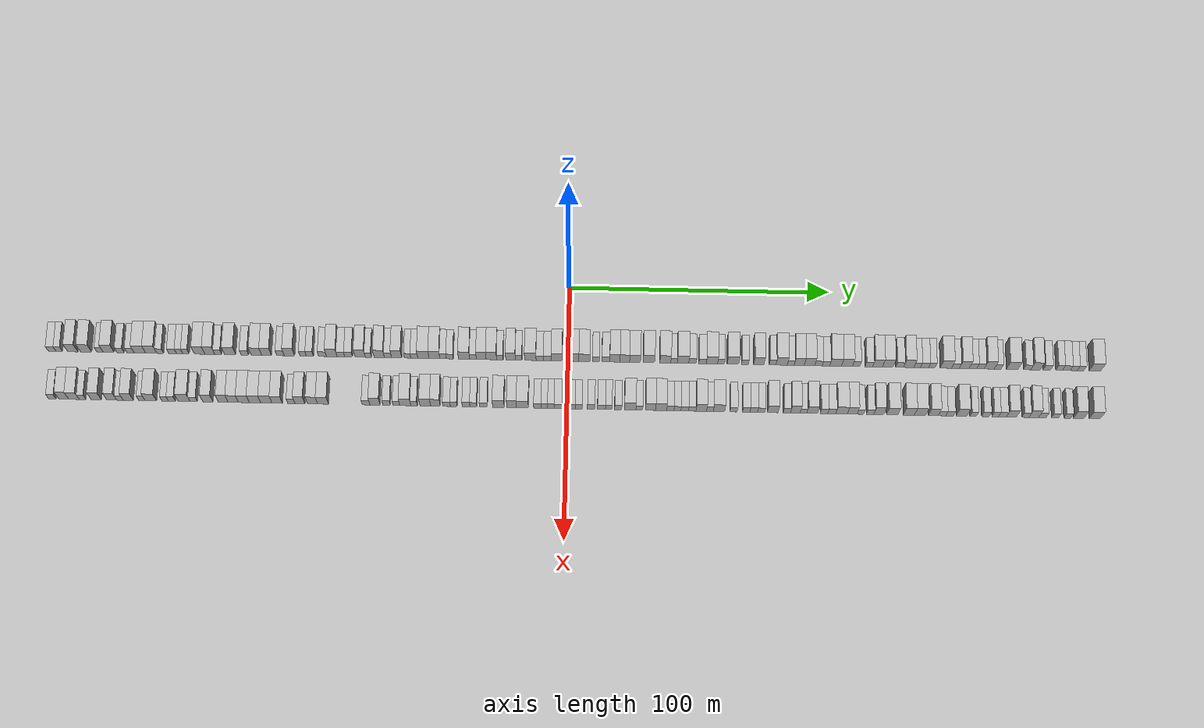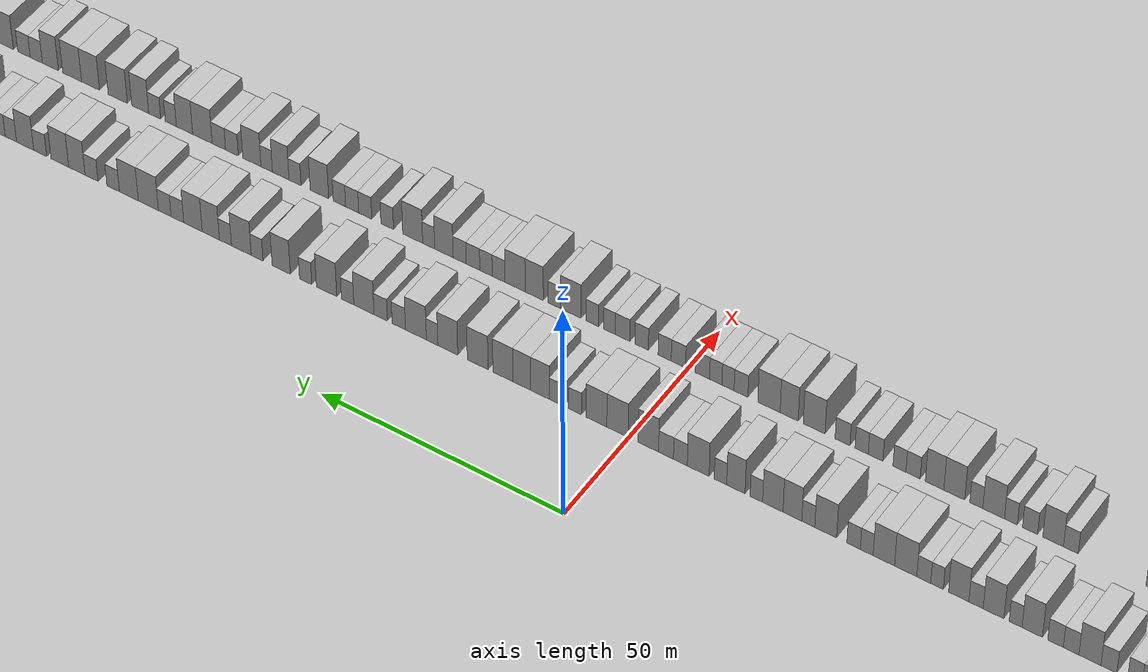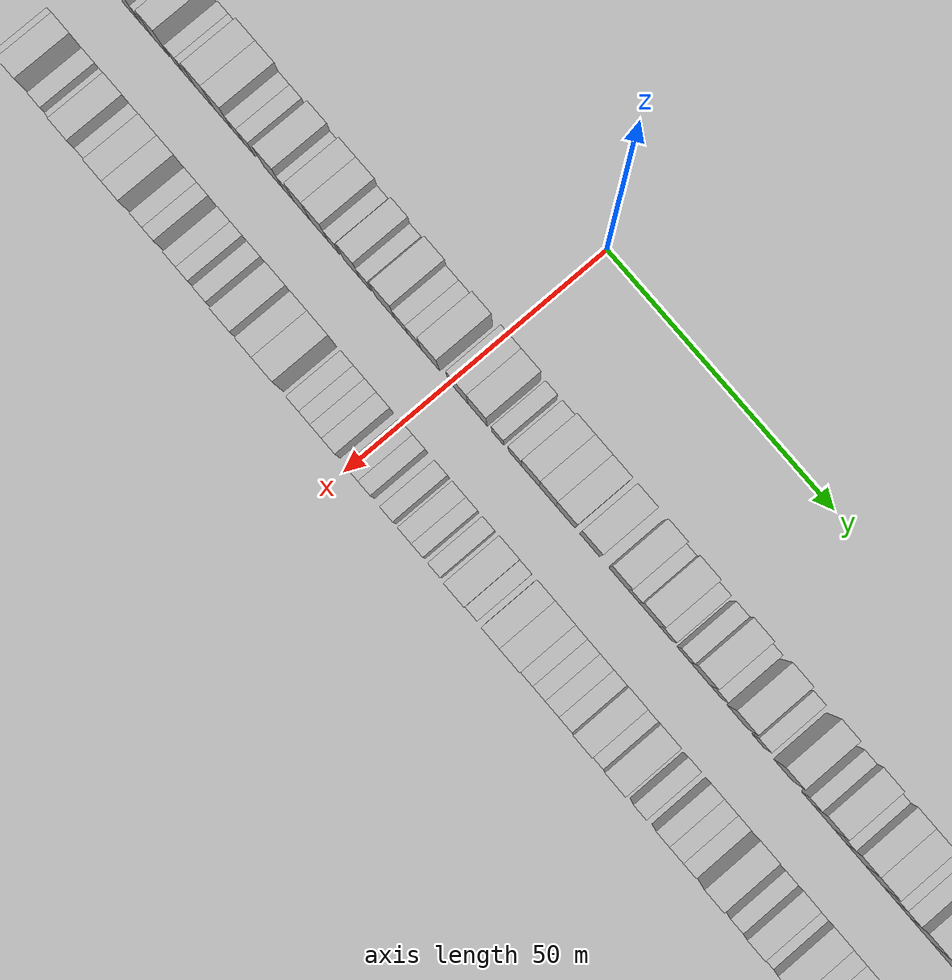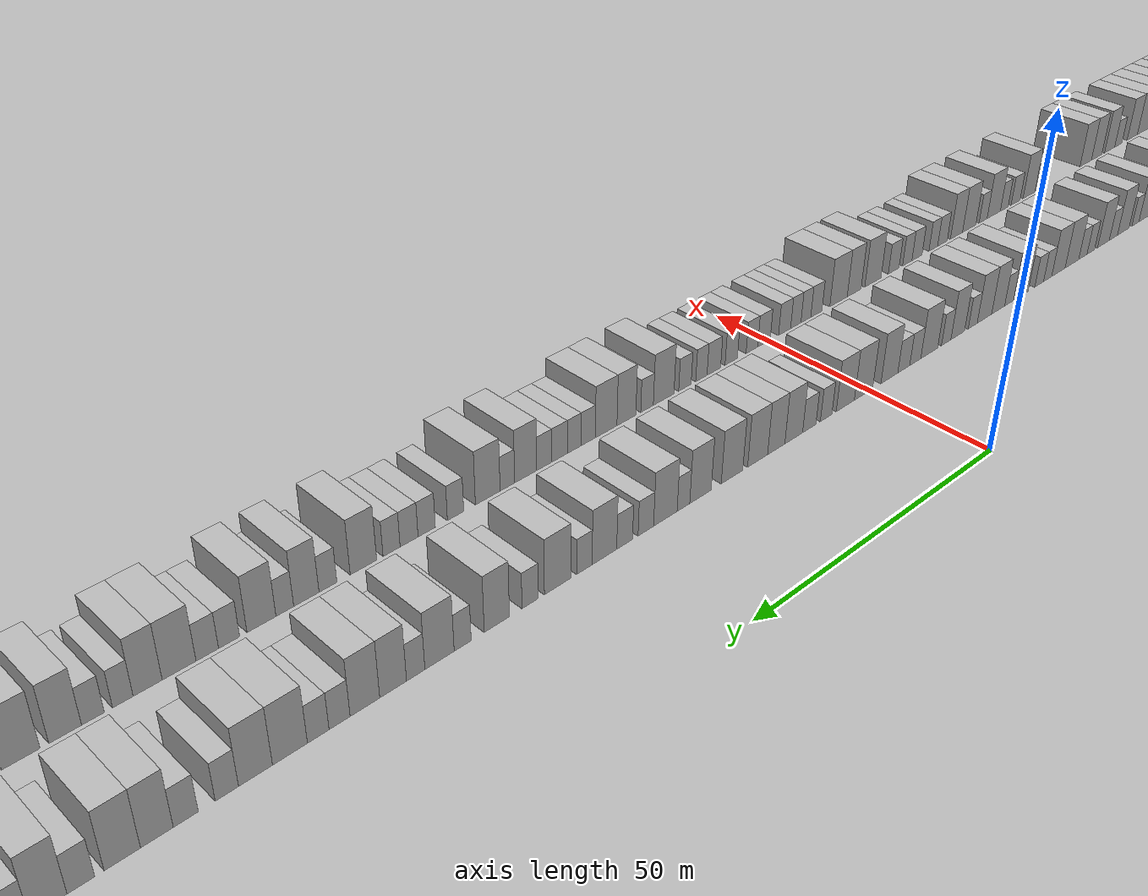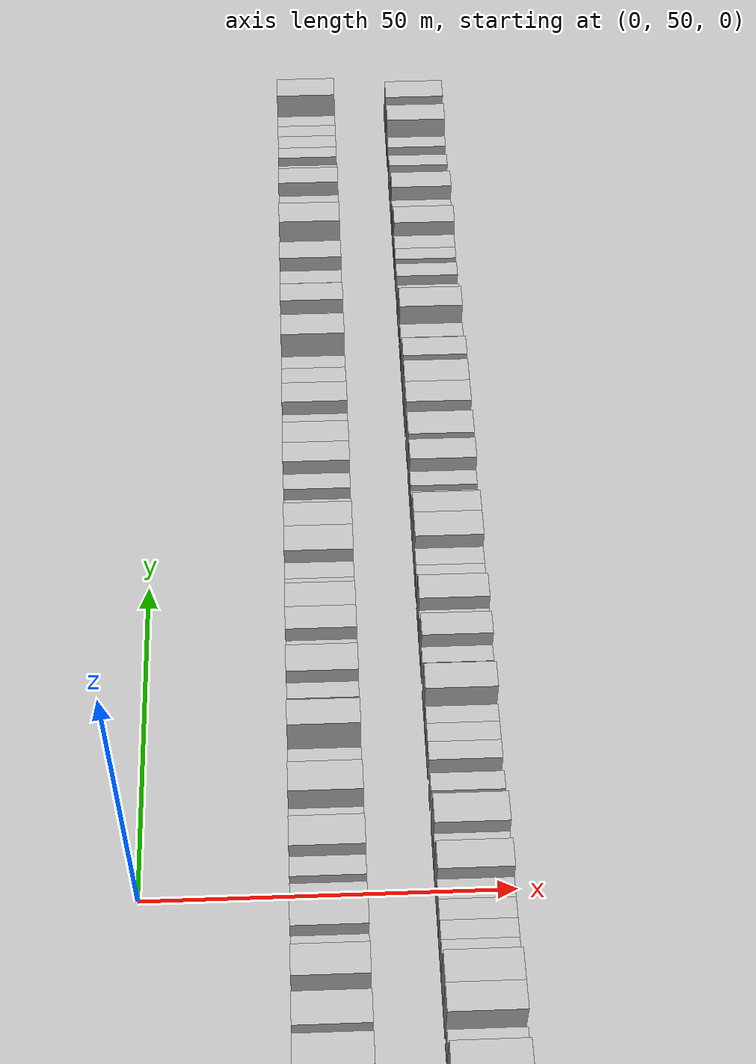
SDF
<?xml version="1.0" encoding="utf-8"?>

<sdf version="1.6">

   <world name="default">

      <gui fullscreen="0">

         <camera name="user_camera">

            <pose>-15 0 4.57585 0 0 0</pose>

            <view_controller>orbit</view_controller>

         </camera>

      </gui>

      <scene>

         <sky>

           <clouds>

             <speed>12</speed>

           </clouds>

         </sky>

         <ambient>0.4 0.4 0.4 1</ambient>

         <background>0.7 0.7 0.7 1</background>

         <shadows>1</shadows>

      </scene>

      <gravity>0 0 -9.8066</gravity>

      <magnetic_field>6e-06 2.3e-05 -4.2e-05</magnetic_field>

      <physics default="0" name="default_physics" type="ode">

         <ode>

            <solver>

               <type>quick</type>

               <iters>10</iters>

               <sor>1.0</sor>

               <use_dynamic_moi_rescaling>0</use_dynamic_moi_rescaling>

            </solver>

            <constraints>

               <cfm>0</cfm>

               <erp>0.2</erp>

               <contact_max_correcting_vel>100</contact_max_correcting_vel>

               <contact_surface_layer>0.001</contact_surface_layer>

            </constraints>

         </ode>

         <max_step_size>0.004</max_step_size>

         <real_time_factor>1</real_time_factor>

         <real_time_update_rate>250</real_time_update_rate>

      </physics>

      <light name="sun" type="directional">

         <cast_shadows>1</cast_shadows>

         <pose>0 0 10 0 0 0</pose>

         <diffuse>0.8 0.8 0.8 1</diffuse>

         <specular>0.2 0.2 0.2 1</specular>

         <attenuation>

            <range>1000</range>

            <constant>0.9</constant>

            <linear>0.01</linear>

            <quadratic>0.001</quadratic>

         </attenuation>

         <direction>-0.5 0.1 -0.9</direction>

      </light>

      <include>

         <name>ground_plane_1</name>

         <uri>model://HANNAS_ground_plane</uri>

         <pose>0 0 0  0 0 0</pose>

      </include>

      <include>

         <name>ground_plane_2</name>

         <uri>model://HANNAS_ground_plane</uri>

         <pose>100 0 0  0 0 0</pose>

      </include>

      <model name="building_1">

         <static>1</static>

         <pose frame="">25.0000 -196.5216 0 0.000000 0.000000 0.000000</pose>

         <link name="link">

            <pose frame="">0 0 3.00 0 0 0</pose>

            <collision name="collision">

               <geometry>

                  <box>

                     <size>10.0000 2.9568 6.0000</size>

                  </box>

               </geometry>

               <max_contacts>10</max_contacts>

               <surface>

                  <contact>

                     <ode/>

                  </contact>

                  <bounce/>

                  <friction>

                     <torsional>

                        <ode/>

                     </torsional>

                     <ode/>

                  </friction>

               </surface>

            </collision>

            <visual name="visual">

               <cast_shadows>0</cast_shadows>

               <geometry>

                  <box>

                     <size>10.0000 2.9568 6.0000</size>

                  </box>

               </geometry>

               <material>

                  <script>

                     <uri>model://HANNAS_wall/materials/scripts</uri>

                     <uri>model://HANNAS_wall/materials/textures</uri>

                     <name>vrc/HANNAS_wall</name>

                  </script>

               </material>

            </visual>

            <self_collide>0</self_collide>

            <enable_wind>0</enable_wind>

            <kinematic>0</kinematic>

         </link>

      </model>

      <model name="building_2">

         <static>1</static>

         <pose frame="">25.0000 -193.8237 0 0.000000 0.000000 0.000000</pose>

         <link name="link">

            <pose frame="">0 0 3.00 0 0 0</pose>

            <collision name="collision">

               <geometry>

                  <box>

                     <size>10.0000 2.4389 6.0000</size>

                  </box>

               </geometry>

               <max_contacts>10</max_contacts>

               <surface>

                  <contact>

                     <ode/>

                  </contact>

                  <bounce/>

                  <friction>

                     <torsional>

                        <ode/>

                     </torsional>

                     <ode/>

                  </friction>

               </surface>

            </collision>

            <visual name="visual">

               <cast_shadows>0</cast_shadows>

               <geometry>

                  <box>

                     <size>10.0000 2.4389 6.0000</size>

                  </box>

               </geometry>

               <material>

                  <script>

                     <uri>model://HANNAS_wall/materials/scripts</uri>

                     <uri>model://HANNAS_wall/materials/textures</uri>

                     <name>vrc/HANNAS_wall</name>

                  </script>

               </material>

            </visual>

            <self_collide>0</self_collide>

            <enable_wind>0</enable_wind>

            <kinematic>0</kinematic>

         </link>

      </model>

      <model name="building_3">

         <static>1</static>

         <pose frame="">25.0000 -188.6595 0 0.000000 0.000000 0.000000</pose>

         <link name="link">

            <pose frame="">0 0 4.50 0 0 0</pose>

            <collision name="collision">

               <geometry>

                  <box>

                     <size>10.0000 3.8895 9.0000</size>

                  </box>

               </geometry>

               <max_contacts>10</max_contacts>

               <surface>

                  <contact>

                     <ode/>

                  </contact>

                  <bounce/>

                  <friction>

                     <torsional>

                        <ode/>

                     </torsional>

                     <ode/>

                  </friction>

               </surface>

            </collision>

            <visual name="visual">

               <cast_shadows>0</cast_shadows>

               <geometry>

                  <box>

                     <size>10.0000 3.8895 9.0000</size>

                  </box>

               </geometry>

               <material>

                  <script>

                     <uri>model://HANNAS_wall/materials/scripts</uri>

                     <uri>model://HANNAS_wall/materials/textures</uri>

                     <name>vrc/HANNAS_wall</name>

                  </script>

               </material>

            </visual>

            <self_collide>0</self_collide>

            <enable_wind>0</enable_wind>

            <kinematic>0</kinematic>

         </link>

      </model>

      <model name="building_4">

         <static>1</static>

         <pose frame="">25.0000 -183.5897 0 0.000000 0.000000 0.000000</pose>

         <link name="link">

            <pose frame="">0 0 4.50 0 0 0</pose>

            <collision name="collision">

               <geometry>

                  <box>

                     <size>10.0000 4.2502 9.0000</size>

                  </box>

               </geometry>

               <max_contacts>10</max_contacts>

               <surface>

                  <contact>

                     <ode/>

                  </contact>

                  <bounce/>

                  <friction>

                     <torsional>

                        <ode/>

                     </torsional>

                     <ode/>

                  </friction>

               </surface>

            </collision>

            <visual name="visual">

               <cast_shadows>0</cast_shadows>

               <geometry>

                  <box>

                     <size>10.0000 4.2502 9.0000</size>

                  </box>

               </geometry>

               <material>

                  <script>

                     <uri>model://HANNAS_wall/materials/scripts</uri>

                     <uri>model://HANNAS_wall/materials/textures</uri>

                     <name>vrc/HANNAS_wall</name>

                  </script>

               </material>

            </visual>

            <self_collide>0</self_collide>

            <enable_wind>0</enable_wind>

            <kinematic>0</kinematic>

         </link>

      </model>

      <model name="building_5">

         <static>1</static>

         <pose frame="">25.0000 -178.2451 0 0.000000 0.000000 0.000000</pose>

         <link name="link">

            <pose frame="">0 0 3.00 0 0 0</pose>

            <collision name="collision">

               <geometry>

                  <box>

                     <size>10.0000 2.4389 6.0000</size>

                  </box>

               </geometry>

               <max_contacts>10</max_contacts>

               <surface>

                  <contact>

                     <ode/>

                  </contact>

                  <bounce/>

                  <friction>

                     <torsional>

                        <ode/>

                     </torsional>

                     <ode/>

                  </friction>

               </surface>

            </collision>

            <visual name="visual">

               <cast_shadows>0</cast_shadows>

               <geometry>

                  <box>

                     <size>10.0000 2.4389 6.0000</size>

                  </box>

               </geometry>

               <material>

                  <script>

                     <uri>model://HANNAS_wall/materials/scripts</uri>

                     <uri>model://HANNAS_wall/materials/textures</uri>

                     <name>vrc/HANNAS_wall</name>

                  </script>

               </material>

            </visual>

            <self_collide>0</self_collide>

            <enable_wind>0</enable_wind>

            <kinematic>0</kinematic>

         </link>

      </model>

      <model name="building_6">

         <static>1</static>

         <pose frame="">25.0000 -174.9173 0 0.000000 0.000000 0.000000</pose>

         <link name="link">

            <pose frame="">0 0 4.50 0 0 0</pose>

            <collision name="collision">

               <geometry>

                  <box>

                     <size>10.0000 4.2168 9.0000</size>

                  </box>

               </geometry>

               <max_contacts>10</max_contacts>

               <surface>

                  <contact>

                     <ode/>

                  </contact>

                  <bounce/>

                  <friction>

                     <torsional>

                        <ode/>

                     </torsional>

                     <ode/>

                  </friction>

               </surface>

            </collision>

            <visual name="visual">

               <cast_shadows>0</cast_shadows>

               <geometry>

                  <box>

                     <size>10.0000 4.2168 9.0000</size>

                  </box>

               </geometry>

               <material>

                  <script>

                     <uri>model://HANNAS_wall/materials/scripts</uri>

                     <uri>model://HANNAS_wall/materials/textures</uri>

                     <name>vrc/HANNAS_wall</name>

                  </script>

               </material>

            </visual>

            <self_collide>0</self_collide>

            <enable_wind>0</enable_wind>

            <kinematic>0</kinematic>

         </link>

      </model>

      <model name="building_7">

         <static>1</static>

         <pose frame="">25.0000 -170.4212 0 0.000000 0.000000 0.000000</pose>

         <link name="link">

            <pose frame="">0 0 3.00 0 0 0</pose>

            <collision name="collision">

               <geometry>

                  <box>

                     <size>10.0000 2.7752 6.0000</size>

                  </box>

               </geometry>

               <max_contacts>10</max_contacts>

               <surface>

                  <contact>

                     <ode/>

                  </contact>

                  <bounce/>

                  <friction>

                     <torsional>

                        <ode/>

                     </torsional>

                     <ode/>

                  </friction>

               </surface>

            </collision>

            <visual name="visual">

               <cast_shadows>0</cast_shadows>

               <geometry>

                  <box>

                     <size>10.0000 2.7752 6.0000</size>

                  </box>

               </geometry>

               <material>

                  <script>

                     <uri>model://HANNAS_wall/materials/scripts</uri>

                     <uri>model://HANNAS_wall/materials/textures</uri>

                     <name>vrc/HANNAS_wall</name>

                  </script>

               </material>

            </visual>

            <self_collide>0</self_collide>

            <enable_wind>0</enable_wind>

            <kinematic>0</kinematic>

         </link>

      </model>

      <model name="building_8">

         <static>1</static>

         <pose frame="">25.0000 -166.6323 0 0.000000 0.000000 0.000000</pose>

         <link name="link">

            <pose frame="">0 0 3.00 0 0 0</pose>

            <collision name="collision">

               <geometry>

                  <box>

                     <size>10.0000 2.8027 6.0000</size>

                  </box>

               </geometry>

               <max_contacts>10</max_contacts>

               <surface>

                  <contact>

                     <ode/>

                  </contact>

                  <bounce/>

                  <friction>

                     <torsional>

                        <ode/>

                     </torsional>

                     <ode/>

                  </friction>

               </surface>

            </collision>

            <visual name="visual">

               <cast_shadows>0</cast_shadows>

               <geometry>

                  <box>

                     <size>10.0000 2.8027 6.0000</size>

                  </box>

               </geometry>

               <material>

                  <script>

                     <uri>model://HANNAS_wall/materials/scripts</uri>

                     <uri>model://HANNAS_wall/materials/textures</uri>

                     <name>vrc/HANNAS_wall</name>

                  </script>

               </material>

            </visual>

            <self_collide>0</self_collide>

            <enable_wind>0</enable_wind>

            <kinematic>0</kinematic>

         </link>

      </model>

      <model name="building_9">

         <static>1</static>

         <pose frame="">25.0000 -163.0565 0 0.000000 0.000000 0.000000</pose>

         <link name="link">

            <pose frame="">0 0 4.50 0 0 0</pose>

            <collision name="collision">

               <geometry>

                  <box>

                     <size>10.0000 4.3489 9.0000</size>

                  </box>

               </geometry>

               <max_contacts>10</max_contacts>

               <surface>

                  <contact>

                     <ode/>

                  </contact>

                  <bounce/>

                  <friction>

                     <torsional>

                        <ode/>

                     </torsional>

                     <ode/>

                  </friction>

               </surface>

            </collision>

            <visual name="visual">

               <cast_shadows>0</cast_shadows>

               <geometry>

                  <box>

                     <size>10.0000 4.3489 9.0000</size>

                  </box>

               </geometry>

               <material>

                  <script>

                     <uri>model://HANNAS_wall/materials/scripts</uri>

                     <uri>model://HANNAS_wall/materials/textures</uri>

                     <name>vrc/HANNAS_wall</name>

                  </script>

               </material>

            </visual>

            <self_collide>0</self_collide>

            <enable_wind>0</enable_wind>

            <kinematic>0</kinematic>

         </link>

      </model>

      <model name="building_10">

         <static>1</static>

         <pose frame="">25.0000 -158.7368 0 0.000000 0.000000 0.000000</pose>

         <link name="link">

            <pose frame="">0 0 4.50 0 0 0</pose>

            <collision name="collision">

               <geometry>

                  <box>

                     <size>10.0000 4.2905 9.0000</size>

                  </box>

               </geometry>

               <max_contacts>10</max_contacts>

               <surface>

                  <contact>

                     <ode/>

                  </contact>

                  <bounce/>

                  <friction>

                     <torsional>

                        <ode/>

                     </torsional>

                     <ode/>

                  </friction>

               </surface>

            </collision>

            <visual name="visual">

               <cast_shadows>0</cast_shadows>

               <geometry>

                  <box>

                     <size>10.0000 4.2905 9.0000</size>

                  </box>

               </geometry>

               <material>

                  <script>

                     <uri>model://HANNAS_wall/materials/scripts</uri>

                     <uri>model://HANNAS_wall/materials/textures</uri>

                     <name>vrc/HANNAS_wall</name>

                  </script>

               </material>

            </visual>

            <self_collide>0</self_collide>

            <enable_wind>0</enable_wind>

            <kinematic>0</kinematic>

         </link>

      </model>

      <model name="building_11">

         <static>1</static>

         <pose frame="">25.0000 -155.3103 0 0.000000 0.000000 0.000000</pose>

         <link name="link">

            <pose frame="">0 0 3.00 0 0 0</pose>

            <collision name="collision">

               <geometry>

                  <box>

                     <size>10.0000 2.5625 6.0000</size>

                  </box>

               </geometry>

               <max_contacts>10</max_contacts>

               <surface>

                  <contact>

                     <ode/>

                  </contact>

                  <bounce/>

                  <friction>

                     <torsional>

                        <ode/>

                     </torsional>

                     <ode/>

                  </friction>

               </surface>

            </collision>

            <visual name="visual">

               <cast_shadows>0</cast_shadows>

               <geometry>

                  <box>

                     <size>10.0000 2.5625 6.0000</size>

                  </box>

               </geometry>

               <material>

                  <script>

                     <uri>model://HANNAS_wall/materials/scripts</uri>

                     <uri>model://HANNAS_wall/materials/textures</uri>

                     <name>vrc/HANNAS_wall</name>

                  </script>

               </material>

            </visual>

            <self_collide>0</self_collide>

            <enable_wind>0</enable_wind>

            <kinematic>0</kinematic>

         </link>

      </model>

      <model name="building_12">

         <static>1</static>

         <pose frame="">25.0000 -150.5763 0 0.000000 0.000000 0.000000</pose>

         <link name="link">

            <pose frame="">0 0 3.00 0 0 0</pose>

            <collision name="collision">

               <geometry>

                  <box>

                     <size>10.0000 2.9056 6.0000</size>

                  </box>

               </geometry>

               <max_contacts>10</max_contacts>

               <surface>

                  <contact>

                     <ode/>

                  </contact>

                  <bounce/>

                  <friction>

                     <torsional>

                        <ode/>

                     </torsional>

                     <ode/>

                  </friction>

               </surface>

            </collision>

            <visual name="visual">

               <cast_shadows>0</cast_shadows>

               <geometry>

                  <box>

                     <size>10.0000 2.9056 6.0000</size>

                  </box>

               </geometry>

               <material>

                  <script>

                     <uri>model://HANNAS_wall/materials/scripts</uri>

                     <uri>model://HANNAS_wall/materials/textures</uri>

                     <name>vrc/HANNAS_wall</name>

                  </script>

               </material>

            </visual>

            <self_collide>0</self_collide>

            <enable_wind>0</enable_wind>

            <kinematic>0</kinematic>

         </link>

      </model>

      <model name="building_13">

         <static>1</static>

         <pose frame="">25.0000 -147.9111 0 0.000000 0.000000 0.000000</pose>

         <link name="link">

            <pose frame="">0 0 3.00 0 0 0</pose>

            <collision name="collision">

               <geometry>

                  <box>

                     <size>10.0000 2.4247 6.0000</size>

                  </box>

               </geometry>

               <max_contacts>10</max_contacts>

               <surface>

                  <contact>

                     <ode/>

                  </contact>

                  <bounce/>

                  <friction>

                     <torsional>

                        <ode/>

                     </torsional>

                     <ode/>

                  </friction>

               </surface>

            </collision>

            <visual name="visual">

               <cast_shadows>0</cast_shadows>

               <geometry>

                  <box>

                     <size>10.0000 2.4247 6.0000</size>

                  </box>

               </geometry>

               <material>

                  <script>

                     <uri>model://HANNAS_wall/materials/scripts</uri>

                     <uri>model://HANNAS_wall/materials/textures</uri>

                     <name>vrc/HANNAS_wall</name>

                  </script>

               </material>

            </visual>

            <self_collide>0</self_collide>

            <enable_wind>0</enable_wind>

            <kinematic>0</kinematic>

         </link>

      </model>

      <model name="building_14">

         <static>1</static>

         <pose frame="">25.0000 -145.4668 0 0.000000 0.000000 0.000000</pose>

         <link name="link">

            <pose frame="">0 0 3.00 0 0 0</pose>

            <collision name="collision">

               <geometry>

                  <box>

                     <size>10.0000 2.4639 6.0000</size>

                  </box>

               </geometry>

               <max_contacts>10</max_contacts>

               <surface>

                  <contact>

                     <ode/>

                  </contact>

                  <bounce/>

                  <friction>

                     <torsional>

                        <ode/>

                     </torsional>

                     <ode/>

                  </friction>

               </surface>

            </collision>

            <visual name="visual">

               <cast_shadows>0</cast_shadows>

               <geometry>

                  <box>

                     <size>10.0000 2.4639 6.0000</size>

                  </box>

               </geometry>

               <material>

                  <script>

                     <uri>model://HANNAS_wall/materials/scripts</uri>

                     <uri>model://HANNAS_wall/materials/textures</uri>

                     <name>vrc/HANNAS_wall</name>

                  </script>

               </material>

            </visual>

            <self_collide>0</self_collide>

            <enable_wind>0</enable_wind>

            <kinematic>0</kinematic>

         </link>

      </model>

      <model name="building_15">

         <static>1</static>

         <pose frame="">25.0000 -140.2559 0 0.000000 0.000000 0.000000</pose>

         <link name="link">

            <pose frame="">0 0 4.50 0 0 0</pose>

            <collision name="collision">

               <geometry>

                  <box>

                     <size>10.0000 3.9579 9.0000</size>

                  </box>

               </geometry>

               <max_contacts>10</max_contacts>

               <surface>

                  <contact>

                     <ode/>

                  </contact>

                  <bounce/>

                  <friction>

                     <torsional>

                        <ode/>

                     </torsional>

                     <ode/>

                  </friction>

               </surface>

            </collision>

            <visual name="visual">

               <cast_shadows>0</cast_shadows>

               <geometry>

                  <box>

                     <size>10.0000 3.9579 9.0000</size>

                  </box>

               </geometry>

               <material>

                  <script>

                     <uri>model://HANNAS_wall/materials/scripts</uri>

                     <uri>model://HANNAS_wall/materials/textures</uri>

                     <name>vrc/HANNAS_wall</name>

                  </script>

               </material>

            </visual>

            <self_collide>0</self_collide>

            <enable_wind>0</enable_wind>

            <kinematic>0</kinematic>

         </link>

      </model>

      <model name="building_16">

         <static>1</static>

         <pose frame="">25.0000 -136.3634 0 0.000000 0.000000 0.000000</pose>

         <link name="link">

            <pose frame="">0 0 4.50 0 0 0</pose>

            <collision name="collision">

               <geometry>

                  <box>

                     <size>10.0000 3.8270 9.0000</size>

                  </box>

               </geometry>

               <max_contacts>10</max_contacts>

               <surface>

                  <contact>

                     <ode/>

                  </contact>

                  <bounce/>

                  <friction>

                     <torsional>

                        <ode/>

                     </torsional>

                     <ode/>

                  </friction>

               </surface>

            </collision>

            <visual name="visual">

               <cast_shadows>0</cast_shadows>

               <geometry>

                  <box>

                     <size>10.0000 3.8270 9.0000</size>

                  </box>

               </geometry>

               <material>

                  <script>

                     <uri>model://HANNAS_wall/materials/scripts</uri>

                     <uri>model://HANNAS_wall/materials/textures</uri>

                     <name>vrc/HANNAS_wall</name>

                  </script>

               </material>

            </visual>

            <self_collide>0</self_collide>

            <enable_wind>0</enable_wind>

            <kinematic>0</kinematic>

         </link>

      </model>

      <model name="building_17">

         <static>1</static>

         <pose frame="">25.0000 -133.1001 0 0.000000 0.000000 0.000000</pose>

         <link name="link">

            <pose frame="">0 0 3.00 0 0 0</pose>

            <collision name="collision">

               <geometry>

                  <box>

                     <size>10.0000 2.6995 6.0000</size>

                  </box>

               </geometry>

               <max_contacts>10</max_contacts>

               <surface>

                  <contact>

                     <ode/>

                  </contact>

                  <bounce/>

                  <friction>

                     <torsional>

                        <ode/>

                     </torsional>

                     <ode/>

                  </friction>

               </surface>

            </collision>

            <visual name="visual">

               <cast_shadows>0</cast_shadows>

               <geometry>

                  <box>

                     <size>10.0000 2.6995 6.0000</size>

                  </box>

               </geometry>

               <material>

                  <script>

                     <uri>model://HANNAS_wall/materials/scripts</uri>

                     <uri>model://HANNAS_wall/materials/textures</uri>

                     <name>vrc/HANNAS_wall</name>

                  </script>

               </material>

            </visual>

            <self_collide>0</self_collide>

            <enable_wind>0</enable_wind>

            <kinematic>0</kinematic>

         </link>

      </model>

      <model name="building_18">

         <static>1</static>

         <pose frame="">25.0000 -128.6211 0 0.000000 0.000000 0.000000</pose>

         <link name="link">

            <pose frame="">0 0 4.50 0 0 0</pose>

            <collision name="collision">

               <geometry>

                  <box>

                     <size>10.0000 4.2584 9.0000</size>

                  </box>

               </geometry>

               <max_contacts>10</max_contacts>

               <surface>

                  <contact>

                     <ode/>

                  </contact>

                  <bounce/>

                  <friction>

                     <torsional>

                        <ode/>

                     </torsional>

                     <ode/>

                  </friction>

               </surface>

            </collision>

            <visual name="visual">

               <cast_shadows>0</cast_shadows>

               <geometry>

                  <box>

                     <size>10.0000 4.2584 9.0000</size>

                  </box>

               </geometry>

               <material>

                  <script>

                     <uri>model://HANNAS_wall/materials/scripts</uri>

                     <uri>model://HANNAS_wall/materials/textures</uri>

                     <name>vrc/HANNAS_wall</name>

                  </script>

               </material>

            </visual>

            <self_collide>0</self_collide>

            <enable_wind>0</enable_wind>

            <kinematic>0</kinematic>

         </link>

      </model>

      <model name="building_19">

         <static>1</static>

         <pose frame="">25.0000 -123.0242 0 0.000000 0.000000 0.000000</pose>

         <link name="link">

            <pose frame="">0 0 3.00 0 0 0</pose>

            <collision name="collision">

               <geometry>

                  <box>

                     <size>10.0000 2.9353 6.0000</size>

                  </box>

               </geometry>

               <max_contacts>10</max_contacts>

               <surface>

                  <contact>

                     <ode/>

                  </contact>

                  <bounce/>

                  <friction>

                     <torsional>

                        <ode/>

                     </torsional>

                     <ode/>

                  </friction>

               </surface>

            </collision>

            <visual name="visual">

               <cast_shadows>0</cast_shadows>

               <geometry>

                  <box>

                     <size>10.0000 2.9353 6.0000</size>

                  </box>

               </geometry>

               <material>

                  <script>

                     <uri>model://HANNAS_wall/materials/scripts</uri>

                     <uri>model://HANNAS_wall/materials/textures</uri>

                     <name>vrc/HANNAS_wall</name>

                  </script>

               </material>

            </visual>

            <self_collide>0</self_collide>

            <enable_wind>0</enable_wind>

            <kinematic>0</kinematic>

         </link>

      </model>

      <model name="building_20">

         <static>1</static>

         <pose frame="">25.0000 -118.5763 0 0.000000 0.000000 0.000000</pose>

         <link name="link">

            <pose frame="">0 0 4.50 0 0 0</pose>

            <collision name="collision">

               <geometry>

                  <box>

                     <size>10.0000 3.9605 9.0000</size>

                  </box>

               </geometry>

               <max_contacts>10</max_contacts>

               <surface>

                  <contact>

                     <ode/>

                  </contact>

                  <bounce/>

                  <friction>

                     <torsional>

                        <ode/>

                     </torsional>

                     <ode/>

                  </friction>

               </surface>

            </collision>

            <visual name="visual">

               <cast_shadows>0</cast_shadows>

               <geometry>

                  <box>

                     <size>10.0000 3.9605 9.0000</size>

                  </box>

               </geometry>

               <material>

                  <script>

                     <uri>model://HANNAS_wall/materials/scripts</uri>

                     <uri>model://HANNAS_wall/materials/textures</uri>

                     <name>vrc/HANNAS_wall</name>

                  </script>

               </material>

            </visual>

            <self_collide>0</self_collide>

            <enable_wind>0</enable_wind>

            <kinematic>0</kinematic>

         </link>

      </model>

      <model name="building_21">

         <static>1</static>

         <pose frame="">25.0000 -114.7280 0 0.000000 0.000000 0.000000</pose>

         <link name="link">

            <pose frame="">0 0 4.50 0 0 0</pose>

            <collision name="collision">

               <geometry>

                  <box>

                     <size>10.0000 3.7361 9.0000</size>

                  </box>

               </geometry>

               <max_contacts>10</max_contacts>

               <surface>

                  <contact>

                     <ode/>

                  </contact>

                  <bounce/>

                  <friction>

                     <torsional>

                        <ode/>

                     </torsional>

                     <ode/>

                  </friction>

               </surface>

            </collision>

            <visual name="visual">

               <cast_shadows>0</cast_shadows>

               <geometry>

                  <box>

                     <size>10.0000 3.7361 9.0000</size>

                  </box>

               </geometry>

               <material>

                  <script>

                     <uri>model://HANNAS_wall/materials/scripts</uri>

                     <uri>model://HANNAS_wall/materials/textures</uri>

                     <name>vrc/HANNAS_wall</name>

                  </script>

               </material>

            </visual>

            <self_collide>0</self_collide>

            <enable_wind>0</enable_wind>

            <kinematic>0</kinematic>

         </link>

      </model>

      <model name="building_22">

         <static>1</static>

         <pose frame="">25.0000 -109.4225 0 0.000000 0.000000 0.000000</pose>

         <link name="link">

            <pose frame="">0 0 3.00 0 0 0</pose>

            <collision name="collision">

               <geometry>

                  <box>

                     <size>10.0000 2.8748 6.0000</size>

                  </box>

               </geometry>

               <max_contacts>10</max_contacts>

               <surface>

                  <contact>

                     <ode/>

                  </contact>

                  <bounce/>

                  <friction>

                     <torsional>

                        <ode/>

                     </torsional>

                     <ode/>

                  </friction>

               </surface>

            </collision>

            <visual name="visual">

               <cast_shadows>0</cast_shadows>

               <geometry>

                  <box>

                     <size>10.0000 2.8748 6.0000</size>

                  </box>

               </geometry>

               <material>

                  <script>

                     <uri>model://HANNAS_wall/materials/scripts</uri>

                     <uri>model://HANNAS_wall/materials/textures</uri>

                     <name>vrc/HANNAS_wall</name>

                  </script>

               </material>

            </visual>

            <self_collide>0</self_collide>

            <enable_wind>0</enable_wind>

            <kinematic>0</kinematic>

         </link>

      </model>

      <model name="building_23">

         <static>1</static>

         <pose frame="">25.0000 -106.0027 0 0.000000 0.000000 0.000000</pose>

         <link name="link">

            <pose frame="">0 0 4.50 0 0 0</pose>

            <collision name="collision">

               <geometry>

                  <box>

                     <size>10.0000 3.9648 9.0000</size>

                  </box>

               </geometry>

               <max_contacts>10</max_contacts>

               <surface>

                  <contact>

                     <ode/>

                  </contact>

                  <bounce/>

                  <friction>

                     <torsional>

                        <ode/>

                     </torsional>

                     <ode/>

                  </friction>

               </surface>

            </collision>

            <visual name="visual">

               <cast_shadows>0</cast_shadows>

               <geometry>

                  <box>

                     <size>10.0000 3.9648 9.0000</size>

                  </box>

               </geometry>

               <material>

                  <script>

                     <uri>model://HANNAS_wall/materials/scripts</uri>

                     <uri>model://HANNAS_wall/materials/textures</uri>

                     <name>vrc/HANNAS_wall</name>

                  </script>

               </material>

            </visual>

            <self_collide>0</self_collide>

            <enable_wind>0</enable_wind>

            <kinematic>0</kinematic>

         </link>

      </model>

      <model name="building_24">

         <static>1</static>

         <pose frame="">25.0000 -100.7795 0 0.000000 0.000000 0.000000</pose>

         <link name="link">

            <pose frame="">0 0 3.00 0 0 0</pose>

            <collision name="collision">

               <geometry>

                  <box>

                     <size>10.0000 2.4816 6.0000</size>

                  </box>

               </geometry>

               <max_contacts>10</max_contacts>

               <surface>

                  <contact>

                     <ode/>

                  </contact>

                  <bounce/>

                  <friction>

                     <torsional>

                        <ode/>

                     </torsional>

                     <ode/>

                  </friction>

               </surface>

            </collision>

            <visual name="visual">

               <cast_shadows>0</cast_shadows>

               <geometry>

                  <box>

                     <size>10.0000 2.4816 6.0000</size>

                  </box>

               </geometry>

               <material>

                  <script>

                     <uri>model://HANNAS_wall/materials/scripts</uri>

                     <uri>model://HANNAS_wall/materials/textures</uri>

                     <name>vrc/HANNAS_wall</name>

                  </script>

               </material>

            </visual>

            <self_collide>0</self_collide>

            <enable_wind>0</enable_wind>

            <kinematic>0</kinematic>

         </link>

      </model>

      <model name="building_25">

         <static>1</static>

         <pose frame="">25.0000 -98.1952 0 0.000000 0.000000 0.000000</pose>

         <link name="link">

            <pose frame="">0 0 3.00 0 0 0</pose>

            <collision name="collision">

               <geometry>

                  <box>

                     <size>10.0000 2.6870 6.0000</size>

                  </box>

               </geometry>

               <max_contacts>10</max_contacts>

               <surface>

                  <contact>

                     <ode/>

                  </contact>

                  <bounce/>

                  <friction>

                     <torsional>

                        <ode/>

                     </torsional>

                     <ode/>

                  </friction>

               </surface>

            </collision>

            <visual name="visual">

               <cast_shadows>0</cast_shadows>

               <geometry>

                  <box>

                     <size>10.0000 2.6870 6.0000</size>

                  </box>

               </geometry>

               <material>

                  <script>

                     <uri>model://HANNAS_wall/materials/scripts</uri>

                     <uri>model://HANNAS_wall/materials/textures</uri>

                     <name>vrc/HANNAS_wall</name>

                  </script>

               </material>

            </visual>

            <self_collide>0</self_collide>

            <enable_wind>0</enable_wind>

            <kinematic>0</kinematic>

         </link>

      </model>

      <model name="building_26">

         <static>1</static>

         <pose frame="">25.0000 -93.3757 0 0.000000 0.000000 0.000000</pose>

         <link name="link">

            <pose frame="">0 0 3.00 0 0 0</pose>

            <collision name="collision">

               <geometry>

                  <box>

                     <size>10.0000 2.9520 6.0000</size>

                  </box>

               </geometry>

               <max_contacts>10</max_contacts>

               <surface>

                  <contact>

                     <ode/>

                  </contact>

                  <bounce/>

                  <friction>

                     <torsional>

                        <ode/>

                     </torsional>

                     <ode/>

                  </friction>

               </surface>

            </collision>

            <visual name="visual">

               <cast_shadows>0</cast_shadows>

               <geometry>

                  <box>

                     <size>10.0000 2.9520 6.0000</size>

                  </box>

               </geometry>

               <material>

                  <script>

                     <uri>model://HANNAS_wall/materials/scripts</uri>

                     <uri>model://HANNAS_wall/materials/textures</uri>

                     <name>vrc/HANNAS_wall</name>

                  </script>

               </material>

            </visual>

            <self_collide>0</self_collide>

            <enable_wind>0</enable_wind>

            <kinematic>0</kinematic>

         </link>

      </model>

      <model name="building_27">

         <static>1</static>

         <pose frame="">25.0000 -89.8554 0 0.000000 0.000000 0.000000</pose>

         <link name="link">

            <pose frame="">0 0 4.50 0 0 0</pose>

            <collision name="collision">

               <geometry>

                  <box>

                     <size>10.0000 4.0886 9.0000</size>

                  </box>

               </geometry>

               <max_contacts>10</max_contacts>

               <surface>

                  <contact>

                     <ode/>

                  </contact>

                  <bounce/>

                  <friction>

                     <torsional>

                        <ode/>

                     </torsional>

                     <ode/>

                  </friction>

               </surface>

            </collision>

            <visual name="visual">

               <cast_shadows>0</cast_shadows>

               <geometry>

                  <box>

                     <size>10.0000 4.0886 9.0000</size>

                  </box>

               </geometry>

               <material>

                  <script>

                     <uri>model://HANNAS_wall/materials/scripts</uri>

                     <uri>model://HANNAS_wall/materials/textures</uri>

                     <name>vrc/HANNAS_wall</name>

                  </script>

               </material>

            </visual>

            <self_collide>0</self_collide>

            <enable_wind>0</enable_wind>

            <kinematic>0</kinematic>

         </link>

      </model>

      <model name="building_28">

         <static>1</static>

         <pose frame="">25.0000 -86.3526 0 0.000000 0.000000 0.000000</pose>

         <link name="link">

            <pose frame="">0 0 3.00 0 0 0</pose>

            <collision name="collision">

               <geometry>

                  <box>

                     <size>10.0000 2.9172 6.0000</size>

                  </box>

               </geometry>

               <max_contacts>10</max_contacts>

               <surface>

                  <contact>

                     <ode/>

                  </contact>

                  <bounce/>

                  <friction>

                     <torsional>

                        <ode/>

                     </torsional>

                     <ode/>

                  </friction>

               </surface>

            </collision>

            <visual name="visual">

               <cast_shadows>0</cast_shadows>

               <geometry>

                  <box>

                     <size>10.0000 2.9172 6.0000</size>

                  </box>

               </geometry>

               <material>

                  <script>

                     <uri>model://HANNAS_wall/materials/scripts</uri>

                     <uri>model://HANNAS_wall/materials/textures</uri>

                     <name>vrc/HANNAS_wall</name>

                  </script>

               </material>

            </visual>

            <self_collide>0</self_collide>

            <enable_wind>0</enable_wind>

            <kinematic>0</kinematic>

         </link>

      </model>

      <model name="building_29">

         <static>1</static>

         <pose frame="">25.0000 -83.4376 0 0.000000 0.000000 0.000000</pose>

         <link name="link">

            <pose frame="">0 0 3.00 0 0 0</pose>

            <collision name="collision">

               <geometry>

                  <box>

                     <size>10.0000 2.9129 6.0000</size>

                  </box>

               </geometry>

               <max_contacts>10</max_contacts>

               <surface>

                  <contact>

                     <ode/>

                  </contact>

                  <bounce/>

                  <friction>

                     <torsional>

                        <ode/>

                     </torsional>

                     <ode/>

                  </friction>

               </surface>

            </collision>

            <visual name="visual">

               <cast_shadows>0</cast_shadows>

               <geometry>

                  <box>

                     <size>10.0000 2.9129 6.0000</size>

                  </box>

               </geometry>

               <material>

                  <script>

                     <uri>model://HANNAS_wall/materials/scripts</uri>

                     <uri>model://HANNAS_wall/materials/textures</uri>

                     <name>vrc/HANNAS_wall</name>

                  </script>

               </material>

            </visual>

            <self_collide>0</self_collide>

            <enable_wind>0</enable_wind>

            <kinematic>0</kinematic>

         </link>

      </model>

      <model name="building_30">

         <static>1</static>

         <pose frame="">25.0000 -79.0582 0 0.000000 0.000000 0.000000</pose>

         <link name="link">

            <pose frame="">0 0 4.50 0 0 0</pose>

            <collision name="collision">

               <geometry>

                  <box>

                     <size>10.0000 3.8459 9.0000</size>

                  </box>

               </geometry>

               <max_contacts>10</max_contacts>

               <surface>

                  <contact>

                     <ode/>

                  </contact>

                  <bounce/>

                  <friction>

                     <torsional>

                        <ode/>

                     </torsional>

                     <ode/>

                  </friction>

               </surface>

            </collision>

            <visual name="visual">

               <cast_shadows>0</cast_shadows>

               <geometry>

                  <box>

                     <size>10.0000 3.8459 9.0000</size>

                  </box>

               </geometry>

               <material>

                  <script>

                     <uri>model://HANNAS_wall/materials/scripts</uri>

                     <uri>model://HANNAS_wall/materials/textures</uri>

                     <name>vrc/HANNAS_wall</name>

                  </script>

               </material>

            </visual>

            <self_collide>0</self_collide>

            <enable_wind>0</enable_wind>

            <kinematic>0</kinematic>

         </link>

      </model>

      <model name="building_31">

         <static>1</static>

         <pose frame="">25.0000 -75.9244 0 0.000000 0.000000 0.000000</pose>

         <link name="link">

            <pose frame="">0 0 3.00 0 0 0</pose>

            <collision name="collision">

               <geometry>

                  <box>

                     <size>10.0000 2.4217 6.0000</size>

                  </box>

               </geometry>

               <max_contacts>10</max_contacts>

               <surface>

                  <contact>

                     <ode/>

                  </contact>

                  <bounce/>

                  <friction>

                     <torsional>

                        <ode/>

                     </torsional>

                     <ode/>

                  </friction>

               </surface>

            </collision>

            <visual name="visual">

               <cast_shadows>0</cast_shadows>

               <geometry>

                  <box>

                     <size>10.0000 2.4217 6.0000</size>

                  </box>

               </geometry>

               <material>

                  <script>

                     <uri>model://HANNAS_wall/materials/scripts</uri>

                     <uri>model://HANNAS_wall/materials/textures</uri>

                     <name>vrc/HANNAS_wall</name>

                  </script>

               </material>

            </visual>

            <self_collide>0</self_collide>

            <enable_wind>0</enable_wind>

            <kinematic>0</kinematic>

         </link>

      </model>

      <model name="building_32">

         <static>1</static>

         <pose frame="">25.0000 -71.7508 0 0.000000 0.000000 0.000000</pose>

         <link name="link">

            <pose frame="">0 0 4.50 0 0 0</pose>

            <collision name="collision">

               <geometry>

                  <box>

                     <size>10.0000 3.9255 9.0000</size>

                  </box>

               </geometry>

               <max_contacts>10</max_contacts>

               <surface>

                  <contact>

                     <ode/>

                  </contact>

                  <bounce/>

                  <friction>

                     <torsional>

                        <ode/>

                     </torsional>

                     <ode/>

                  </friction>

               </surface>

            </collision>

            <visual name="visual">

               <cast_shadows>0</cast_shadows>

               <geometry>

                  <box>

                     <size>10.0000 3.9255 9.0000</size>

                  </box>

               </geometry>

               <material>

                  <script>

                     <uri>model://HANNAS_wall/materials/scripts</uri>

                     <uri>model://HANNAS_wall/materials/textures</uri>

                     <name>vrc/HANNAS_wall</name>

                  </script>

               </material>

            </visual>

            <self_collide>0</self_collide>

            <enable_wind>0</enable_wind>

            <kinematic>0</kinematic>

         </link>

      </model>

      <model name="building_33">

         <static>1</static>

         <pose frame="">25.0000 -68.4261 0 0.000000 0.000000 0.000000</pose>

         <link name="link">

            <pose frame="">0 0 3.00 0 0 0</pose>

            <collision name="collision">

               <geometry>

                  <box>

                     <size>10.0000 2.7239 6.0000</size>

                  </box>

               </geometry>

               <max_contacts>10</max_contacts>

               <surface>

                  <contact>

                     <ode/>

                  </contact>

                  <bounce/>

                  <friction>

                     <torsional>

                        <ode/>

                     </torsional>

                     <ode/>

                  </friction>

               </surface>

            </collision>

            <visual name="visual">

               <cast_shadows>0</cast_shadows>

               <geometry>

                  <box>

                     <size>10.0000 2.7239 6.0000</size>

                  </box>

               </geometry>

               <material>

                  <script>

                     <uri>model://HANNAS_wall/materials/scripts</uri>

                     <uri>model://HANNAS_wall/materials/textures</uri>

                     <name>vrc/HANNAS_wall</name>

                  </script>

               </material>

            </visual>

            <self_collide>0</self_collide>

            <enable_wind>0</enable_wind>

            <kinematic>0</kinematic>

         </link>

      </model>

      <model name="building_34">

         <static>1</static>

         <pose frame="">25.0000 -65.1270 0 0.000000 0.000000 0.000000</pose>

         <link name="link">

            <pose frame="">0 0 4.50 0 0 0</pose>

            <collision name="collision">

               <geometry>

                  <box>

                     <size>10.0000 3.8743 9.0000</size>

                  </box>

               </geometry>

               <max_contacts>10</max_contacts>

               <surface>

                  <contact>

                     <ode/>

                  </contact>

                  <bounce/>

                  <friction>

                     <torsional>

                        <ode/>

                     </torsional>

                     <ode/>

                  </friction>

               </surface>

            </collision>

            <visual name="visual">

               <cast_shadows>0</cast_shadows>

               <geometry>

                  <box>

                     <size>10.0000 3.8743 9.0000</size>

                  </box>

               </geometry>

               <material>

                  <script>

                     <uri>model://HANNAS_wall/materials/scripts</uri>

                     <uri>model://HANNAS_wall/materials/textures</uri>

                     <name>vrc/HANNAS_wall</name>

                  </script>

               </material>

            </visual>

            <self_collide>0</self_collide>

            <enable_wind>0</enable_wind>

            <kinematic>0</kinematic>

         </link>

      </model>

      <model name="building_35">

         <static>1</static>

         <pose frame="">25.0000 -60.9822 0 0.000000 0.000000 0.000000</pose>

         <link name="link">

            <pose frame="">0 0 3.00 0 0 0</pose>

            <collision name="collision">

               <geometry>

                  <box>

                     <size>10.0000 2.4153 6.0000</size>

                  </box>

               </geometry>

               <max_contacts>10</max_contacts>

               <surface>

                  <contact>

                     <ode/>

                  </contact>

                  <bounce/>

                  <friction>

                     <torsional>

                        <ode/>

                     </torsional>

                     <ode/>

                  </friction>

               </surface>

            </collision>

            <visual name="visual">

               <cast_shadows>0</cast_shadows>

               <geometry>

                  <box>

                     <size>10.0000 2.4153 6.0000</size>

                  </box>

               </geometry>

               <material>

                  <script>

                     <uri>model://HANNAS_wall/materials/scripts</uri>

                     <uri>model://HANNAS_wall/materials/textures</uri>

                     <name>vrc/HANNAS_wall</name>

                  </script>

               </material>

            </visual>

            <self_collide>0</self_collide>

            <enable_wind>0</enable_wind>

            <kinematic>0</kinematic>

         </link>

      </model>

      <model name="building_36">

         <static>1</static>

         <pose frame="">25.0000 -58.4385 0 0.000000 0.000000 0.000000</pose>

         <link name="link">

            <pose frame="">0 0 3.00 0 0 0</pose>

            <collision name="collision">

               <geometry>

                  <box>

                     <size>10.0000 2.6722 6.0000</size>

                  </box>

               </geometry>

               <max_contacts>10</max_contacts>

               <surface>

                  <contact>

                     <ode/>

                  </contact>

                  <bounce/>

                  <friction>

                     <torsional>

                        <ode/>

                     </torsional>

                     <ode/>

                  </friction>

               </surface>

            </collision>

            <visual name="visual">

               <cast_shadows>0</cast_shadows>

               <geometry>

                  <box>

                     <size>10.0000 2.6722 6.0000</size>

                  </box>

               </geometry>

               <material>

                  <script>

                     <uri>model://HANNAS_wall/materials/scripts</uri>

                     <uri>model://HANNAS_wall/materials/textures</uri>

                     <name>vrc/HANNAS_wall</name>

                  </script>

               </material>

            </visual>

            <self_collide>0</self_collide>

            <enable_wind>0</enable_wind>

            <kinematic>0</kinematic>

         </link>

      </model>

      <model name="building_37">

         <static>1</static>

         <pose frame="">25.0000 -54.9626 0 0.000000 0.000000 0.000000</pose>

         <link name="link">

            <pose frame="">0 0 4.50 0 0 0</pose>

            <collision name="collision">

               <geometry>

                  <box>

                     <size>10.0000 4.2796 9.0000</size>

                  </box>

               </geometry>

               <max_contacts>10</max_contacts>

               <surface>

                  <contact>

                     <ode/>

                  </contact>

                  <bounce/>

                  <friction>

                     <torsional>

                        <ode/>

                     </torsional>

                     <ode/>

                  </friction>

               </surface>

            </collision>

            <visual name="visual">

               <cast_shadows>0</cast_shadows>

               <geometry>

                  <box>

                     <size>10.0000 4.2796 9.0000</size>

                  </box>

               </geometry>

               <material>

                  <script>

                     <uri>model://HANNAS_wall/materials/scripts</uri>

                     <uri>model://HANNAS_wall/materials/textures</uri>

                     <name>vrc/HANNAS_wall</name>

                  </script>

               </material>

            </visual>

            <self_collide>0</self_collide>

            <enable_wind>0</enable_wind>

            <kinematic>0</kinematic>

         </link>

      </model>

      <model name="building_38">

         <static>1</static>

         <pose frame="">25.0000 -50.7475 0 0.000000 0.000000 0.000000</pose>

         <link name="link">

            <pose frame="">0 0 4.50 0 0 0</pose>

            <collision name="collision">

               <geometry>

                  <box>

                     <size>10.0000 4.1506 9.0000</size>

                  </box>

               </geometry>

               <max_contacts>10</max_contacts>

               <surface>

                  <contact>

                     <ode/>

                  </contact>

                  <bounce/>

                  <friction>

                     <torsional>

                        <ode/>

                     </torsional>

                     <ode/>

                  </friction>

               </surface>

            </collision>

            <visual name="visual">

               <cast_shadows>0</cast_shadows>

               <geometry>

                  <box>

                     <size>10.0000 4.1506 9.0000</size>

                  </box>

               </geometry>

               <material>

                  <script>

                     <uri>model://HANNAS_wall/materials/scripts</uri>

                     <uri>model://HANNAS_wall/materials/textures</uri>

                     <name>vrc/HANNAS_wall</name>

                  </script>

               </material>

            </visual>

            <self_collide>0</self_collide>

            <enable_wind>0</enable_wind>

            <kinematic>0</kinematic>

         </link>

      </model>

      <model name="building_39">

         <static>1</static>

         <pose frame="">25.0000 -47.4356 0 0.000000 0.000000 0.000000</pose>

         <link name="link">

            <pose frame="">0 0 3.00 0 0 0</pose>

            <collision name="collision">

               <geometry>

                  <box>

                     <size>10.0000 2.4733 6.0000</size>

                  </box>

               </geometry>

               <max_contacts>10</max_contacts>

               <surface>

                  <contact>

                     <ode/>

                  </contact>

                  <bounce/>

                  <friction>

                     <torsional>

                        <ode/>

                     </torsional>

                     <ode/>

                  </friction>

               </surface>

            </collision>

            <visual name="visual">

               <cast_shadows>0</cast_shadows>

               <geometry>

                  <box>

                     <size>10.0000 2.4733 6.0000</size>

                  </box>

               </geometry>

               <material>

                  <script>

                     <uri>model://HANNAS_wall/materials/scripts</uri>

                     <uri>model://HANNAS_wall/materials/textures</uri>

                     <name>vrc/HANNAS_wall</name>

                  </script>

               </material>

            </visual>

            <self_collide>0</self_collide>

            <enable_wind>0</enable_wind>

            <kinematic>0</kinematic>

         </link>

      </model>

      <model name="building_40">

         <static>1</static>

         <pose frame="">25.0000 -44.8819 0 0.000000 0.000000 0.000000</pose>

         <link name="link">

            <pose frame="">0 0 3.00 0 0 0</pose>

            <collision name="collision">

               <geometry>

                  <box>

                     <size>10.0000 2.6341 6.0000</size>

                  </box>

               </geometry>

               <max_contacts>10</max_contacts>

               <surface>

                  <contact>

                     <ode/>

                  </contact>

                  <bounce/>

                  <friction>

                     <torsional>

                        <ode/>

                     </torsional>

                     <ode/>

                  </friction>

               </surface>

            </collision>

            <visual name="visual">

               <cast_shadows>0</cast_shadows>

               <geometry>

                  <box>

                     <size>10.0000 2.6341 6.0000</size>

                  </box>

               </geometry>

               <material>

                  <script>

                     <uri>model://HANNAS_wall/materials/scripts</uri>

                     <uri>model://HANNAS_wall/materials/textures</uri>

                     <name>vrc/HANNAS_wall</name>

                  </script>

               </material>

            </visual>

            <self_collide>0</self_collide>

            <enable_wind>0</enable_wind>

            <kinematic>0</kinematic>

         </link>

      </model>

      <model name="building_41">

         <static>1</static>

         <pose frame="">25.0000 -39.4335 0 0.000000 0.000000 0.000000</pose>

         <link name="link">

            <pose frame="">0 0 4.50 0 0 0</pose>

            <collision name="collision">

               <geometry>

                  <box>

                     <size>10.0000 4.2626 9.0000</size>

                  </box>

               </geometry>

               <max_contacts>10</max_contacts>

               <surface>

                  <contact>

                     <ode/>

                  </contact>

                  <bounce/>

                  <friction>

                     <torsional>

                        <ode/>

                     </torsional>

                     <ode/>

                  </friction>

               </surface>

            </collision>

            <visual name="visual">

               <cast_shadows>0</cast_shadows>

               <geometry>

                  <box>

                     <size>10.0000 4.2626 9.0000</size>

                  </box>

               </geometry>

               <material>

                  <script>

                     <uri>model://HANNAS_wall/materials/scripts</uri>

                     <uri>model://HANNAS_wall/materials/textures</uri>

                     <name>vrc/HANNAS_wall</name>

                  </script>

               </material>

            </visual>

            <self_collide>0</self_collide>

            <enable_wind>0</enable_wind>

            <kinematic>0</kinematic>

         </link>

      </model>

      <model name="building_42">

         <static>1</static>

         <pose frame="">25.0000 -36.0239 0 0.000000 0.000000 0.000000</pose>

         <link name="link">

            <pose frame="">0 0 3.00 0 0 0</pose>

            <collision name="collision">

               <geometry>

                  <box>

                     <size>10.0000 2.5567 6.0000</size>

                  </box>

               </geometry>

               <max_contacts>10</max_contacts>

               <surface>

                  <contact>

                     <ode/>

                  </contact>

                  <bounce/>

                  <friction>

                     <torsional>

                        <ode/>

                     </torsional>

                     <ode/>

                  </friction>

               </surface>

            </collision>

            <visual name="visual">

               <cast_shadows>0</cast_shadows>

               <geometry>

                  <box>

                     <size>10.0000 2.5567 6.0000</size>

                  </box>

               </geometry>

               <material>

                  <script>

                     <uri>model://HANNAS_wall/materials/scripts</uri>

                     <uri>model://HANNAS_wall/materials/textures</uri>

                     <name>vrc/HANNAS_wall</name>

                  </script>

               </material>

            </visual>

            <self_collide>0</self_collide>

            <enable_wind>0</enable_wind>

            <kinematic>0</kinematic>

         </link>

      </model>

      <model name="building_43">

         <static>1</static>

         <pose frame="">25.0000 -32.8993 0 0.000000 0.000000 0.000000</pose>

         <link name="link">

            <pose frame="">0 0 4.50 0 0 0</pose>

            <collision name="collision">

               <geometry>

                  <box>

                     <size>10.0000 3.6925 9.0000</size>

                  </box>

               </geometry>

               <max_contacts>10</max_contacts>

               <surface>

                  <contact>

                     <ode/>

                  </contact>

                  <bounce/>

                  <friction>

                     <torsional>

                        <ode/>

                     </torsional>

                     <ode/>

                  </friction>

               </surface>

            </collision>

            <visual name="visual">

               <cast_shadows>0</cast_shadows>

               <geometry>

                  <box>

                     <size>10.0000 3.6925 9.0000</size>

                  </box>

               </geometry>

               <material>

                  <script>

                     <uri>model://HANNAS_wall/materials/scripts</uri>

                     <uri>model://HANNAS_wall/materials/textures</uri>

                     <name>vrc/HANNAS_wall</name>

                  </script>

               </material>

            </visual>

            <self_collide>0</self_collide>

            <enable_wind>0</enable_wind>

            <kinematic>0</kinematic>

         </link>

      </model>

      <model name="building_44">

         <static>1</static>

         <pose frame="">25.0000 -29.0446 0 0.000000 0.000000 0.000000</pose>

         <link name="link">

            <pose frame="">0 0 4.50 0 0 0</pose>

            <collision name="collision">

               <geometry>

                  <box>

                     <size>10.0000 4.0168 9.0000</size>

                  </box>

               </geometry>

               <max_contacts>10</max_contacts>

               <surface>

                  <contact>

                     <ode/>

                  </contact>

                  <bounce/>

                  <friction>

                     <torsional>

                        <ode/>

                     </torsional>

                     <ode/>

                  </friction>

               </surface>

            </collision>

            <visual name="visual">

               <cast_shadows>0</cast_shadows>

               <geometry>

                  <box>

                     <size>10.0000 4.0168 9.0000</size>

                  </box>

               </geometry>

               <material>

                  <script>

                     <uri>model://HANNAS_wall/materials/scripts</uri>

                     <uri>model://HANNAS_wall/materials/textures</uri>

                     <name>vrc/HANNAS_wall</name>

                  </script>

               </material>

            </visual>

            <self_collide>0</self_collide>

            <enable_wind>0</enable_wind>

            <kinematic>0</kinematic>

         </link>

      </model>

      <model name="building_45">

         <static>1</static>

         <pose frame="">25.0000 -25.7972 0 0.000000 0.000000 0.000000</pose>

         <link name="link">

            <pose frame="">0 0 3.00 0 0 0</pose>

            <collision name="collision">

               <geometry>

                  <box>

                     <size>10.0000 2.4780 6.0000</size>

                  </box>

               </geometry>

               <max_contacts>10</max_contacts>

               <surface>

                  <contact>

                     <ode/>

                  </contact>

                  <bounce/>

                  <friction>

                     <torsional>

                        <ode/>

                     </torsional>

                     <ode/>

                  </friction>

               </surface>

            </collision>

            <visual name="visual">

               <cast_shadows>0</cast_shadows>

               <geometry>

                  <box>

                     <size>10.0000 2.4780 6.0000</size>

                  </box>

               </geometry>

               <material>

                  <script>

                     <uri>model://HANNAS_wall/materials/scripts</uri>

                     <uri>model://HANNAS_wall/materials/textures</uri>

                     <name>vrc/HANNAS_wall</name>

                  </script>

               </material>

            </visual>

            <self_collide>0</self_collide>

            <enable_wind>0</enable_wind>

            <kinematic>0</kinematic>

         </link>

      </model>

      <model name="building_46">

         <static>1</static>

         <pose frame="">25.0000 -21.7308 0 0.000000 0.000000 0.000000</pose>

         <link name="link">

            <pose frame="">0 0 4.50 0 0 0</pose>

            <collision name="collision">

               <geometry>

                  <box>

                     <size>10.0000 3.6547 9.0000</size>

                  </box>

               </geometry>

               <max_contacts>10</max_contacts>

               <surface>

                  <contact>

                     <ode/>

                  </contact>

                  <bounce/>

                  <friction>

                     <torsional>

                        <ode/>

                     </torsional>

                     <ode/>

                  </friction>

               </surface>

            </collision>

            <visual name="visual">

               <cast_shadows>0</cast_shadows>

               <geometry>

                  <box>

                     <size>10.0000 3.6547 9.0000</size>

                  </box>

               </geometry>

               <material>

                  <script>

                     <uri>model://HANNAS_wall/materials/scripts</uri>

                     <uri>model://HANNAS_wall/materials/textures</uri>

                     <name>vrc/HANNAS_wall</name>

                  </script>

               </material>

            </visual>

            <self_collide>0</self_collide>

            <enable_wind>0</enable_wind>

            <kinematic>0</kinematic>

         </link>

      </model>

      <model name="building_47">

         <static>1</static>

         <pose frame="">25.0000 -18.6545 0 0.000000 0.000000 0.000000</pose>

         <link name="link">

            <pose frame="">0 0 3.00 0 0 0</pose>

            <collision name="collision">

               <geometry>

                  <box>

                     <size>10.0000 2.4978 6.0000</size>

                  </box>

               </geometry>

               <max_contacts>10</max_contacts>

               <surface>

                  <contact>

                     <ode/>

                  </contact>

                  <bounce/>

                  <friction>

                     <torsional>

                        <ode/>

                     </torsional>

                     <ode/>

                  </friction>

               </surface>

            </collision>

            <visual name="visual">

               <cast_shadows>0</cast_shadows>

               <geometry>

                  <box>

                     <size>10.0000 2.4978 6.0000</size>

                  </box>

               </geometry>

               <material>

                  <script>

                     <uri>model://HANNAS_wall/materials/scripts</uri>

                     <uri>model://HANNAS_wall/materials/textures</uri>

                     <name>vrc/HANNAS_wall</name>

                  </script>

               </material>

            </visual>

            <self_collide>0</self_collide>

            <enable_wind>0</enable_wind>

            <kinematic>0</kinematic>

         </link>

      </model>

      <model name="building_48">

         <static>1</static>

         <pose frame="">25.0000 -14.2220 0 0.000000 0.000000 0.000000</pose>

         <link name="link">

            <pose frame="">0 0 4.50 0 0 0</pose>

            <collision name="collision">

               <geometry>

                  <box>

                     <size>10.0000 4.3672 9.0000</size>

                  </box>

               </geometry>

               <max_contacts>10</max_contacts>

               <surface>

                  <contact>

                     <ode/>

                  </contact>

                  <bounce/>

                  <friction>

                     <torsional>

                        <ode/>

                     </torsional>

                     <ode/>

                  </friction>

               </surface>

            </collision>

            <visual name="visual">

               <cast_shadows>0</cast_shadows>

               <geometry>

                  <box>

                     <size>10.0000 4.3672 9.0000</size>

                  </box>

               </geometry>

               <material>

                  <script>

                     <uri>model://HANNAS_wall/materials/scripts</uri>

                     <uri>model://HANNAS_wall/materials/textures</uri>

                     <name>vrc/HANNAS_wall</name>

                  </script>

               </material>

            </visual>

            <self_collide>0</self_collide>

            <enable_wind>0</enable_wind>

            <kinematic>0</kinematic>

         </link>

      </model>

      <model name="building_49">

         <static>1</static>

         <pose frame="">25.0000 -10.6399 0 0.000000 0.000000 0.000000</pose>

         <link name="link">

            <pose frame="">0 0 3.00 0 0 0</pose>

            <collision name="collision">

               <geometry>

                  <box>

                     <size>10.0000 2.7971 6.0000</size>

                  </box>

               </geometry>

               <max_contacts>10</max_contacts>

               <surface>

                  <contact>

                     <ode/>

                  </contact>

                  <bounce/>

                  <friction>

                     <torsional>

                        <ode/>

                     </torsional>

                     <ode/>

                  </friction>

               </surface>

            </collision>

            <visual name="visual">

               <cast_shadows>0</cast_shadows>

               <geometry>

                  <box>

                     <size>10.0000 2.7971 6.0000</size>

                  </box>

               </geometry>

               <material>

                  <script>

                     <uri>model://HANNAS_wall/materials/scripts</uri>

                     <uri>model://HANNAS_wall/materials/textures</uri>

                     <name>vrc/HANNAS_wall</name>

                  </script>

               </material>

            </visual>

            <self_collide>0</self_collide>

            <enable_wind>0</enable_wind>

            <kinematic>0</kinematic>

         </link>

      </model>

      <model name="building_50">

         <static>1</static>

         <pose frame="">25.0000 -7.7481 0 0.000000 0.000000 0.000000</pose>

         <link name="link">

            <pose frame="">0 0 3.00 0 0 0</pose>

            <collision name="collision">

               <geometry>

                  <box>

                     <size>10.0000 2.9864 6.0000</size>

                  </box>

               </geometry>

               <max_contacts>10</max_contacts>

               <surface>

                  <contact>

                     <ode/>

                  </contact>

                  <bounce/>

                  <friction>

                     <torsional>

                        <ode/>

                     </torsional>

                     <ode/>

                  </friction>

               </surface>

            </collision>

            <visual name="visual">

               <cast_shadows>0</cast_shadows>

               <geometry>

                  <box>

                     <size>10.0000 2.9864 6.0000</size>

                  </box>

               </geometry>

               <material>

                  <script>

                     <uri>model://HANNAS_wall/materials/scripts</uri>

                     <uri>model://HANNAS_wall/materials/textures</uri>

                     <name>vrc/HANNAS_wall</name>

                  </script>

               </material>

            </visual>

            <self_collide>0</self_collide>

            <enable_wind>0</enable_wind>

            <kinematic>0</kinematic>

         </link>

      </model>

      <model name="building_51">

         <static>1</static>

         <pose frame="">25.0000 -4.1817 0 0.000000 0.000000 0.000000</pose>

         <link name="link">

            <pose frame="">0 0 4.50 0 0 0</pose>

            <collision name="collision">

               <geometry>

                  <box>

                     <size>10.0000 4.1463 9.0000</size>

                  </box>

               </geometry>

               <max_contacts>10</max_contacts>

               <surface>

                  <contact>

                     <ode/>

                  </contact>

                  <bounce/>

                  <friction>

                     <torsional>

                        <ode/>

                     </torsional>

                     <ode/>

                  </friction>

               </surface>

            </collision>

            <visual name="visual">

               <cast_shadows>0</cast_shadows>

               <geometry>

                  <box>

                     <size>10.0000 4.1463 9.0000</size>

                  </box>

               </geometry>

               <material>

                  <script>

                     <uri>model://HANNAS_wall/materials/scripts</uri>

                     <uri>model://HANNAS_wall/materials/textures</uri>

                     <name>vrc/HANNAS_wall</name>

                  </script>

               </material>

            </visual>

            <self_collide>0</self_collide>

            <enable_wind>0</enable_wind>

            <kinematic>0</kinematic>

         </link>

      </model>

      <model name="building_52">

         <static>1</static>

         <pose frame="">25.0000 2.0636 0 0.000000 0.000000 0.000000</pose>

         <link name="link">

            <pose frame="">0 0 4.50 0 0 0</pose>

            <collision name="collision">

               <geometry>

                  <box>

                     <size>10.0000 4.3444 9.0000</size>

                  </box>

               </geometry>

               <max_contacts>10</max_contacts>

               <surface>

                  <contact>

                     <ode/>

                  </contact>

                  <bounce/>

                  <friction>

                     <torsional>

                        <ode/>

                     </torsional>

                     <ode/>

                  </friction>

               </surface>

            </collision>

            <visual name="visual">

               <cast_shadows>0</cast_shadows>

               <geometry>

                  <box>

                     <size>10.0000 4.3444 9.0000</size>

                  </box>

               </geometry>

               <material>

                  <script>

                     <uri>model://HANNAS_wall/materials/scripts</uri>

                     <uri>model://HANNAS_wall/materials/textures</uri>

                     <name>vrc/HANNAS_wall</name>

                  </script>

               </material>

            </visual>

            <self_collide>0</self_collide>

            <enable_wind>0</enable_wind>

            <kinematic>0</kinematic>

         </link>

      </model>

      <model name="building_53">

         <static>1</static>

         <pose frame="">25.0000 6.3331 0 0.000000 0.000000 0.000000</pose>

         <link name="link">

            <pose frame="">0 0 4.50 0 0 0</pose>

            <collision name="collision">

               <geometry>

                  <box>

                     <size>10.0000 4.1945 9.0000</size>

                  </box>

               </geometry>

               <max_contacts>10</max_contacts>

               <surface>

                  <contact>

                     <ode/>

                  </contact>

                  <bounce/>

                  <friction>

                     <torsional>

                        <ode/>

                     </torsional>

                     <ode/>

                  </friction>

               </surface>

            </collision>

            <visual name="visual">

               <cast_shadows>0</cast_shadows>

               <geometry>

                  <box>

                     <size>10.0000 4.1945 9.0000</size>

                  </box>

               </geometry>

               <material>

                  <script>

                     <uri>model://HANNAS_wall/materials/scripts</uri>

                     <uri>model://HANNAS_wall/materials/textures</uri>

                     <name>vrc/HANNAS_wall</name>

                  </script>

               </material>

            </visual>

            <self_collide>0</self_collide>

            <enable_wind>0</enable_wind>

            <kinematic>0</kinematic>

         </link>

      </model>

      <model name="building_54">

         <static>1</static>

         <pose frame="">25.0000 10.7338 0 0.000000 0.000000 0.000000</pose>

         <link name="link">

            <pose frame="">0 0 3.00 0 0 0</pose>

            <collision name="collision">

               <geometry>

                  <box>

                     <size>10.0000 2.6070 6.0000</size>

                  </box>

               </geometry>

               <max_contacts>10</max_contacts>

               <surface>

                  <contact>

                     <ode/>

                  </contact>

                  <bounce/>

                  <friction>

                     <torsional>

                        <ode/>

                     </torsional>

                     <ode/>

                  </friction>

               </surface>

            </collision>

            <visual name="visual">

               <cast_shadows>0</cast_shadows>

               <geometry>

                  <box>

                     <size>10.0000 2.6070 6.0000</size>

                  </box>

               </geometry>

               <material>

                  <script>

                     <uri>model://HANNAS_wall/materials/scripts</uri>

                     <uri>model://HANNAS_wall/materials/textures</uri>

                     <name>vrc/HANNAS_wall</name>

                  </script>

               </material>

            </visual>

            <self_collide>0</self_collide>

            <enable_wind>0</enable_wind>

            <kinematic>0</kinematic>

         </link>

      </model>

      <model name="building_55">

         <static>1</static>

         <pose frame="">25.0000 14.5143 0 0.000000 0.000000 0.000000</pose>

         <link name="link">

            <pose frame="">0 0 3.00 0 0 0</pose>

            <collision name="collision">

               <geometry>

                  <box>

                     <size>10.0000 2.9539 6.0000</size>

                  </box>

               </geometry>

               <max_contacts>10</max_contacts>

               <surface>

                  <contact>

                     <ode/>

                  </contact>

                  <bounce/>

                  <friction>

                     <torsional>

                        <ode/>

                     </torsional>

                     <ode/>

                  </friction>

               </surface>

            </collision>

            <visual name="visual">

               <cast_shadows>0</cast_shadows>

               <geometry>

                  <box>

                     <size>10.0000 2.9539 6.0000</size>

                  </box>

               </geometry>

               <material>

                  <script>

                     <uri>model://HANNAS_wall/materials/scripts</uri>

                     <uri>model://HANNAS_wall/materials/textures</uri>

                     <name>vrc/HANNAS_wall</name>

                  </script>

               </material>

            </visual>

            <self_collide>0</self_collide>

            <enable_wind>0</enable_wind>

            <kinematic>0</kinematic>

         </link>

      </model>

      <model name="building_56">

         <static>1</static>

         <pose frame="">25.0000 17.9239 0 0.000000 0.000000 0.000000</pose>

         <link name="link">

            <pose frame="">0 0 4.50 0 0 0</pose>

            <collision name="collision">

               <geometry>

                  <box>

                     <size>10.0000 3.8653 9.0000</size>

                  </box>

               </geometry>

               <max_contacts>10</max_contacts>

               <surface>

                  <contact>

                     <ode/>

                  </contact>

                  <bounce/>

                  <friction>

                     <torsional>

                        <ode/>

                     </torsional>

                     <ode/>

                  </friction>

               </surface>

            </collision>

            <visual name="visual">

               <cast_shadows>0</cast_shadows>

               <geometry>

                  <box>

                     <size>10.0000 3.8653 9.0000</size>

                  </box>

               </geometry>

               <material>

                  <script>

                     <uri>model://HANNAS_wall/materials/scripts</uri>

                     <uri>model://HANNAS_wall/materials/textures</uri>

                     <name>vrc/HANNAS_wall</name>

                  </script>

               </material>

            </visual>

            <self_collide>0</self_collide>

            <enable_wind>0</enable_wind>

            <kinematic>0</kinematic>

         </link>

      </model>

      <model name="building_57">

         <static>1</static>

         <pose frame="">25.0000 21.6936 0 0.000000 0.000000 0.000000</pose>

         <link name="link">

            <pose frame="">0 0 4.50 0 0 0</pose>

            <collision name="collision">

               <geometry>

                  <box>

                     <size>10.0000 3.6740 9.0000</size>

                  </box>

               </geometry>

               <max_contacts>10</max_contacts>

               <surface>

                  <contact>

                     <ode/>

                  </contact>

                  <bounce/>

                  <friction>

                     <torsional>

                        <ode/>

                     </torsional>

                     <ode/>

                  </friction>

               </surface>

            </collision>

            <visual name="visual">

               <cast_shadows>0</cast_shadows>

               <geometry>

                  <box>

                     <size>10.0000 3.6740 9.0000</size>

                  </box>

               </geometry>

               <material>

                  <script>

                     <uri>model://HANNAS_wall/materials/scripts</uri>

                     <uri>model://HANNAS_wall/materials/textures</uri>

                     <name>vrc/HANNAS_wall</name>

                  </script>

               </material>

            </visual>

            <self_collide>0</self_collide>

            <enable_wind>0</enable_wind>

            <kinematic>0</kinematic>

         </link>

      </model>

      <model name="building_58">

         <static>1</static>

         <pose frame="">25.0000 25.6109 0 0.000000 0.000000 0.000000</pose>

         <link name="link">

            <pose frame="">0 0 4.50 0 0 0</pose>

            <collision name="collision">

               <geometry>

                  <box>

                     <size>10.0000 4.1607 9.0000</size>

                  </box>

               </geometry>

               <max_contacts>10</max_contacts>

               <surface>

                  <contact>

                     <ode/>

                  </contact>

                  <bounce/>

                  <friction>

                     <torsional>

                        <ode/>

                     </torsional>

                     <ode/>

                  </friction>

               </surface>

            </collision>

            <visual name="visual">

               <cast_shadows>0</cast_shadows>

               <geometry>

                  <box>

                     <size>10.0000 4.1607 9.0000</size>

                  </box>

               </geometry>

               <material>

                  <script>

                     <uri>model://HANNAS_wall/materials/scripts</uri>

                     <uri>model://HANNAS_wall/materials/textures</uri>

                     <name>vrc/HANNAS_wall</name>

                  </script>

               </material>

            </visual>

            <self_collide>0</self_collide>

            <enable_wind>0</enable_wind>

            <kinematic>0</kinematic>

         </link>

      </model>

      <model name="building_59">

         <static>1</static>

         <pose frame="">25.0000 30.8675 0 0.000000 0.000000 0.000000</pose>

         <link name="link">

            <pose frame="">0 0 4.50 0 0 0</pose>

            <collision name="collision">

               <geometry>

                  <box>

                     <size>10.0000 4.3525 9.0000</size>

                  </box>

               </geometry>

               <max_contacts>10</max_contacts>

               <surface>

                  <contact>

                     <ode/>

                  </contact>

                  <bounce/>

                  <friction>

                     <torsional>

                        <ode/>

                     </torsional>

                     <ode/>

                  </friction>

               </surface>

            </collision>

            <visual name="visual">

               <cast_shadows>0</cast_shadows>

               <geometry>

                  <box>

                     <size>10.0000 4.3525 9.0000</size>

                  </box>

               </geometry>

               <material>

                  <script>

                     <uri>model://HANNAS_wall/materials/scripts</uri>

                     <uri>model://HANNAS_wall/materials/textures</uri>

                     <name>vrc/HANNAS_wall</name>

                  </script>

               </material>

            </visual>

            <self_collide>0</self_collide>

            <enable_wind>0</enable_wind>

            <kinematic>0</kinematic>

         </link>

      </model>

      <model name="building_60">

         <static>1</static>

         <pose frame="">25.0000 37.1327 0 0.000000 0.000000 0.000000</pose>

         <link name="link">

            <pose frame="">0 0 4.50 0 0 0</pose>

            <collision name="collision">

               <geometry>

                  <box>

                     <size>10.0000 4.1779 9.0000</size>

                  </box>

               </geometry>

               <max_contacts>10</max_contacts>

               <surface>

                  <contact>

                     <ode/>

                  </contact>

                  <bounce/>

                  <friction>

                     <torsional>

                        <ode/>

                     </torsional>

                     <ode/>

                  </friction>

               </surface>

            </collision>

            <visual name="visual">

               <cast_shadows>0</cast_shadows>

               <geometry>

                  <box>

                     <size>10.0000 4.1779 9.0000</size>

                  </box>

               </geometry>

               <material>

                  <script>

                     <uri>model://HANNAS_wall/materials/scripts</uri>

                     <uri>model://HANNAS_wall/materials/textures</uri>

                     <name>vrc/HANNAS_wall</name>

                  </script>

               </material>

            </visual>

            <self_collide>0</self_collide>

            <enable_wind>0</enable_wind>

            <kinematic>0</kinematic>

         </link>

      </model>

      <model name="building_61">

         <static>1</static>

         <pose frame="">25.0000 40.4304 0 0.000000 0.000000 0.000000</pose>

         <link name="link">

            <pose frame="">0 0 3.00 0 0 0</pose>

            <collision name="collision">

               <geometry>

                  <box>

                     <size>10.0000 2.4174 6.0000</size>

                  </box>

               </geometry>

               <max_contacts>10</max_contacts>

               <surface>

                  <contact>

                     <ode/>

                  </contact>

                  <bounce/>

                  <friction>

                     <torsional>

                        <ode/>

                     </torsional>

                     <ode/>

                  </friction>

               </surface>

            </collision>

            <visual name="visual">

               <cast_shadows>0</cast_shadows>

               <geometry>

                  <box>

                     <size>10.0000 2.4174 6.0000</size>

                  </box>

               </geometry>

               <material>

                  <script>

                     <uri>model://HANNAS_wall/materials/scripts</uri>

                     <uri>model://HANNAS_wall/materials/textures</uri>

                     <name>vrc/HANNAS_wall</name>

                  </script>

               </material>

            </visual>

            <self_collide>0</self_collide>

            <enable_wind>0</enable_wind>

            <kinematic>0</kinematic>

         </link>

      </model>

      <model name="building_62">

         <static>1</static>

         <pose frame="">25.0000 43.8453 0 0.000000 0.000000 0.000000</pose>

         <link name="link">

            <pose frame="">0 0 4.50 0 0 0</pose>

            <collision name="collision">

               <geometry>

                  <box>

                     <size>10.0000 4.4126 9.0000</size>

                  </box>

               </geometry>

               <max_contacts>10</max_contacts>

               <surface>

                  <contact>

                     <ode/>

                  </contact>

                  <bounce/>

                  <friction>

                     <torsional>

                        <ode/>

                     </torsional>

                     <ode/>

                  </friction>

               </surface>

            </collision>

            <visual name="visual">

               <cast_shadows>0</cast_shadows>

               <geometry>

                  <box>

                     <size>10.0000 4.4126 9.0000</size>

                  </box>

               </geometry>

               <material>

                  <script>

                     <uri>model://HANNAS_wall/materials/scripts</uri>

                     <uri>model://HANNAS_wall/materials/textures</uri>

                     <name>vrc/HANNAS_wall</name>

                  </script>

               </material>

            </visual>

            <self_collide>0</self_collide>

            <enable_wind>0</enable_wind>

            <kinematic>0</kinematic>

         </link>

      </model>

      <model name="building_63">

         <static>1</static>

         <pose frame="">25.0000 47.4727 0 0.000000 0.000000 0.000000</pose>

         <link name="link">

            <pose frame="">0 0 3.00 0 0 0</pose>

            <collision name="collision">

               <geometry>

                  <box>

                     <size>10.0000 2.8422 6.0000</size>

                  </box>

               </geometry>

               <max_contacts>10</max_contacts>

               <surface>

                  <contact>

                     <ode/>

                  </contact>

                  <bounce/>

                  <friction>

                     <torsional>

                        <ode/>

                     </torsional>

                     <ode/>

                  </friction>

               </surface>

            </collision>

            <visual name="visual">

               <cast_shadows>0</cast_shadows>

               <geometry>

                  <box>

                     <size>10.0000 2.8422 6.0000</size>

                  </box>

               </geometry>

               <material>

                  <script>

                     <uri>model://HANNAS_wall/materials/scripts</uri>

                     <uri>model://HANNAS_wall/materials/textures</uri>

                     <name>vrc/HANNAS_wall</name>

                  </script>

               </material>

            </visual>

            <self_collide>0</self_collide>

            <enable_wind>0</enable_wind>

            <kinematic>0</kinematic>

         </link>

      </model>

      <model name="building_64">

         <static>1</static>

         <pose frame="">25.0000 51.3111 0 0.000000 0.000000 0.000000</pose>

         <link name="link">

            <pose frame="">0 0 3.00 0 0 0</pose>

            <collision name="collision">

               <geometry>

                  <box>

                     <size>10.0000 2.8345 6.0000</size>

                  </box>

               </geometry>

               <max_contacts>10</max_contacts>

               <surface>

                  <contact>

                     <ode/>

                  </contact>

                  <bounce/>

                  <friction>

                     <torsional>

                        <ode/>

                     </torsional>

                     <ode/>

                  </friction>

               </surface>

            </collision>

            <visual name="visual">

               <cast_shadows>0</cast_shadows>

               <geometry>

                  <box>

                     <size>10.0000 2.8345 6.0000</size>

                  </box>

               </geometry>

               <material>

                  <script>

                     <uri>model://HANNAS_wall/materials/scripts</uri>

                     <uri>model://HANNAS_wall/materials/textures</uri>

                     <name>vrc/HANNAS_wall</name>

                  </script>

               </material>

            </visual>

            <self_collide>0</self_collide>

            <enable_wind>0</enable_wind>

            <kinematic>0</kinematic>

         </link>

      </model>

      <model name="building_65">

         <static>1</static>

         <pose frame="">25.0000 54.8839 0 0.000000 0.000000 0.000000</pose>

         <link name="link">

            <pose frame="">0 0 4.50 0 0 0</pose>

            <collision name="collision">

               <geometry>

                  <box>

                     <size>10.0000 4.3110 9.0000</size>

                  </box>

               </geometry>

               <max_contacts>10</max_contacts>

               <surface>

                  <contact>

                     <ode/>

                  </contact>

                  <bounce/>

                  <friction>

                     <torsional>

                        <ode/>

                     </torsional>

                     <ode/>

                  </friction>

               </surface>

            </collision>

            <visual name="visual">

               <cast_shadows>0</cast_shadows>

               <geometry>

                  <box>

                     <size>10.0000 4.3110 9.0000</size>

                  </box>

               </geometry>

               <material>

                  <script>

                     <uri>model://HANNAS_wall/materials/scripts</uri>

                     <uri>model://HANNAS_wall/materials/textures</uri>

                     <name>vrc/HANNAS_wall</name>

                  </script>

               </material>

            </visual>

            <self_collide>0</self_collide>

            <enable_wind>0</enable_wind>

            <kinematic>0</kinematic>

         </link>

      </model>

      <model name="building_66">

         <static>1</static>

         <pose frame="">25.0000 58.3631 0 0.000000 0.000000 0.000000</pose>

         <link name="link">

            <pose frame="">0 0 3.00 0 0 0</pose>

            <collision name="collision">

               <geometry>

                  <box>

                     <size>10.0000 2.6475 6.0000</size>

                  </box>

               </geometry>

               <max_contacts>10</max_contacts>

               <surface>

                  <contact>

                     <ode/>

                  </contact>

                  <bounce/>

                  <friction>

                     <torsional>

                        <ode/>

                     </torsional>

                     <ode/>

                  </friction>

               </surface>

            </collision>

            <visual name="visual">

               <cast_shadows>0</cast_shadows>

               <geometry>

                  <box>

                     <size>10.0000 2.6475 6.0000</size>

                  </box>

               </geometry>

               <material>

                  <script>

                     <uri>model://HANNAS_wall/materials/scripts</uri>

                     <uri>model://HANNAS_wall/materials/textures</uri>

                     <name>vrc/HANNAS_wall</name>

                  </script>

               </material>

            </visual>

            <self_collide>0</self_collide>

            <enable_wind>0</enable_wind>

            <kinematic>0</kinematic>

         </link>

      </model>

      <model name="building_67">

         <static>1</static>

         <pose frame="">25.0000 62.8773 0 0.000000 0.000000 0.000000</pose>

         <link name="link">

            <pose frame="">0 0 4.50 0 0 0</pose>

            <collision name="collision">

               <geometry>

                  <box>

                     <size>10.0000 4.3808 9.0000</size>

                  </box>

               </geometry>

               <max_contacts>10</max_contacts>

               <surface>

                  <contact>

                     <ode/>

                  </contact>

                  <bounce/>

                  <friction>

                     <torsional>

                        <ode/>

                     </torsional>

                     <ode/>

                  </friction>

               </surface>

            </collision>

            <visual name="visual">

               <cast_shadows>0</cast_shadows>

               <geometry>

                  <box>

                     <size>10.0000 4.3808 9.0000</size>

                  </box>

               </geometry>

               <material>

                  <script>

                     <uri>model://HANNAS_wall/materials/scripts</uri>

                     <uri>model://HANNAS_wall/materials/textures</uri>

                     <name>vrc/HANNAS_wall</name>

                  </script>

               </material>

            </visual>

            <self_collide>0</self_collide>

            <enable_wind>0</enable_wind>

            <kinematic>0</kinematic>

         </link>

      </model>

      <model name="building_68">

         <static>1</static>

         <pose frame="">25.0000 67.3894 0 0.000000 0.000000 0.000000</pose>

         <link name="link">

            <pose frame="">0 0 3.00 0 0 0</pose>

            <collision name="collision">

               <geometry>

                  <box>

                     <size>10.0000 2.6434 6.0000</size>

                  </box>

               </geometry>

               <max_contacts>10</max_contacts>

               <surface>

                  <contact>

                     <ode/>

                  </contact>

                  <bounce/>

                  <friction>

                     <torsional>

                        <ode/>

                     </torsional>

                     <ode/>

                  </friction>

               </surface>

            </collision>

            <visual name="visual">

               <cast_shadows>0</cast_shadows>

               <geometry>

                  <box>

                     <size>10.0000 2.6434 6.0000</size>

                  </box>

               </geometry>

               <material>

                  <script>

                     <uri>model://HANNAS_wall/materials/scripts</uri>

                     <uri>model://HANNAS_wall/materials/textures</uri>

                     <name>vrc/HANNAS_wall</name>

                  </script>

               </material>

            </visual>

            <self_collide>0</self_collide>

            <enable_wind>0</enable_wind>

            <kinematic>0</kinematic>

         </link>

      </model>

      <model name="building_69">

         <static>1</static>

         <pose frame="">25.0000 72.6796 0 0.000000 0.000000 0.000000</pose>

         <link name="link">

            <pose frame="">0 0 4.50 0 0 0</pose>

            <collision name="collision">

               <geometry>

                  <box>

                     <size>10.0000 3.9369 9.0000</size>

                  </box>

               </geometry>

               <max_contacts>10</max_contacts>

               <surface>

                  <contact>

                     <ode/>

                  </contact>

                  <bounce/>

                  <friction>

                     <torsional>

                        <ode/>

                     </torsional>

                     <ode/>

                  </friction>

               </surface>

            </collision>

            <visual name="visual">

               <cast_shadows>0</cast_shadows>

               <geometry>

                  <box>

                     <size>10.0000 3.9369 9.0000</size>

                  </box>

               </geometry>

               <material>

                  <script>

                     <uri>model://HANNAS_wall/materials/scripts</uri>

                     <uri>model://HANNAS_wall/materials/textures</uri>

                     <name>vrc/HANNAS_wall</name>

                  </script>

               </material>

            </visual>

            <self_collide>0</self_collide>

            <enable_wind>0</enable_wind>

            <kinematic>0</kinematic>

         </link>

      </model>

      <model name="building_70">

         <static>1</static>

         <pose frame="">25.0000 77.9299 0 0.000000 0.000000 0.000000</pose>

         <link name="link">

            <pose frame="">0 0 3.00 0 0 0</pose>

            <collision name="collision">

               <geometry>

                  <box>

                     <size>10.0000 2.5637 6.0000</size>

                  </box>

               </geometry>

               <max_contacts>10</max_contacts>

               <surface>

                  <contact>

                     <ode/>

                  </contact>

                  <bounce/>

                  <friction>

                     <torsional>

                        <ode/>

                     </torsional>

                     <ode/>

                  </friction>

               </surface>

            </collision>

            <visual name="visual">

               <cast_shadows>0</cast_shadows>

               <geometry>

                  <box>

                     <size>10.0000 2.5637 6.0000</size>

                  </box>

               </geometry>

               <material>

                  <script>

                     <uri>model://HANNAS_wall/materials/scripts</uri>

                     <uri>model://HANNAS_wall/materials/textures</uri>

                     <name>vrc/HANNAS_wall</name>

                  </script>

               </material>

            </visual>

            <self_collide>0</self_collide>

            <enable_wind>0</enable_wind>

            <kinematic>0</kinematic>

         </link>

      </model>

      <model name="building_71">

         <static>1</static>

         <pose frame="">25.0000 81.3707 0 0.000000 0.000000 0.000000</pose>

         <link name="link">

            <pose frame="">0 0 4.50 0 0 0</pose>

            <collision name="collision">

               <geometry>

                  <box>

                     <size>10.0000 4.3179 9.0000</size>

                  </box>

               </geometry>

               <max_contacts>10</max_contacts>

               <surface>

                  <contact>

                     <ode/>

                  </contact>

                  <bounce/>

                  <friction>

                     <torsional>

                        <ode/>

                     </torsional>

                     <ode/>

                  </friction>

               </surface>

            </collision>

            <visual name="visual">

               <cast_shadows>0</cast_shadows>

               <geometry>

                  <box>

                     <size>10.0000 4.3179 9.0000</size>

                  </box>

               </geometry>

               <material>

                  <script>

                     <uri>model://HANNAS_wall/materials/scripts</uri>

                     <uri>model://HANNAS_wall/materials/textures</uri>

                     <name>vrc/HANNAS_wall</name>

                  </script>

               </material>

            </visual>

            <self_collide>0</self_collide>

            <enable_wind>0</enable_wind>

            <kinematic>0</kinematic>

         </link>

      </model>

      <model name="building_72">

         <static>1</static>

         <pose frame="">25.0000 84.8493 0 0.000000 0.000000 0.000000</pose>

         <link name="link">

            <pose frame="">0 0 3.00 0 0 0</pose>

            <collision name="collision">

               <geometry>

                  <box>

                     <size>10.0000 2.6392 6.0000</size>

                  </box>

               </geometry>

               <max_contacts>10</max_contacts>

               <surface>

                  <contact>

                     <ode/>

                  </contact>

                  <bounce/>

                  <friction>

                     <torsional>

                        <ode/>

                     </torsional>

                     <ode/>

                  </friction>

               </surface>

            </collision>

            <visual name="visual">

               <cast_shadows>0</cast_shadows>

               <geometry>

                  <box>

                     <size>10.0000 2.6392 6.0000</size>

                  </box>

               </geometry>

               <material>

                  <script>

                     <uri>model://HANNAS_wall/materials/scripts</uri>

                     <uri>model://HANNAS_wall/materials/textures</uri>

                     <name>vrc/HANNAS_wall</name>

                  </script>

               </material>

            </visual>

            <self_collide>0</self_collide>

            <enable_wind>0</enable_wind>

            <kinematic>0</kinematic>

         </link>

      </model>

      <model name="building_73">

         <static>1</static>

         <pose frame="">25.0000 88.0581 0 0.000000 0.000000 0.000000</pose>

         <link name="link">

            <pose frame="">0 0 4.50 0 0 0</pose>

            <collision name="collision">

               <geometry>

                  <box>

                     <size>10.0000 3.7784 9.0000</size>

                  </box>

               </geometry>

               <max_contacts>10</max_contacts>

               <surface>

                  <contact>

                     <ode/>

                  </contact>

                  <bounce/>

                  <friction>

                     <torsional>

                        <ode/>

                     </torsional>

                     <ode/>

                  </friction>

               </surface>

            </collision>

            <visual name="visual">

               <cast_shadows>0</cast_shadows>

               <geometry>

                  <box>

                     <size>10.0000 3.7784 9.0000</size>

                  </box>

               </geometry>

               <material>

                  <script>

                     <uri>model://HANNAS_wall/materials/scripts</uri>

                     <uri>model://HANNAS_wall/materials/textures</uri>

                     <name>vrc/HANNAS_wall</name>

                  </script>

               </material>

            </visual>

            <self_collide>0</self_collide>

            <enable_wind>0</enable_wind>

            <kinematic>0</kinematic>

         </link>

      </model>

      <model name="building_74">

         <static>1</static>

         <pose frame="">25.0000 91.9798 0 0.000000 0.000000 0.000000</pose>

         <link name="link">

            <pose frame="">0 0 4.50 0 0 0</pose>

            <collision name="collision">

               <geometry>

                  <box>

                     <size>10.0000 4.0648 9.0000</size>

                  </box>

               </geometry>

               <max_contacts>10</max_contacts>

               <surface>

                  <contact>

                     <ode/>

                  </contact>

                  <bounce/>

                  <friction>

                     <torsional>

                        <ode/>

                     </torsional>

                     <ode/>

                  </friction>

               </surface>

            </collision>

            <visual name="visual">

               <cast_shadows>0</cast_shadows>

               <geometry>

                  <box>

                     <size>10.0000 4.0648 9.0000</size>

                  </box>

               </geometry>

               <material>

                  <script>

                     <uri>model://HANNAS_wall/materials/scripts</uri>

                     <uri>model://HANNAS_wall/materials/textures</uri>

                     <name>vrc/HANNAS_wall</name>

                  </script>

               </material>

            </visual>

            <self_collide>0</self_collide>

            <enable_wind>0</enable_wind>

            <kinematic>0</kinematic>

         </link>

      </model>

      <model name="building_75">

         <static>1</static>

         <pose frame="">25.0000 95.4207 0 0.000000 0.000000 0.000000</pose>

         <link name="link">

            <pose frame="">0 0 3.00 0 0 0</pose>

            <collision name="collision">

               <geometry>

                  <box>

                     <size>10.0000 2.8171 6.0000</size>

                  </box>

               </geometry>

               <max_contacts>10</max_contacts>

               <surface>

                  <contact>

                     <ode/>

                  </contact>

                  <bounce/>

                  <friction>

                     <torsional>

                        <ode/>

                     </torsional>

                     <ode/>

                  </friction>

               </surface>

            </collision>

            <visual name="visual">

               <cast_shadows>0</cast_shadows>

               <geometry>

                  <box>

                     <size>10.0000 2.8171 6.0000</size>

                  </box>

               </geometry>

               <material>

                  <script>

                     <uri>model://HANNAS_wall/materials/scripts</uri>

                     <uri>model://HANNAS_wall/materials/textures</uri>

                     <name>vrc/HANNAS_wall</name>

                  </script>

               </material>

            </visual>

            <self_collide>0</self_collide>

            <enable_wind>0</enable_wind>

            <kinematic>0</kinematic>

         </link>

      </model>

      <model name="building_76">

         <static>1</static>

         <pose frame="">25.0000 98.2429 0 0.000000 0.000000 0.000000</pose>

         <link name="link">

            <pose frame="">0 0 3.00 0 0 0</pose>

            <collision name="collision">

               <geometry>

                  <box>

                     <size>10.0000 2.8272 6.0000</size>

                  </box>

               </geometry>

               <max_contacts>10</max_contacts>

               <surface>

                  <contact>

                     <ode/>

                  </contact>

                  <bounce/>

                  <friction>

                     <torsional>

                        <ode/>

                     </torsional>

                     <ode/>

                  </friction>

               </surface>

            </collision>

            <visual name="visual">

               <cast_shadows>0</cast_shadows>

               <geometry>

                  <box>

                     <size>10.0000 2.8272 6.0000</size>

                  </box>

               </geometry>

               <material>

                  <script>

                     <uri>model://HANNAS_wall/materials/scripts</uri>

                     <uri>model://HANNAS_wall/materials/textures</uri>

                     <name>vrc/HANNAS_wall</name>

                  </script>

               </material>

            </visual>

            <self_collide>0</self_collide>

            <enable_wind>0</enable_wind>

            <kinematic>0</kinematic>

         </link>

      </model>

      <model name="building_77">

         <static>1</static>

         <pose frame="">25.0000 101.8892 0 0.000000 0.000000 0.000000</pose>

         <link name="link">

            <pose frame="">0 0 4.50 0 0 0</pose>

            <collision name="collision">

               <geometry>

                  <box>

                     <size>10.0000 4.4654 9.0000</size>

                  </box>

               </geometry>

               <max_contacts>10</max_contacts>

               <surface>

                  <contact>

                     <ode/>

                  </contact>

                  <bounce/>

                  <friction>

                     <torsional>

                        <ode/>

                     </torsional>

                     <ode/>

                  </friction>

               </surface>

            </collision>

            <visual name="visual">

               <cast_shadows>0</cast_shadows>

               <geometry>

                  <box>

                     <size>10.0000 4.4654 9.0000</size>

                  </box>

               </geometry>

               <material>

                  <script>

                     <uri>model://HANNAS_wall/materials/scripts</uri>

                     <uri>model://HANNAS_wall/materials/textures</uri>

                     <name>vrc/HANNAS_wall</name>

                  </script>

               </material>

            </visual>

            <self_collide>0</self_collide>

            <enable_wind>0</enable_wind>

            <kinematic>0</kinematic>

         </link>

      </model>

      <model name="building_78">

         <static>1</static>

         <pose frame="">25.0000 106.2235 0 0.000000 0.000000 0.000000</pose>

         <link name="link">

            <pose frame="">0 0 4.50 0 0 0</pose>

            <collision name="collision">

               <geometry>

                  <box>

                     <size>10.0000 4.2032 9.0000</size>

                  </box>

               </geometry>

               <max_contacts>10</max_contacts>

               <surface>

                  <contact>

                     <ode/>

                  </contact>

                  <bounce/>

                  <friction>

                     <torsional>

                        <ode/>

                     </torsional>

                     <ode/>

                  </friction>

               </surface>

            </collision>

            <visual name="visual">

               <cast_shadows>0</cast_shadows>

               <geometry>

                  <box>

                     <size>10.0000 4.2032 9.0000</size>

                  </box>

               </geometry>

               <material>

                  <script>

                     <uri>model://HANNAS_wall/materials/scripts</uri>

                     <uri>model://HANNAS_wall/materials/textures</uri>

                     <name>vrc/HANNAS_wall</name>

                  </script>

               </material>

            </visual>

            <self_collide>0</self_collide>

            <enable_wind>0</enable_wind>

            <kinematic>0</kinematic>

         </link>

      </model>

      <model name="building_79">

         <static>1</static>

         <pose frame="">25.0000 109.7305 0 0.000000 0.000000 0.000000</pose>

         <link name="link">

            <pose frame="">0 0 3.00 0 0 0</pose>

            <collision name="collision">

               <geometry>

                  <box>

                     <size>10.0000 2.8109 6.0000</size>

                  </box>

               </geometry>

               <max_contacts>10</max_contacts>

               <surface>

                  <contact>

                     <ode/>

                  </contact>

                  <bounce/>

                  <friction>

                     <torsional>

                        <ode/>

                     </torsional>

                     <ode/>

                  </friction>

               </surface>

            </collision>

            <visual name="visual">

               <cast_shadows>0</cast_shadows>

               <geometry>

                  <box>

                     <size>10.0000 2.8109 6.0000</size>

                  </box>

               </geometry>

               <material>

                  <script>

                     <uri>model://HANNAS_wall/materials/scripts</uri>

                     <uri>model://HANNAS_wall/materials/textures</uri>

                     <name>vrc/HANNAS_wall</name>

                  </script>

               </material>

            </visual>

            <self_collide>0</self_collide>

            <enable_wind>0</enable_wind>

            <kinematic>0</kinematic>

         </link>

      </model>

      <model name="building_80">

         <static>1</static>

         <pose frame="">25.0000 114.5892 0 0.000000 0.000000 0.000000</pose>

         <link name="link">

            <pose frame="">0 0 3.00 0 0 0</pose>

            <collision name="collision">

               <geometry>

                  <box>

                     <size>10.0000 2.9066 6.0000</size>

                  </box>

               </geometry>

               <max_contacts>10</max_contacts>

               <surface>

                  <contact>

                     <ode/>

                  </contact>

                  <bounce/>

                  <friction>

                     <torsional>

                        <ode/>

                     </torsional>

                     <ode/>

                  </friction>

               </surface>

            </collision>

            <visual name="visual">

               <cast_shadows>0</cast_shadows>

               <geometry>

                  <box>

                     <size>10.0000 2.9066 6.0000</size>

                  </box>

               </geometry>

               <material>

                  <script>

                     <uri>model://HANNAS_wall/materials/scripts</uri>

                     <uri>model://HANNAS_wall/materials/textures</uri>

                     <name>vrc/HANNAS_wall</name>

                  </script>

               </material>

            </visual>

            <self_collide>0</self_collide>

            <enable_wind>0</enable_wind>

            <kinematic>0</kinematic>

         </link>

      </model>

      <model name="building_81">

         <static>1</static>

         <pose frame="">25.0000 117.9001 0 0.000000 0.000000 0.000000</pose>

         <link name="link">

            <pose frame="">0 0 4.50 0 0 0</pose>

            <collision name="collision">

               <geometry>

                  <box>

                     <size>10.0000 3.7151 9.0000</size>

                  </box>

               </geometry>

               <max_contacts>10</max_contacts>

               <surface>

                  <contact>

                     <ode/>

                  </contact>

                  <bounce/>

                  <friction>

                     <torsional>

                        <ode/>

                     </torsional>

                     <ode/>

                  </friction>

               </surface>

            </collision>

            <visual name="visual">

               <cast_shadows>0</cast_shadows>

               <geometry>

                  <box>

                     <size>10.0000 3.7151 9.0000</size>

                  </box>

               </geometry>

               <material>

                  <script>

                     <uri>model://HANNAS_wall/materials/scripts</uri>

                     <uri>model://HANNAS_wall/materials/textures</uri>

                     <name>vrc/HANNAS_wall</name>

                  </script>

               </material>

            </visual>

            <self_collide>0</self_collide>

            <enable_wind>0</enable_wind>

            <kinematic>0</kinematic>

         </link>

      </model>

      <model name="building_82">

         <static>1</static>

         <pose frame="">25.0000 121.7579 0 0.000000 0.000000 0.000000</pose>

         <link name="link">

            <pose frame="">0 0 4.50 0 0 0</pose>

            <collision name="collision">

               <geometry>

                  <box>

                     <size>10.0000 4.0005 9.0000</size>

                  </box>

               </geometry>

               <max_contacts>10</max_contacts>

               <surface>

                  <contact>

                     <ode/>

                  </contact>

                  <bounce/>

                  <friction>

                     <torsional>

                        <ode/>

                     </torsional>

                     <ode/>

                  </friction>

               </surface>

            </collision>

            <visual name="visual">

               <cast_shadows>0</cast_shadows>

               <geometry>

                  <box>

                     <size>10.0000 4.0005 9.0000</size>

                  </box>

               </geometry>

               <material>

                  <script>

                     <uri>model://HANNAS_wall/materials/scripts</uri>

                     <uri>model://HANNAS_wall/materials/textures</uri>

                     <name>vrc/HANNAS_wall</name>

                  </script>

               </material>

            </visual>

            <self_collide>0</self_collide>

            <enable_wind>0</enable_wind>

            <kinematic>0</kinematic>

         </link>

      </model>

      <model name="building_83">

         <static>1</static>

         <pose frame="">25.0000 126.2289 0 0.000000 0.000000 0.000000</pose>

         <link name="link">

            <pose frame="">0 0 3.00 0 0 0</pose>

            <collision name="collision">

               <geometry>

                  <box>

                     <size>10.0000 2.9415 6.0000</size>

                  </box>

               </geometry>

               <max_contacts>10</max_contacts>

               <surface>

                  <contact>

                     <ode/>

                  </contact>

                  <bounce/>

                  <friction>

                     <torsional>

                        <ode/>

                     </torsional>

                     <ode/>

                  </friction>

               </surface>

            </collision>

            <visual name="visual">

               <cast_shadows>0</cast_shadows>

               <geometry>

                  <box>

                     <size>10.0000 2.9415 6.0000</size>

                  </box>

               </geometry>

               <material>

                  <script>

                     <uri>model://HANNAS_wall/materials/scripts</uri>

                     <uri>model://HANNAS_wall/materials/textures</uri>

                     <name>vrc/HANNAS_wall</name>

                  </script>

               </material>

            </visual>

            <self_collide>0</self_collide>

            <enable_wind>0</enable_wind>

            <kinematic>0</kinematic>

         </link>

      </model>

      <model name="building_84">

         <static>1</static>

         <pose frame="">25.0000 129.6538 0 0.000000 0.000000 0.000000</pose>

         <link name="link">

            <pose frame="">0 0 4.50 0 0 0</pose>

            <collision name="collision">

               <geometry>

                  <box>

                     <size>10.0000 3.9083 9.0000</size>

                  </box>

               </geometry>

               <max_contacts>10</max_contacts>

               <surface>

                  <contact>

                     <ode/>

                  </contact>

                  <bounce/>

                  <friction>

                     <torsional>

                        <ode/>

                     </torsional>

                     <ode/>

                  </friction>

               </surface>

            </collision>

            <visual name="visual">

               <cast_shadows>0</cast_shadows>

               <geometry>

                  <box>

                     <size>10.0000 3.9083 9.0000</size>

                  </box>

               </geometry>

               <material>

                  <script>

                     <uri>model://HANNAS_wall/materials/scripts</uri>

                     <uri>model://HANNAS_wall/materials/textures</uri>

                     <name>vrc/HANNAS_wall</name>

                  </script>

               </material>

            </visual>

            <self_collide>0</self_collide>

            <enable_wind>0</enable_wind>

            <kinematic>0</kinematic>

         </link>

      </model>

      <model name="building_85">

         <static>1</static>

         <pose frame="">25.0000 132.9072 0 0.000000 0.000000 0.000000</pose>

         <link name="link">

            <pose frame="">0 0 3.00 0 0 0</pose>

            <collision name="collision">

               <geometry>

                  <box>

                     <size>10.0000 2.5983 6.0000</size>

                  </box>

               </geometry>

               <max_contacts>10</max_contacts>

               <surface>

                  <contact>

                     <ode/>

                  </contact>

                  <bounce/>

                  <friction>

                     <torsional>

                        <ode/>

                     </torsional>

                     <ode/>

                  </friction>

               </surface>

            </collision>

            <visual name="visual">

               <cast_shadows>0</cast_shadows>

               <geometry>

                  <box>

                     <size>10.0000 2.5983 6.0000</size>

                  </box>

               </geometry>

               <material>

                  <script>

                     <uri>model://HANNAS_wall/materials/scripts</uri>

                     <uri>model://HANNAS_wall/materials/textures</uri>

                     <name>vrc/HANNAS_wall</name>

                  </script>

               </material>

            </visual>

            <self_collide>0</self_collide>

            <enable_wind>0</enable_wind>

            <kinematic>0</kinematic>

         </link>

      </model>

      <model name="building_86">

         <static>1</static>

         <pose frame="">25.0000 135.7008 0 0.000000 0.000000 0.000000</pose>

         <link name="link">

            <pose frame="">0 0 3.00 0 0 0</pose>

            <collision name="collision">

               <geometry>

                  <box>

                     <size>10.0000 2.9889 6.0000</size>

                  </box>

               </geometry>

               <max_contacts>10</max_contacts>

               <surface>

                  <contact>

                     <ode/>

                  </contact>

                  <bounce/>

                  <friction>

                     <torsional>

                        <ode/>

                     </torsional>

                     <ode/>

                  </friction>

               </surface>

            </collision>

            <visual name="visual">

               <cast_shadows>0</cast_shadows>

               <geometry>

                  <box>

                     <size>10.0000 2.9889 6.0000</size>

                  </box>

               </geometry>

               <material>

                  <script>

                     <uri>model://HANNAS_wall/materials/scripts</uri>

                     <uri>model://HANNAS_wall/materials/textures</uri>

                     <name>vrc/HANNAS_wall</name>

                  </script>

               </material>

            </visual>

            <self_collide>0</self_collide>

            <enable_wind>0</enable_wind>

            <kinematic>0</kinematic>

         </link>

      </model>

      <model name="building_87">

         <static>1</static>

         <pose frame="">25.0000 138.4334 0 0.000000 0.000000 0.000000</pose>

         <link name="link">

            <pose frame="">0 0 3.00 0 0 0</pose>

            <collision name="collision">

               <geometry>

                  <box>

                     <size>10.0000 2.4765 6.0000</size>

                  </box>

               </geometry>

               <max_contacts>10</max_contacts>

               <surface>

                  <contact>

                     <ode/>

                  </contact>

                  <bounce/>

                  <friction>

                     <torsional>

                        <ode/>

                     </torsional>

                     <ode/>

                  </friction>

               </surface>

            </collision>

            <visual name="visual">

               <cast_shadows>0</cast_shadows>

               <geometry>

                  <box>

                     <size>10.0000 2.4765 6.0000</size>

                  </box>

               </geometry>

               <material>

                  <script>

                     <uri>model://HANNAS_wall/materials/scripts</uri>

                     <uri>model://HANNAS_wall/materials/textures</uri>

                     <name>vrc/HANNAS_wall</name>

                  </script>

               </material>

            </visual>

            <self_collide>0</self_collide>

            <enable_wind>0</enable_wind>

            <kinematic>0</kinematic>

         </link>

      </model>

      <model name="building_88">

         <static>1</static>

         <pose frame="">25.0000 143.8302 0 0.000000 0.000000 0.000000</pose>

         <link name="link">

            <pose frame="">0 0 4.50 0 0 0</pose>

            <collision name="collision">

               <geometry>

                  <box>

                     <size>10.0000 4.3169 9.0000</size>

                  </box>

               </geometry>

               <max_contacts>10</max_contacts>

               <surface>

                  <contact>

                     <ode/>

                  </contact>

                  <bounce/>

                  <friction>

                     <torsional>

                        <ode/>

                     </torsional>

                     <ode/>

                  </friction>

               </surface>

            </collision>

            <visual name="visual">

               <cast_shadows>0</cast_shadows>

               <geometry>

                  <box>

                     <size>10.0000 4.3169 9.0000</size>

                  </box>

               </geometry>

               <material>

                  <script>

                     <uri>model://HANNAS_wall/materials/scripts</uri>

                     <uri>model://HANNAS_wall/materials/textures</uri>

                     <name>vrc/HANNAS_wall</name>

                  </script>

               </material>

            </visual>

            <self_collide>0</self_collide>

            <enable_wind>0</enable_wind>

            <kinematic>0</kinematic>

         </link>

      </model>

      <model name="building_89">

         <static>1</static>

         <pose frame="">25.0000 147.4810 0 0.000000 0.000000 0.000000</pose>

         <link name="link">

            <pose frame="">0 0 3.00 0 0 0</pose>

            <collision name="collision">

               <geometry>

                  <box>

                     <size>10.0000 2.9848 6.0000</size>

                  </box>

               </geometry>

               <max_contacts>10</max_contacts>

               <surface>

                  <contact>

                     <ode/>

                  </contact>

                  <bounce/>

                  <friction>

                     <torsional>

                        <ode/>

                     </torsional>

                     <ode/>

                  </friction>

               </surface>

            </collision>

            <visual name="visual">

               <cast_shadows>0</cast_shadows>

               <geometry>

                  <box>

                     <size>10.0000 2.9848 6.0000</size>

                  </box>

               </geometry>

               <material>

                  <script>

                     <uri>model://HANNAS_wall/materials/scripts</uri>

                     <uri>model://HANNAS_wall/materials/textures</uri>

                     <name>vrc/HANNAS_wall</name>

                  </script>

               </material>

            </visual>

            <self_collide>0</self_collide>

            <enable_wind>0</enable_wind>

            <kinematic>0</kinematic>

         </link>

      </model>

      <model name="building_90">

         <static>1</static>

         <pose frame="">25.0000 150.8364 0 0.000000 0.000000 0.000000</pose>

         <link name="link">

            <pose frame="">0 0 4.50 0 0 0</pose>

            <collision name="collision">

               <geometry>

                  <box>

                     <size>10.0000 3.7260 9.0000</size>

                  </box>

               </geometry>

               <max_contacts>10</max_contacts>

               <surface>

                  <contact>

                     <ode/>

                  </contact>

                  <bounce/>

                  <friction>

                     <torsional>

                        <ode/>

                     </torsional>

                     <ode/>

                  </friction>

               </surface>

            </collision>

            <visual name="visual">

               <cast_shadows>0</cast_shadows>

               <geometry>

                  <box>

                     <size>10.0000 3.7260 9.0000</size>

                  </box>

               </geometry>

               <material>

                  <script>

                     <uri>model://HANNAS_wall/materials/scripts</uri>

                     <uri>model://HANNAS_wall/materials/textures</uri>

                     <name>vrc/HANNAS_wall</name>

                  </script>

               </material>

            </visual>

            <self_collide>0</self_collide>

            <enable_wind>0</enable_wind>

            <kinematic>0</kinematic>

         </link>

      </model>

      <model name="building_91">

         <static>1</static>

         <pose frame="">25.0000 154.1645 0 0.000000 0.000000 0.000000</pose>

         <link name="link">

            <pose frame="">0 0 3.00 0 0 0</pose>

            <collision name="collision">

               <geometry>

                  <box>

                     <size>10.0000 2.9302 6.0000</size>

                  </box>

               </geometry>

               <max_contacts>10</max_contacts>

               <surface>

                  <contact>

                     <ode/>

                  </contact>

                  <bounce/>

                  <friction>

                     <torsional>

                        <ode/>

                     </torsional>

                     <ode/>

                  </friction>

               </surface>

            </collision>

            <visual name="visual">

               <cast_shadows>0</cast_shadows>

               <geometry>

                  <box>

                     <size>10.0000 2.9302 6.0000</size>

                  </box>

               </geometry>

               <material>

                  <script>

                     <uri>model://HANNAS_wall/materials/scripts</uri>

                     <uri>model://HANNAS_wall/materials/textures</uri>

                     <name>vrc/HANNAS_wall</name>

                  </script>

               </material>

            </visual>

            <self_collide>0</self_collide>

            <enable_wind>0</enable_wind>

            <kinematic>0</kinematic>

         </link>

      </model>

      <model name="building_92">

         <static>1</static>

         <pose frame="">25.0000 157.0354 0 0.000000 0.000000 0.000000</pose>

         <link name="link">

            <pose frame="">0 0 3.00 0 0 0</pose>

            <collision name="collision">

               <geometry>

                  <box>

                     <size>10.0000 2.8117 6.0000</size>

                  </box>

               </geometry>

               <max_contacts>10</max_contacts>

               <surface>

                  <contact>

                     <ode/>

                  </contact>

                  <bounce/>

                  <friction>

                     <torsional>

                        <ode/>

                     </torsional>

                     <ode/>

                  </friction>

               </surface>

            </collision>

            <visual name="visual">

               <cast_shadows>0</cast_shadows>

               <geometry>

                  <box>

                     <size>10.0000 2.8117 6.0000</size>

                  </box>

               </geometry>

               <material>

                  <script>

                     <uri>model://HANNAS_wall/materials/scripts</uri>

                     <uri>model://HANNAS_wall/materials/textures</uri>

                     <name>vrc/HANNAS_wall</name>

                  </script>

               </material>

            </visual>

            <self_collide>0</self_collide>

            <enable_wind>0</enable_wind>

            <kinematic>0</kinematic>

         </link>

      </model>

      <model name="building_93">

         <static>1</static>

         <pose frame="">25.0000 160.3373 0 0.000000 0.000000 0.000000</pose>

         <link name="link">

            <pose frame="">0 0 4.50 0 0 0</pose>

            <collision name="collision">

               <geometry>

                  <box>

                     <size>10.0000 3.7919 9.0000</size>

                  </box>

               </geometry>

               <max_contacts>10</max_contacts>

               <surface>

                  <contact>

                     <ode/>

                  </contact>

                  <bounce/>

                  <friction>

                     <torsional>

                        <ode/>

                     </torsional>

                     <ode/>

                  </friction>

               </surface>

            </collision>

            <visual name="visual">

               <cast_shadows>0</cast_shadows>

               <geometry>

                  <box>

                     <size>10.0000 3.7919 9.0000</size>

                  </box>

               </geometry>

               <material>

                  <script>

                     <uri>model://HANNAS_wall/materials/scripts</uri>

                     <uri>model://HANNAS_wall/materials/textures</uri>

                     <name>vrc/HANNAS_wall</name>

                  </script>

               </material>

            </visual>

            <self_collide>0</self_collide>

            <enable_wind>0</enable_wind>

            <kinematic>0</kinematic>

         </link>

      </model>

      <model name="building_94">

         <static>1</static>

         <pose frame="">25.0000 163.5310 0 0.000000 0.000000 0.000000</pose>

         <link name="link">

            <pose frame="">0 0 3.00 0 0 0</pose>

            <collision name="collision">

               <geometry>

                  <box>

                     <size>10.0000 2.5955 6.0000</size>

                  </box>

               </geometry>

               <max_contacts>10</max_contacts>

               <surface>

                  <contact>

                     <ode/>

                  </contact>

                  <bounce/>

                  <friction>

                     <torsional>

                        <ode/>

                     </torsional>

                     <ode/>

                  </friction>

               </surface>

            </collision>

            <visual name="visual">

               <cast_shadows>0</cast_shadows>

               <geometry>

                  <box>

                     <size>10.0000 2.5955 6.0000</size>

                  </box>

               </geometry>

               <material>

                  <script>

                     <uri>model://HANNAS_wall/materials/scripts</uri>

                     <uri>model://HANNAS_wall/materials/textures</uri>

                     <name>vrc/HANNAS_wall</name>

                  </script>

               </material>

            </visual>

            <self_collide>0</self_collide>

            <enable_wind>0</enable_wind>

            <kinematic>0</kinematic>

         </link>

      </model>

      <model name="building_95">

         <static>1</static>

         <pose frame="">25.0000 169.0594 0 0.000000 0.000000 0.000000</pose>

         <link name="link">

            <pose frame="">0 0 4.50 0 0 0</pose>

            <collision name="collision">

               <geometry>

                  <box>

                     <size>10.0000 4.4613 9.0000</size>

                  </box>

               </geometry>

               <max_contacts>10</max_contacts>

               <surface>

                  <contact>

                     <ode/>

                  </contact>

                  <bounce/>

                  <friction>

                     <torsional>

                        <ode/>

                     </torsional>

                     <ode/>

                  </friction>

               </surface>

            </collision>

            <visual name="visual">

               <cast_shadows>0</cast_shadows>

               <geometry>

                  <box>

                     <size>10.0000 4.4613 9.0000</size>

                  </box>

               </geometry>

               <material>

                  <script>

                     <uri>model://HANNAS_wall/materials/scripts</uri>

                     <uri>model://HANNAS_wall/materials/textures</uri>

                     <name>vrc/HANNAS_wall</name>

                  </script>

               </material>

            </visual>

            <self_collide>0</self_collide>

            <enable_wind>0</enable_wind>

            <kinematic>0</kinematic>

         </link>

      </model>

      <model name="building_96">

         <static>1</static>

         <pose frame="">25.0000 174.7041 0 0.000000 0.000000 0.000000</pose>

         <link name="link">

            <pose frame="">0 0 3.00 0 0 0</pose>

            <collision name="collision">

               <geometry>

                  <box>

                     <size>10.0000 2.8280 6.0000</size>

                  </box>

               </geometry>

               <max_contacts>10</max_contacts>

               <surface>

                  <contact>

                     <ode/>

                  </contact>

                  <bounce/>

                  <friction>

                     <torsional>

                        <ode/>

                     </torsional>

                     <ode/>

                  </friction>

               </surface>

            </collision>

            <visual name="visual">

               <cast_shadows>0</cast_shadows>

               <geometry>

                  <box>

                     <size>10.0000 2.8280 6.0000</size>

                  </box>

               </geometry>

               <material>

                  <script>

                     <uri>model://HANNAS_wall/materials/scripts</uri>

                     <uri>model://HANNAS_wall/materials/textures</uri>

                     <name>vrc/HANNAS_wall</name>

                  </script>

               </material>

            </visual>

            <self_collide>0</self_collide>

            <enable_wind>0</enable_wind>

            <kinematic>0</kinematic>

         </link>

      </model>

      <model name="building_97">

         <static>1</static>

         <pose frame="">25.0000 177.9384 0 0.000000 0.000000 0.000000</pose>

         <link name="link">

            <pose frame="">0 0 4.50 0 0 0</pose>

            <collision name="collision">

               <geometry>

                  <box>

                     <size>10.0000 3.6406 9.0000</size>

                  </box>

               </geometry>

               <max_contacts>10</max_contacts>

               <surface>

                  <contact>

                     <ode/>

                  </contact>

                  <bounce/>

                  <friction>

                     <torsional>

                        <ode/>

                     </torsional>

                     <ode/>

                  </friction>

               </surface>

            </collision>

            <visual name="visual">

               <cast_shadows>0</cast_shadows>

               <geometry>

                  <box>

                     <size>10.0000 3.6406 9.0000</size>

                  </box>

               </geometry>

               <material>

                  <script>

                     <uri>model://HANNAS_wall/materials/scripts</uri>

                     <uri>model://HANNAS_wall/materials/textures</uri>

                     <name>vrc/HANNAS_wall</name>

                  </script>

               </material>

            </visual>

            <self_collide>0</self_collide>

            <enable_wind>0</enable_wind>

            <kinematic>0</kinematic>

         </link>

      </model>

      <model name="building_98">

         <static>1</static>

         <pose frame="">25.0000 182.1756 0 0.000000 0.000000 0.000000</pose>

         <link name="link">

            <pose frame="">0 0 3.00 0 0 0</pose>

            <collision name="collision">

               <geometry>

                  <box>

                     <size>10.0000 2.8338 6.0000</size>

                  </box>

               </geometry>

               <max_contacts>10</max_contacts>

               <surface>

                  <contact>

                     <ode/>

                  </contact>

                  <bounce/>

                  <friction>

                     <torsional>

                        <ode/>

                     </torsional>

                     <ode/>

                  </friction>

               </surface>

            </collision>

            <visual name="visual">

               <cast_shadows>0</cast_shadows>

               <geometry>

                  <box>

                     <size>10.0000 2.8338 6.0000</size>

                  </box>

               </geometry>

               <material>

                  <script>

                     <uri>model://HANNAS_wall/materials/scripts</uri>

                     <uri>model://HANNAS_wall/materials/textures</uri>

                     <name>vrc/HANNAS_wall</name>

                  </script>

               </material>

            </visual>

            <self_collide>0</self_collide>

            <enable_wind>0</enable_wind>

            <kinematic>0</kinematic>

         </link>

      </model>

      <model name="building_99">

         <static>1</static>

         <pose frame="">25.0000 186.8562 0 0.000000 0.000000 0.000000</pose>

         <link name="link">

            <pose frame="">0 0 3.00 0 0 0</pose>

            <collision name="collision">

               <geometry>

                  <box>

                     <size>10.0000 2.5273 6.0000</size>

                  </box>

               </geometry>

               <max_contacts>10</max_contacts>

               <surface>

                  <contact>

                     <ode/>

                  </contact>

                  <bounce/>

                  <friction>

                     <torsional>

                        <ode/>

                     </torsional>

                     <ode/>

                  </friction>

               </surface>

            </collision>

            <visual name="visual">

               <cast_shadows>0</cast_shadows>

               <geometry>

                  <box>

                     <size>10.0000 2.5273 6.0000</size>

                  </box>

               </geometry>

               <material>

                  <script>

                     <uri>model://HANNAS_wall/materials/scripts</uri>

                     <uri>model://HANNAS_wall/materials/textures</uri>

                     <name>vrc/HANNAS_wall</name>

                  </script>

               </material>

            </visual>

            <self_collide>0</self_collide>

            <enable_wind>0</enable_wind>

            <kinematic>0</kinematic>

         </link>

      </model>

      <model name="building_100">

         <static>1</static>

         <pose frame="">25.0000 189.5868 0 0.000000 0.000000 0.000000</pose>

         <link name="link">

            <pose frame="">0 0 3.00 0 0 0</pose>

            <collision name="collision">

               <geometry>

                  <box>

                     <size>10.0000 2.9339 6.0000</size>

                  </box>

               </geometry>

               <max_contacts>10</max_contacts>

               <surface>

                  <contact>

                     <ode/>

                  </contact>

                  <bounce/>

                  <friction>

                     <torsional>

                        <ode/>

                     </torsional>

                     <ode/>

                  </friction>

               </surface>

            </collision>

            <visual name="visual">

               <cast_shadows>0</cast_shadows>

               <geometry>

                  <box>

                     <size>10.0000 2.9339 6.0000</size>

                  </box>

               </geometry>

               <material>

                  <script>

                     <uri>model://HANNAS_wall/materials/scripts</uri>

                     <uri>model://HANNAS_wall/materials/textures</uri>

                     <name>vrc/HANNAS_wall</name>

                  </script>

               </material>

            </visual>

            <self_collide>0</self_collide>

            <enable_wind>0</enable_wind>

            <kinematic>0</kinematic>

         </link>

      </model>

      <model name="building_101">

         <static>1</static>

         <pose frame="">25.0000 192.3838 0 0.000000 0.000000 0.000000</pose>

         <link name="link">

            <pose frame="">0 0 3.00 0 0 0</pose>

            <collision name="collision">

               <geometry>

                  <box>

                     <size>10.0000 2.6603 6.0000</size>

                  </box>

               </geometry>

               <max_contacts>10</max_contacts>

               <surface>

                  <contact>

                     <ode/>

                  </contact>

                  <bounce/>

                  <friction>

                     <torsional>

                        <ode/>

                     </torsional>

                     <ode/>

                  </friction>

               </surface>

            </collision>

            <visual name="visual">

               <cast_shadows>0</cast_shadows>

               <geometry>

                  <box>

                     <size>10.0000 2.6603 6.0000</size>

                  </box>

               </geometry>

               <material>

                  <script>

                     <uri>model://HANNAS_wall/materials/scripts</uri>

                     <uri>model://HANNAS_wall/materials/textures</uri>

                     <name>vrc/HANNAS_wall</name>

                  </script>

               </material>

            </visual>

            <self_collide>0</self_collide>

            <enable_wind>0</enable_wind>

            <kinematic>0</kinematic>

         </link>

      </model>

      <model name="building_102">

         <static>1</static>

         <pose frame="">25.0000 194.9754 0 0.000000 0.000000 0.000000</pose>

         <link name="link">

            <pose frame="">0 0 3.00 0 0 0</pose>

            <collision name="collision">

               <geometry>

                  <box>

                     <size>10.0000 2.5228 6.0000</size>

                  </box>

               </geometry>

               <max_contacts>10</max_contacts>

               <surface>

                  <contact>

                     <ode/>

                  </contact>

                  <bounce/>

                  <friction>

                     <torsional>

                        <ode/>

                     </torsional>

                     <ode/>

                  </friction>

               </surface>

            </collision>

            <visual name="visual">

               <cast_shadows>0</cast_shadows>

               <geometry>

                  <box>

                     <size>10.0000 2.5228 6.0000</size>

                  </box>

               </geometry>

               <material>

                  <script>

                     <uri>model://HANNAS_wall/materials/scripts</uri>

                     <uri>model://HANNAS_wall/materials/textures</uri>

                     <name>vrc/HANNAS_wall</name>

                  </script>

               </material>

            </visual>

            <self_collide>0</self_collide>

            <enable_wind>0</enable_wind>

            <kinematic>0</kinematic>

         </link>

      </model>

      <model name="building_103">

         <static>1</static>

         <pose frame="">25.0000 200.4454 0 0.000000 0.000000 0.000000</pose>

         <link name="link">

            <pose frame="">0 0 4.50 0 0 0</pose>

            <collision name="collision">

               <geometry>

                  <box>

                     <size>10.0000 4.4171 9.0000</size>

                  </box>

               </geometry>

               <max_contacts>10</max_contacts>

               <surface>

                  <contact>

                     <ode/>

                  </contact>

                  <bounce/>

                  <friction>

                     <torsional>

                        <ode/>

                     </torsional>

                     <ode/>

                  </friction>

               </surface>

            </collision>

            <visual name="visual">

               <cast_shadows>0</cast_shadows>

               <geometry>

                  <box>

                     <size>10.0000 4.4171 9.0000</size>

                  </box>

               </geometry>

               <material>

                  <script>

                     <uri>model://HANNAS_wall/materials/scripts</uri>

                     <uri>model://HANNAS_wall/materials/textures</uri>

                     <name>vrc/HANNAS_wall</name>

                  </script>

               </material>

            </visual>

            <self_collide>0</self_collide>

            <enable_wind>0</enable_wind>

            <kinematic>0</kinematic>

         </link>

      </model>

      <model name="building_104">

         <static>1</static>

         <pose frame="">44.0000 -194.5678 0 0.000000 0.000000 0.000000</pose>

         <link name="link">

            <pose frame="">0 0 3.00 0 0 0</pose>

            <collision name="collision">

               <geometry>

                  <box>

                     <size>10.0000 2.8644 6.0000</size>

                  </box>

               </geometry>

               <max_contacts>10</max_contacts>

               <surface>

                  <contact>

                     <ode/>

                  </contact>

                  <bounce/>

                  <friction>

                     <torsional>

                        <ode/>

                     </torsional>

                     <ode/>

                  </friction>

               </surface>

            </collision>

            <visual name="visual">

               <cast_shadows>0</cast_shadows>

               <geometry>

                  <box>

                     <size>10.0000 2.8644 6.0000</size>

                  </box>

               </geometry>

               <material>

                  <script>

                     <uri>model://HANNAS_wall/materials/scripts</uri>

                     <uri>model://HANNAS_wall/materials/textures</uri>

                     <name>vrc/HANNAS_wall</name>

                  </script>

               </material>

            </visual>

            <self_collide>0</self_collide>

            <enable_wind>0</enable_wind>

            <kinematic>0</kinematic>

         </link>

      </model>

      <model name="building_105">

         <static>1</static>

         <pose frame="">44.0000 -190.2650 0 0.000000 0.000000 0.000000</pose>

         <link name="link">

            <pose frame="">0 0 4.50 0 0 0</pose>

            <collision name="collision">

               <geometry>

                  <box>

                     <size>10.0000 3.7413 9.0000</size>

                  </box>

               </geometry>

               <max_contacts>10</max_contacts>

               <surface>

                  <contact>

                     <ode/>

                  </contact>

                  <bounce/>

                  <friction>

                     <torsional>

                        <ode/>

                     </torsional>

                     <ode/>

                  </friction>

               </surface>

            </collision>

            <visual name="visual">

               <cast_shadows>0</cast_shadows>

               <geometry>

                  <box>

                     <size>10.0000 3.7413 9.0000</size>

                  </box>

               </geometry>

               <material>

                  <script>

                     <uri>model://HANNAS_wall/materials/scripts</uri>

                     <uri>model://HANNAS_wall/materials/textures</uri>

                     <name>vrc/HANNAS_wall</name>

                  </script>

               </material>

            </visual>

            <self_collide>0</self_collide>

            <enable_wind>0</enable_wind>

            <kinematic>0</kinematic>

         </link>

      </model>

      <model name="building_106">

         <static>1</static>

         <pose frame="">44.0000 -186.4060 0 0.000000 0.000000 0.000000</pose>

         <link name="link">

            <pose frame="">0 0 4.50 0 0 0</pose>

            <collision name="collision">

               <geometry>

                  <box>

                     <size>10.0000 3.9766 9.0000</size>

                  </box>

               </geometry>

               <max_contacts>10</max_contacts>

               <surface>

                  <contact>

                     <ode/>

                  </contact>

                  <bounce/>

                  <friction>

                     <torsional>

                        <ode/>

                     </torsional>

                     <ode/>

                  </friction>

               </surface>

            </collision>

            <visual name="visual">

               <cast_shadows>0</cast_shadows>

               <geometry>

                  <box>

                     <size>10.0000 3.9766 9.0000</size>

                  </box>

               </geometry>

               <material>

                  <script>

                     <uri>model://HANNAS_wall/materials/scripts</uri>

                     <uri>model://HANNAS_wall/materials/textures</uri>

                     <name>vrc/HANNAS_wall</name>

                  </script>

               </material>

            </visual>

            <self_collide>0</self_collide>

            <enable_wind>0</enable_wind>

            <kinematic>0</kinematic>

         </link>

      </model>

      <model name="building_107">

         <static>1</static>

         <pose frame="">44.0000 -183.1591 0 0.000000 0.000000 0.000000</pose>

         <link name="link">

            <pose frame="">0 0 3.00 0 0 0</pose>

            <collision name="collision">

               <geometry>

                  <box>

                     <size>10.0000 2.5173 6.0000</size>

                  </box>

               </geometry>

               <max_contacts>10</max_contacts>

               <surface>

                  <contact>

                     <ode/>

                  </contact>

                  <bounce/>

                  <friction>

                     <torsional>

                        <ode/>

                     </torsional>

                     <ode/>

                  </friction>

               </surface>

            </collision>

            <visual name="visual">

               <cast_shadows>0</cast_shadows>

               <geometry>

                  <box>

                     <size>10.0000 2.5173 6.0000</size>

                  </box>

               </geometry>

               <material>

                  <script>

                     <uri>model://HANNAS_wall/materials/scripts</uri>

                     <uri>model://HANNAS_wall/materials/textures</uri>

                     <name>vrc/HANNAS_wall</name>

                  </script>

               </material>

            </visual>

            <self_collide>0</self_collide>

            <enable_wind>0</enable_wind>

            <kinematic>0</kinematic>

         </link>

      </model>

      <model name="building_108">

         <static>1</static>

         <pose frame="">44.0000 -177.9557 0 0.000000 0.000000 0.000000</pose>

         <link name="link">

            <pose frame="">0 0 4.50 0 0 0</pose>

            <collision name="collision">

               <geometry>

                  <box>

                     <size>10.0000 3.8895 9.0000</size>

                  </box>

               </geometry>

               <max_contacts>10</max_contacts>

               <surface>

                  <contact>

                     <ode/>

                  </contact>

                  <bounce/>

                  <friction>

                     <torsional>

                        <ode/>

                     </torsional>

                     <ode/>

                  </friction>

               </surface>

            </collision>

            <visual name="visual">

               <cast_shadows>0</cast_shadows>

               <geometry>

                  <box>

                     <size>10.0000 3.8895 9.0000</size>

                  </box>

               </geometry>

               <material>

                  <script>

                     <uri>model://HANNAS_wall/materials/scripts</uri>

                     <uri>model://HANNAS_wall/materials/textures</uri>

                     <name>vrc/HANNAS_wall</name>

                  </script>

               </material>

            </visual>

            <self_collide>0</self_collide>

            <enable_wind>0</enable_wind>

            <kinematic>0</kinematic>

         </link>

      </model>

      <model name="building_109">

         <static>1</static>

         <pose frame="">44.0000 -172.1191 0 0.000000 0.000000 0.000000</pose>

         <link name="link">

            <pose frame="">0 0 4.50 0 0 0</pose>

            <collision name="collision">

               <geometry>

                  <box>

                     <size>10.0000 3.7837 9.0000</size>

                  </box>

               </geometry>

               <max_contacts>10</max_contacts>

               <surface>

                  <contact>

                     <ode/>

                  </contact>

                  <bounce/>

                  <friction>

                     <torsional>

                        <ode/>

                     </torsional>

                     <ode/>

                  </friction>

               </surface>

            </collision>

            <visual name="visual">

               <cast_shadows>0</cast_shadows>

               <geometry>

                  <box>

                     <size>10.0000 3.7837 9.0000</size>

                  </box>

               </geometry>

               <material>

                  <script>

                     <uri>model://HANNAS_wall/materials/scripts</uri>

                     <uri>model://HANNAS_wall/materials/textures</uri>

                     <name>vrc/HANNAS_wall</name>

                  </script>

               </material>

            </visual>

            <self_collide>0</self_collide>

            <enable_wind>0</enable_wind>

            <kinematic>0</kinematic>

         </link>

      </model>

      <model name="building_110">

         <static>1</static>

         <pose frame="">44.0000 -169.0047 0 0.000000 0.000000 0.000000</pose>

         <link name="link">

            <pose frame="">0 0 3.00 0 0 0</pose>

            <collision name="collision">

               <geometry>

                  <box>

                     <size>10.0000 2.4449 6.0000</size>

                  </box>

               </geometry>

               <max_contacts>10</max_contacts>

               <surface>

                  <contact>

                     <ode/>

                  </contact>

                  <bounce/>

                  <friction>

                     <torsional>

                        <ode/>

                     </torsional>

                     <ode/>

                  </friction>

               </surface>

            </collision>

            <visual name="visual">

               <cast_shadows>0</cast_shadows>

               <geometry>

                  <box>

                     <size>10.0000 2.4449 6.0000</size>

                  </box>

               </geometry>

               <material>

                  <script>

                     <uri>model://HANNAS_wall/materials/scripts</uri>

                     <uri>model://HANNAS_wall/materials/textures</uri>

                     <name>vrc/HANNAS_wall</name>

                  </script>

               </material>

            </visual>

            <self_collide>0</self_collide>

            <enable_wind>0</enable_wind>

            <kinematic>0</kinematic>

         </link>

      </model>

      <model name="building_111">

         <static>1</static>

         <pose frame="">44.0000 -165.8412 0 0.000000 0.000000 0.000000</pose>

         <link name="link">

            <pose frame="">0 0 4.50 0 0 0</pose>

            <collision name="collision">

               <geometry>

                  <box>

                     <size>10.0000 3.8822 9.0000</size>

                  </box>

               </geometry>

               <max_contacts>10</max_contacts>

               <surface>

                  <contact>

                     <ode/>

                  </contact>

                  <bounce/>

                  <friction>

                     <torsional>

                        <ode/>

                     </torsional>

                     <ode/>

                  </friction>

               </surface>

            </collision>

            <visual name="visual">

               <cast_shadows>0</cast_shadows>

               <geometry>

                  <box>

                     <size>10.0000 3.8822 9.0000</size>

                  </box>

               </geometry>

               <material>

                  <script>

                     <uri>model://HANNAS_wall/materials/scripts</uri>

                     <uri>model://HANNAS_wall/materials/textures</uri>

                     <name>vrc/HANNAS_wall</name>

                  </script>

               </material>

            </visual>

            <self_collide>0</self_collide>

            <enable_wind>0</enable_wind>

            <kinematic>0</kinematic>

         </link>

      </model>

      <model name="building_112">

         <static>1</static>

         <pose frame="">44.0000 -160.6956 0 0.000000 0.000000 0.000000</pose>

         <link name="link">

            <pose frame="">0 0 3.00 0 0 0</pose>

            <collision name="collision">

               <geometry>

                  <box>

                     <size>10.0000 2.4089 6.0000</size>

                  </box>

               </geometry>

               <max_contacts>10</max_contacts>

               <surface>

                  <contact>

                     <ode/>

                  </contact>

                  <bounce/>

                  <friction>

                     <torsional>

                        <ode/>

                     </torsional>

                     <ode/>

                  </friction>

               </surface>

            </collision>

            <visual name="visual">

               <cast_shadows>0</cast_shadows>

               <geometry>

                  <box>

                     <size>10.0000 2.4089 6.0000</size>

                  </box>

               </geometry>

               <material>

                  <script>

                     <uri>model://HANNAS_wall/materials/scripts</uri>

                     <uri>model://HANNAS_wall/materials/textures</uri>

                     <name>vrc/HANNAS_wall</name>

                  </script>

               </material>

            </visual>

            <self_collide>0</self_collide>

            <enable_wind>0</enable_wind>

            <kinematic>0</kinematic>

         </link>

      </model>

      <model name="building_113">

         <static>1</static>

         <pose frame="">44.0000 -157.2972 0 0.000000 0.000000 0.000000</pose>

         <link name="link">

            <pose frame="">0 0 4.50 0 0 0</pose>

            <collision name="collision">

               <geometry>

                  <box>

                     <size>10.0000 4.3879 9.0000</size>

                  </box>

               </geometry>

               <max_contacts>10</max_contacts>

               <surface>

                  <contact>

                     <ode/>

                  </contact>

                  <bounce/>

                  <friction>

                     <torsional>

                        <ode/>

                     </torsional>

                     <ode/>

                  </friction>

               </surface>

            </collision>

            <visual name="visual">

               <cast_shadows>0</cast_shadows>

               <geometry>

                  <box>

                     <size>10.0000 4.3879 9.0000</size>

                  </box>

               </geometry>

               <material>

                  <script>

                     <uri>model://HANNAS_wall/materials/scripts</uri>

                     <uri>model://HANNAS_wall/materials/textures</uri>

                     <name>vrc/HANNAS_wall</name>

                  </script>

               </material>

            </visual>

            <self_collide>0</self_collide>

            <enable_wind>0</enable_wind>

            <kinematic>0</kinematic>

         </link>

      </model>

      <model name="building_114">

         <static>1</static>

         <pose frame="">44.0000 -151.8890 0 0.000000 0.000000 0.000000</pose>

         <link name="link">

            <pose frame="">0 0 3.00 0 0 0</pose>

            <collision name="collision">

               <geometry>

                  <box>

                     <size>10.0000 2.4285 6.0000</size>

                  </box>

               </geometry>

               <max_contacts>10</max_contacts>

               <surface>

                  <contact>

                     <ode/>

                  </contact>

                  <bounce/>

                  <friction>

                     <torsional>

                        <ode/>

                     </torsional>

                     <ode/>

                  </friction>

               </surface>

            </collision>

            <visual name="visual">

               <cast_shadows>0</cast_shadows>

               <geometry>

                  <box>

                     <size>10.0000 2.4285 6.0000</size>

                  </box>

               </geometry>

               <material>

                  <script>

                     <uri>model://HANNAS_wall/materials/scripts</uri>

                     <uri>model://HANNAS_wall/materials/textures</uri>

                     <name>vrc/HANNAS_wall</name>

                  </script>

               </material>

            </visual>

            <self_collide>0</self_collide>

            <enable_wind>0</enable_wind>

            <kinematic>0</kinematic>

         </link>

      </model>

      <model name="building_115">

         <static>1</static>

         <pose frame="">44.0000 -149.3072 0 0.000000 0.000000 0.000000</pose>

         <link name="link">

            <pose frame="">0 0 3.00 0 0 0</pose>

            <collision name="collision">

               <geometry>

                  <box>

                     <size>10.0000 2.7352 6.0000</size>

                  </box>

               </geometry>

               <max_contacts>10</max_contacts>

               <surface>

                  <contact>

                     <ode/>

                  </contact>

                  <bounce/>

                  <friction>

                     <torsional>

                        <ode/>

                     </torsional>

                     <ode/>

                  </friction>

               </surface>

            </collision>

            <visual name="visual">

               <cast_shadows>0</cast_shadows>

               <geometry>

                  <box>

                     <size>10.0000 2.7352 6.0000</size>

                  </box>

               </geometry>

               <material>

                  <script>

                     <uri>model://HANNAS_wall/materials/scripts</uri>

                     <uri>model://HANNAS_wall/materials/textures</uri>

                     <name>vrc/HANNAS_wall</name>

                  </script>

               </material>

            </visual>

            <self_collide>0</self_collide>

            <enable_wind>0</enable_wind>

            <kinematic>0</kinematic>

         </link>

      </model>

      <model name="building_116">

         <static>1</static>

         <pose frame="">44.0000 -144.6961 0 0.000000 0.000000 0.000000</pose>

         <link name="link">

            <pose frame="">0 0 4.50 0 0 0</pose>

            <collision name="collision">

               <geometry>

                  <box>

                     <size>10.0000 4.4870 9.0000</size>

                  </box>

               </geometry>

               <max_contacts>10</max_contacts>

               <surface>

                  <contact>

                     <ode/>

                  </contact>

                  <bounce/>

                  <friction>

                     <torsional>

                        <ode/>

                     </torsional>

                     <ode/>

                  </friction>

               </surface>

            </collision>

            <visual name="visual">

               <cast_shadows>0</cast_shadows>

               <geometry>

                  <box>

                     <size>10.0000 4.4870 9.0000</size>

                  </box>

               </geometry>

               <material>

                  <script>

                     <uri>model://HANNAS_wall/materials/scripts</uri>

                     <uri>model://HANNAS_wall/materials/textures</uri>

                     <name>vrc/HANNAS_wall</name>

                  </script>

               </material>

            </visual>

            <self_collide>0</self_collide>

            <enable_wind>0</enable_wind>

            <kinematic>0</kinematic>

         </link>

      </model>

      <model name="building_117">

         <static>1</static>

         <pose frame="">44.0000 -141.0390 0 0.000000 0.000000 0.000000</pose>

         <link name="link">

            <pose frame="">0 0 3.00 0 0 0</pose>

            <collision name="collision">

               <geometry>

                  <box>

                     <size>10.0000 2.8272 6.0000</size>

                  </box>

               </geometry>

               <max_contacts>10</max_contacts>

               <surface>

                  <contact>

                     <ode/>

                  </contact>

                  <bounce/>

                  <friction>

                     <torsional>

                        <ode/>

                     </torsional>

                     <ode/>

                  </friction>

               </surface>

            </collision>

            <visual name="visual">

               <cast_shadows>0</cast_shadows>

               <geometry>

                  <box>

                     <size>10.0000 2.8272 6.0000</size>

                  </box>

               </geometry>

               <material>

                  <script>

                     <uri>model://HANNAS_wall/materials/scripts</uri>

                     <uri>model://HANNAS_wall/materials/textures</uri>

                     <name>vrc/HANNAS_wall</name>

                  </script>

               </material>

            </visual>

            <self_collide>0</self_collide>

            <enable_wind>0</enable_wind>

            <kinematic>0</kinematic>

         </link>

      </model>

      <model name="building_118">

         <static>1</static>

         <pose frame="">44.0000 -135.6671 0 0.000000 0.000000 0.000000</pose>

         <link name="link">

            <pose frame="">0 0 4.50 0 0 0</pose>

            <collision name="collision">

               <geometry>

                  <box>

                     <size>10.0000 3.9167 9.0000</size>

                  </box>

               </geometry>

               <max_contacts>10</max_contacts>

               <surface>

                  <contact>

                     <ode/>

                  </contact>

                  <bounce/>

                  <friction>

                     <torsional>

                        <ode/>

                     </torsional>

                     <ode/>

                  </friction>

               </surface>

            </collision>

            <visual name="visual">

               <cast_shadows>0</cast_shadows>

               <geometry>

                  <box>

                     <size>10.0000 3.9167 9.0000</size>

                  </box>

               </geometry>

               <material>

                  <script>

                     <uri>model://HANNAS_wall/materials/scripts</uri>

                     <uri>model://HANNAS_wall/materials/textures</uri>

                     <name>vrc/HANNAS_wall</name>

                  </script>

               </material>

            </visual>

            <self_collide>0</self_collide>

            <enable_wind>0</enable_wind>

            <kinematic>0</kinematic>

         </link>

      </model>

      <model name="building_119">

         <static>1</static>

         <pose frame="">44.0000 -129.8688 0 0.000000 0.000000 0.000000</pose>

         <link name="link">

            <pose frame="">0 0 4.50 0 0 0</pose>

            <collision name="collision">

               <geometry>

                  <box>

                     <size>10.0000 3.6798 9.0000</size>

                  </box>

               </geometry>

               <max_contacts>10</max_contacts>

               <surface>

                  <contact>

                     <ode/>

                  </contact>

                  <bounce/>

                  <friction>

                     <torsional>

                        <ode/>

                     </torsional>

                     <ode/>

                  </friction>

               </surface>

            </collision>

            <visual name="visual">

               <cast_shadows>0</cast_shadows>

               <geometry>

                  <box>

                     <size>10.0000 3.6798 9.0000</size>

                  </box>

               </geometry>

               <material>

                  <script>

                     <uri>model://HANNAS_wall/materials/scripts</uri>

                     <uri>model://HANNAS_wall/materials/textures</uri>

                     <name>vrc/HANNAS_wall</name>

                  </script>

               </material>

            </visual>

            <self_collide>0</self_collide>

            <enable_wind>0</enable_wind>

            <kinematic>0</kinematic>

         </link>

      </model>

      <model name="building_120">

         <static>1</static>

         <pose frame="">44.0000 -126.0909 0 0.000000 0.000000 0.000000</pose>

         <link name="link">

            <pose frame="">0 0 4.50 0 0 0</pose>

            <collision name="collision">

               <geometry>

                  <box>

                     <size>10.0000 3.8760 9.0000</size>

                  </box>

               </geometry>

               <max_contacts>10</max_contacts>

               <surface>

                  <contact>

                     <ode/>

                  </contact>

                  <bounce/>

                  <friction>

                     <torsional>

                        <ode/>

                     </torsional>

                     <ode/>

                  </friction>

               </surface>

            </collision>

            <visual name="visual">

               <cast_shadows>0</cast_shadows>

               <geometry>

                  <box>

                     <size>10.0000 3.8760 9.0000</size>

                  </box>

               </geometry>

               <material>

                  <script>

                     <uri>model://HANNAS_wall/materials/scripts</uri>

                     <uri>model://HANNAS_wall/materials/textures</uri>

                     <name>vrc/HANNAS_wall</name>

                  </script>

               </material>

            </visual>

            <self_collide>0</self_collide>

            <enable_wind>0</enable_wind>

            <kinematic>0</kinematic>

         </link>

      </model>

      <model name="building_121">

         <static>1</static>

         <pose frame="">44.0000 -122.1092 0 0.000000 0.000000 0.000000</pose>

         <link name="link">

            <pose frame="">0 0 4.50 0 0 0</pose>

            <collision name="collision">

               <geometry>

                  <box>

                     <size>10.0000 4.0874 9.0000</size>

                  </box>

               </geometry>

               <max_contacts>10</max_contacts>

               <surface>

                  <contact>

                     <ode/>

                  </contact>

                  <bounce/>

                  <friction>

                     <torsional>

                        <ode/>

                     </torsional>

                     <ode/>

                  </friction>

               </surface>

            </collision>

            <visual name="visual">

               <cast_shadows>0</cast_shadows>

               <geometry>

                  <box>

                     <size>10.0000 4.0874 9.0000</size>

                  </box>

               </geometry>

               <material>

                  <script>

                     <uri>model://HANNAS_wall/materials/scripts</uri>

                     <uri>model://HANNAS_wall/materials/textures</uri>

                     <name>vrc/HANNAS_wall</name>

                  </script>

               </material>

            </visual>

            <self_collide>0</self_collide>

            <enable_wind>0</enable_wind>

            <kinematic>0</kinematic>

         </link>

      </model>

      <model name="building_122">

         <static>1</static>

         <pose frame="">44.0000 -117.8953 0 0.000000 0.000000 0.000000</pose>

         <link name="link">

            <pose frame="">0 0 4.50 0 0 0</pose>

            <collision name="collision">

               <geometry>

                  <box>

                     <size>10.0000 4.3404 9.0000</size>

                  </box>

               </geometry>

               <max_contacts>10</max_contacts>

               <surface>

                  <contact>

                     <ode/>

                  </contact>

                  <bounce/>

                  <friction>

                     <torsional>

                        <ode/>

                     </torsional>

                     <ode/>

                  </friction>

               </surface>

            </collision>

            <visual name="visual">

               <cast_shadows>0</cast_shadows>

               <geometry>

                  <box>

                     <size>10.0000 4.3404 9.0000</size>

                  </box>

               </geometry>

               <material>

                  <script>

                     <uri>model://HANNAS_wall/materials/scripts</uri>

                     <uri>model://HANNAS_wall/materials/textures</uri>

                     <name>vrc/HANNAS_wall</name>

                  </script>

               </material>

            </visual>

            <self_collide>0</self_collide>

            <enable_wind>0</enable_wind>

            <kinematic>0</kinematic>

         </link>

      </model>

      <model name="building_123">

         <static>1</static>

         <pose frame="">44.0000 -113.5906 0 0.000000 0.000000 0.000000</pose>

         <link name="link">

            <pose frame="">0 0 4.50 0 0 0</pose>

            <collision name="collision">

               <geometry>

                  <box>

                     <size>10.0000 4.2691 9.0000</size>

                  </box>

               </geometry>

               <max_contacts>10</max_contacts>

               <surface>

                  <contact>

                     <ode/>

                  </contact>

                  <bounce/>

                  <friction>

                     <torsional>

                        <ode/>

                     </torsional>

                     <ode/>

                  </friction>

               </surface>

            </collision>

            <visual name="visual">

               <cast_shadows>0</cast_shadows>

               <geometry>

                  <box>

                     <size>10.0000 4.2691 9.0000</size>

                  </box>

               </geometry>

               <material>

                  <script>

                     <uri>model://HANNAS_wall/materials/scripts</uri>

                     <uri>model://HANNAS_wall/materials/textures</uri>

                     <name>vrc/HANNAS_wall</name>

                  </script>

               </material>

            </visual>

            <self_collide>0</self_collide>

            <enable_wind>0</enable_wind>

            <kinematic>0</kinematic>

         </link>

      </model>

      <model name="building_124">

         <static>1</static>

         <pose frame="">44.0000 -109.4698 0 0.000000 0.000000 0.000000</pose>

         <link name="link">

            <pose frame="">0 0 4.50 0 0 0</pose>

            <collision name="collision">

               <geometry>

                  <box>

                     <size>10.0000 3.9725 9.0000</size>

                  </box>

               </geometry>

               <max_contacts>10</max_contacts>

               <surface>

                  <contact>

                     <ode/>

                  </contact>

                  <bounce/>

                  <friction>

                     <torsional>

                        <ode/>

                     </torsional>

                     <ode/>

                  </friction>

               </surface>

            </collision>

            <visual name="visual">

               <cast_shadows>0</cast_shadows>

               <geometry>

                  <box>

                     <size>10.0000 3.9725 9.0000</size>

                  </box>

               </geometry>

               <material>

                  <script>

                     <uri>model://HANNAS_wall/materials/scripts</uri>

                     <uri>model://HANNAS_wall/materials/textures</uri>

                     <name>vrc/HANNAS_wall</name>

                  </script>

               </material>

            </visual>

            <self_collide>0</self_collide>

            <enable_wind>0</enable_wind>

            <kinematic>0</kinematic>

         </link>

      </model>

      <model name="building_125">

         <static>1</static>

         <pose frame="">44.0000 -104.1198 0 0.000000 0.000000 0.000000</pose>

         <link name="link">

            <pose frame="">0 0 3.00 0 0 0</pose>

            <collision name="collision">

               <geometry>

                  <box>

                     <size>10.0000 2.7274 6.0000</size>

                  </box>

               </geometry>

               <max_contacts>10</max_contacts>

               <surface>

                  <contact>

                     <ode/>

                  </contact>

                  <bounce/>

                  <friction>

                     <torsional>

                        <ode/>

                     </torsional>

                     <ode/>

                  </friction>

               </surface>

            </collision>

            <visual name="visual">

               <cast_shadows>0</cast_shadows>

               <geometry>

                  <box>

                     <size>10.0000 2.7274 6.0000</size>

                  </box>

               </geometry>

               <material>

                  <script>

                     <uri>model://HANNAS_wall/materials/scripts</uri>

                     <uri>model://HANNAS_wall/materials/textures</uri>

                     <name>vrc/HANNAS_wall</name>

                  </script>

               </material>

            </visual>

            <self_collide>0</self_collide>

            <enable_wind>0</enable_wind>

            <kinematic>0</kinematic>

         </link>

      </model>

      <model name="building_126">

         <static>1</static>

         <pose frame="">44.0000 -100.8666 0 0.000000 0.000000 0.000000</pose>

         <link name="link">

            <pose frame="">0 0 4.50 0 0 0</pose>

            <collision name="collision">

               <geometry>

                  <box>

                     <size>10.0000 3.7791 9.0000</size>

                  </box>

               </geometry>

               <max_contacts>10</max_contacts>

               <surface>

                  <contact>

                     <ode/>

                  </contact>

                  <bounce/>

                  <friction>

                     <torsional>

                        <ode/>

                     </torsional>

                     <ode/>

                  </friction>

               </surface>

            </collision>

            <visual name="visual">

               <cast_shadows>0</cast_shadows>

               <geometry>

                  <box>

                     <size>10.0000 3.7791 9.0000</size>

                  </box>

               </geometry>

               <material>

                  <script>

                     <uri>model://HANNAS_wall/materials/scripts</uri>

                     <uri>model://HANNAS_wall/materials/textures</uri>

                     <name>vrc/HANNAS_wall</name>

                  </script>

               </material>

            </visual>

            <self_collide>0</self_collide>

            <enable_wind>0</enable_wind>

            <kinematic>0</kinematic>

         </link>

      </model>

      <model name="building_127">

         <static>1</static>

         <pose frame="">44.0000 -96.0746 0 0.000000 0.000000 0.000000</pose>

         <link name="link">

            <pose frame="">0 0 4.50 0 0 0</pose>

            <collision name="collision">

               <geometry>

                  <box>

                     <size>10.0000 3.8049 9.0000</size>

                  </box>

               </geometry>

               <max_contacts>10</max_contacts>

               <surface>

                  <contact>

                     <ode/>

                  </contact>

                  <bounce/>

                  <friction>

                     <torsional>

                        <ode/>

                     </torsional>

                     <ode/>

                  </friction>

               </surface>

            </collision>

            <visual name="visual">

               <cast_shadows>0</cast_shadows>

               <geometry>

                  <box>

                     <size>10.0000 3.8049 9.0000</size>

                  </box>

               </geometry>

               <material>

                  <script>

                     <uri>model://HANNAS_wall/materials/scripts</uri>

                     <uri>model://HANNAS_wall/materials/textures</uri>

                     <name>vrc/HANNAS_wall</name>

                  </script>

               </material>

            </visual>

            <self_collide>0</self_collide>

            <enable_wind>0</enable_wind>

            <kinematic>0</kinematic>

         </link>

      </model>

      <model name="building_128">

         <static>1</static>

         <pose frame="">44.0000 -92.1124 0 0.000000 0.000000 0.000000</pose>

         <link name="link">

            <pose frame="">0 0 4.50 0 0 0</pose>

            <collision name="collision">

               <geometry>

                  <box>

                     <size>10.0000 4.1195 9.0000</size>

                  </box>

               </geometry>

               <max_contacts>10</max_contacts>

               <surface>

                  <contact>

                     <ode/>

                  </contact>

                  <bounce/>

                  <friction>

                     <torsional>

                        <ode/>

                     </torsional>

                     <ode/>

                  </friction>

               </surface>

            </collision>

            <visual name="visual">

               <cast_shadows>0</cast_shadows>

               <geometry>

                  <box>

                     <size>10.0000 4.1195 9.0000</size>

                  </box>

               </geometry>

               <material>

                  <script>

                     <uri>model://HANNAS_wall/materials/scripts</uri>

                     <uri>model://HANNAS_wall/materials/textures</uri>

                     <name>vrc/HANNAS_wall</name>

                  </script>

               </material>

            </visual>

            <self_collide>0</self_collide>

            <enable_wind>0</enable_wind>

            <kinematic>0</kinematic>

         </link>

      </model>

      <model name="building_129">

         <static>1</static>

         <pose frame="">44.0000 -75.8400 0 0.000000 0.000000 0.000000</pose>

         <link name="link">

            <pose frame="">0 0 3.00 0 0 0</pose>

            <collision name="collision">

               <geometry>

                  <box>

                     <size>10.0000 2.8085 6.0000</size>

                  </box>

               </geometry>

               <max_contacts>10</max_contacts>

               <surface>

                  <contact>

                     <ode/>

                  </contact>

                  <bounce/>

                  <friction>

                     <torsional>

                        <ode/>

                     </torsional>

                     <ode/>

                  </friction>

               </surface>

            </collision>

            <visual name="visual">

               <cast_shadows>0</cast_shadows>

               <geometry>

                  <box>

                     <size>10.0000 2.8085 6.0000</size>

                  </box>

               </geometry>

               <material>

                  <script>

                     <uri>model://HANNAS_wall/materials/scripts</uri>

                     <uri>model://HANNAS_wall/materials/textures</uri>

                     <name>vrc/HANNAS_wall</name>

                  </script>

               </material>

            </visual>

            <self_collide>0</self_collide>

            <enable_wind>0</enable_wind>

            <kinematic>0</kinematic>

         </link>

      </model>

      <model name="building_130">

         <static>1</static>

         <pose frame="">44.0000 -72.4614 0 0.000000 0.000000 0.000000</pose>

         <link name="link">

            <pose frame="">0 0 4.50 0 0 0</pose>

            <collision name="collision">

               <geometry>

                  <box>

                     <size>10.0000 3.9486 9.0000</size>

                  </box>

               </geometry>

               <max_contacts>10</max_contacts>

               <surface>

                  <contact>

                     <ode/>

                  </contact>

                  <bounce/>

                  <friction>

                     <torsional>

                        <ode/>

                     </torsional>

                     <ode/>

                  </friction>

               </surface>

            </collision>

            <visual name="visual">

               <cast_shadows>0</cast_shadows>

               <geometry>

                  <box>

                     <size>10.0000 3.9486 9.0000</size>

                  </box>

               </geometry>

               <material>

                  <script>

                     <uri>model://HANNAS_wall/materials/scripts</uri>

                     <uri>model://HANNAS_wall/materials/textures</uri>

                     <name>vrc/HANNAS_wall</name>

                  </script>

               </material>

            </visual>

            <self_collide>0</self_collide>

            <enable_wind>0</enable_wind>

            <kinematic>0</kinematic>

         </link>

      </model>

      <model name="building_131">

         <static>1</static>

         <pose frame="">44.0000 -68.0414 0 0.000000 0.000000 0.000000</pose>

         <link name="link">

            <pose frame="">0 0 3.00 0 0 0</pose>

            <collision name="collision">

               <geometry>

                  <box>

                     <size>10.0000 2.8913 6.0000</size>

                  </box>

               </geometry>

               <max_contacts>10</max_contacts>

               <surface>

                  <contact>

                     <ode/>

                  </contact>

                  <bounce/>

                  <friction>

                     <torsional>

                        <ode/>

                     </torsional>

                     <ode/>

                  </friction>

               </surface>

            </collision>

            <visual name="visual">

               <cast_shadows>0</cast_shadows>

               <geometry>

                  <box>

                     <size>10.0000 2.8913 6.0000</size>

                  </box>

               </geometry>

               <material>

                  <script>

                     <uri>model://HANNAS_wall/materials/scripts</uri>

                     <uri>model://HANNAS_wall/materials/textures</uri>

                     <name>vrc/HANNAS_wall</name>

                  </script>

               </material>

            </visual>

            <self_collide>0</self_collide>

            <enable_wind>0</enable_wind>

            <kinematic>0</kinematic>

         </link>

      </model>

      <model name="building_132">

         <static>1</static>

         <pose frame="">44.0000 -64.3582 0 0.000000 0.000000 0.000000</pose>

         <link name="link">

            <pose frame="">0 0 3.00 0 0 0</pose>

            <collision name="collision">

               <geometry>

                  <box>

                     <size>10.0000 2.4752 6.0000</size>

                  </box>

               </geometry>

               <max_contacts>10</max_contacts>

               <surface>

                  <contact>

                     <ode/>

                  </contact>

                  <bounce/>

                  <friction>

                     <torsional>

                        <ode/>

                     </torsional>

                     <ode/>

                  </friction>

               </surface>

            </collision>

            <visual name="visual">

               <cast_shadows>0</cast_shadows>

               <geometry>

                  <box>

                     <size>10.0000 2.4752 6.0000</size>

                  </box>

               </geometry>

               <material>

                  <script>

                     <uri>model://HANNAS_wall/materials/scripts</uri>

                     <uri>model://HANNAS_wall/materials/textures</uri>

                     <name>vrc/HANNAS_wall</name>

                  </script>

               </material>

            </visual>

            <self_collide>0</self_collide>

            <enable_wind>0</enable_wind>

            <kinematic>0</kinematic>

         </link>

      </model>

      <model name="building_133">

         <static>1</static>

         <pose frame="">44.0000 -61.0283 0 0.000000 0.000000 0.000000</pose>

         <link name="link">

            <pose frame="">0 0 4.50 0 0 0</pose>

            <collision name="collision">

               <geometry>

                  <box>

                     <size>10.0000 4.1845 9.0000</size>

                  </box>

               </geometry>

               <max_contacts>10</max_contacts>

               <surface>

                  <contact>

                     <ode/>

                  </contact>

                  <bounce/>

                  <friction>

                     <torsional>

                        <ode/>

                     </torsional>

                     <ode/>

                  </friction>

               </surface>

            </collision>

            <visual name="visual">

               <cast_shadows>0</cast_shadows>

               <geometry>

                  <box>

                     <size>10.0000 4.1845 9.0000</size>

                  </box>

               </geometry>

               <material>

                  <script>

                     <uri>model://HANNAS_wall/materials/scripts</uri>

                     <uri>model://HANNAS_wall/materials/textures</uri>

                     <name>vrc/HANNAS_wall</name>

                  </script>

               </material>

            </visual>

            <self_collide>0</self_collide>

            <enable_wind>0</enable_wind>

            <kinematic>0</kinematic>

         </link>

      </model>

      <model name="building_134">

         <static>1</static>

         <pose frame="">44.0000 -57.6806 0 0.000000 0.000000 0.000000</pose>

         <link name="link">

            <pose frame="">0 0 3.00 0 0 0</pose>

            <collision name="collision">

               <geometry>

                  <box>

                     <size>10.0000 2.5110 6.0000</size>

                  </box>

               </geometry>

               <max_contacts>10</max_contacts>

               <surface>

                  <contact>

                     <ode/>

                  </contact>

                  <bounce/>

                  <friction>

                     <torsional>

                        <ode/>

                     </torsional>

                     <ode/>

                  </friction>

               </surface>

            </collision>

            <visual name="visual">

               <cast_shadows>0</cast_shadows>

               <geometry>

                  <box>

                     <size>10.0000 2.5110 6.0000</size>

                  </box>

               </geometry>

               <material>

                  <script>

                     <uri>model://HANNAS_wall/materials/scripts</uri>

                     <uri>model://HANNAS_wall/materials/textures</uri>

                     <name>vrc/HANNAS_wall</name>

                  </script>

               </material>

            </visual>

            <self_collide>0</self_collide>

            <enable_wind>0</enable_wind>

            <kinematic>0</kinematic>

         </link>

      </model>

      <model name="building_135">

         <static>1</static>

         <pose frame="">44.0000 -53.3962 0 0.000000 0.000000 0.000000</pose>

         <link name="link">

            <pose frame="">0 0 4.50 0 0 0</pose>

            <collision name="collision">

               <geometry>

                  <box>

                     <size>10.0000 4.0577 9.0000</size>

                  </box>

               </geometry>

               <max_contacts>10</max_contacts>

               <surface>

                  <contact>

                     <ode/>

                  </contact>

                  <bounce/>

                  <friction>

                     <torsional>

                        <ode/>

                     </torsional>

                     <ode/>

                  </friction>

               </surface>

            </collision>

            <visual name="visual">

               <cast_shadows>0</cast_shadows>

               <geometry>

                  <box>

                     <size>10.0000 4.0577 9.0000</size>

                  </box>

               </geometry>

               <material>

                  <script>

                     <uri>model://HANNAS_wall/materials/scripts</uri>

                     <uri>model://HANNAS_wall/materials/textures</uri>

                     <name>vrc/HANNAS_wall</name>

                  </script>

               </material>

            </visual>

            <self_collide>0</self_collide>

            <enable_wind>0</enable_wind>

            <kinematic>0</kinematic>

         </link>

      </model>

      <model name="building_136">

         <static>1</static>

         <pose frame="">44.0000 -49.5515 0 0.000000 0.000000 0.000000</pose>

         <link name="link">

            <pose frame="">0 0 4.50 0 0 0</pose>

            <collision name="collision">

               <geometry>

                  <box>

                     <size>10.0000 3.6317 9.0000</size>

                  </box>

               </geometry>

               <max_contacts>10</max_contacts>

               <surface>

                  <contact>

                     <ode/>

                  </contact>

                  <bounce/>

                  <friction>

                     <torsional>

                        <ode/>

                     </torsional>

                     <ode/>

                  </friction>

               </surface>

            </collision>

            <visual name="visual">

               <cast_shadows>0</cast_shadows>

               <geometry>

                  <box>

                     <size>10.0000 3.6317 9.0000</size>

                  </box>

               </geometry>

               <material>

                  <script>

                     <uri>model://HANNAS_wall/materials/scripts</uri>

                     <uri>model://HANNAS_wall/materials/textures</uri>

                     <name>vrc/HANNAS_wall</name>

                  </script>

               </material>

            </visual>

            <self_collide>0</self_collide>

            <enable_wind>0</enable_wind>

            <kinematic>0</kinematic>

         </link>

      </model>

      <model name="building_137">

         <static>1</static>

         <pose frame="">44.0000 -45.3373 0 0.000000 0.000000 0.000000</pose>

         <link name="link">

            <pose frame="">0 0 3.00 0 0 0</pose>

            <collision name="collision">

               <geometry>

                  <box>

                     <size>10.0000 2.7967 6.0000</size>

                  </box>

               </geometry>

               <max_contacts>10</max_contacts>

               <surface>

                  <contact>

                     <ode/>

                  </contact>

                  <bounce/>

                  <friction>

                     <torsional>

                        <ode/>

                     </torsional>

                     <ode/>

                  </friction>

               </surface>

            </collision>

            <visual name="visual">

               <cast_shadows>0</cast_shadows>

               <geometry>

                  <box>

                     <size>10.0000 2.7967 6.0000</size>

                  </box>

               </geometry>

               <material>

                  <script>

                     <uri>model://HANNAS_wall/materials/scripts</uri>

                     <uri>model://HANNAS_wall/materials/textures</uri>

                     <name>vrc/HANNAS_wall</name>

                  </script>

               </material>

            </visual>

            <self_collide>0</self_collide>

            <enable_wind>0</enable_wind>

            <kinematic>0</kinematic>

         </link>

      </model>

      <model name="building_138">

         <static>1</static>

         <pose frame="">44.0000 -42.6727 0 0.000000 0.000000 0.000000</pose>

         <link name="link">

            <pose frame="">0 0 3.00 0 0 0</pose>

            <collision name="collision">

               <geometry>

                  <box>

                     <size>10.0000 2.5325 6.0000</size>

                  </box>

               </geometry>

               <max_contacts>10</max_contacts>

               <surface>

                  <contact>

                     <ode/>

                  </contact>

                  <bounce/>

                  <friction>

                     <torsional>

                        <ode/>

                     </torsional>

                     <ode/>

                  </friction>

               </surface>

            </collision>

            <visual name="visual">

               <cast_shadows>0</cast_shadows>

               <geometry>

                  <box>

                     <size>10.0000 2.5325 6.0000</size>

                  </box>

               </geometry>

               <material>

                  <script>

                     <uri>model://HANNAS_wall/materials/scripts</uri>

                     <uri>model://HANNAS_wall/materials/textures</uri>

                     <name>vrc/HANNAS_wall</name>

                  </script>

               </material>

            </visual>

            <self_collide>0</self_collide>

            <enable_wind>0</enable_wind>

            <kinematic>0</kinematic>

         </link>

      </model>

      <model name="building_139">

         <static>1</static>

         <pose frame="">44.0000 -37.9660 0 0.000000 0.000000 0.000000</pose>

         <link name="link">

            <pose frame="">0 0 3.00 0 0 0</pose>

            <collision name="collision">

               <geometry>

                  <box>

                     <size>10.0000 2.8809 6.0000</size>

                  </box>

               </geometry>

               <max_contacts>10</max_contacts>

               <surface>

                  <contact>

                     <ode/>

                  </contact>

                  <bounce/>

                  <friction>

                     <torsional>

                        <ode/>

                     </torsional>

                     <ode/>

                  </friction>

               </surface>

            </collision>

            <visual name="visual">

               <cast_shadows>0</cast_shadows>

               <geometry>

                  <box>

                     <size>10.0000 2.8809 6.0000</size>

                  </box>

               </geometry>

               <material>

                  <script>

                     <uri>model://HANNAS_wall/materials/scripts</uri>

                     <uri>model://HANNAS_wall/materials/textures</uri>

                     <name>vrc/HANNAS_wall</name>

                  </script>

               </material>

            </visual>

            <self_collide>0</self_collide>

            <enable_wind>0</enable_wind>

            <kinematic>0</kinematic>

         </link>

      </model>

      <model name="building_140">

         <static>1</static>

         <pose frame="">44.0000 -35.2119 0 0.000000 0.000000 0.000000</pose>

         <link name="link">

            <pose frame="">0 0 3.00 0 0 0</pose>

            <collision name="collision">

               <geometry>

                  <box>

                     <size>10.0000 2.6272 6.0000</size>

                  </box>

               </geometry>

               <max_contacts>10</max_contacts>

               <surface>

                  <contact>

                     <ode/>

                  </contact>

                  <bounce/>

                  <friction>

                     <torsional>

                        <ode/>

                     </torsional>

                     <ode/>

                  </friction>

               </surface>

            </collision>

            <visual name="visual">

               <cast_shadows>0</cast_shadows>

               <geometry>

                  <box>

                     <size>10.0000 2.6272 6.0000</size>

                  </box>

               </geometry>

               <material>

                  <script>

                     <uri>model://HANNAS_wall/materials/scripts</uri>

                     <uri>model://HANNAS_wall/materials/textures</uri>

                     <name>vrc/HANNAS_wall</name>

                  </script>

               </material>

            </visual>

            <self_collide>0</self_collide>

            <enable_wind>0</enable_wind>

            <kinematic>0</kinematic>

         </link>

      </model>

      <model name="building_141">

         <static>1</static>

         <pose frame="">44.0000 -31.4220 0 0.000000 0.000000 0.000000</pose>

         <link name="link">

            <pose frame="">0 0 3.00 0 0 0</pose>

            <collision name="collision">

               <geometry>

                  <box>

                     <size>10.0000 2.9527 6.0000</size>

                  </box>

               </geometry>

               <max_contacts>10</max_contacts>

               <surface>

                  <contact>

                     <ode/>

                  </contact>

                  <bounce/>

                  <friction>

                     <torsional>

                        <ode/>

                     </torsional>

                     <ode/>

                  </friction>

               </surface>

            </collision>

            <visual name="visual">

               <cast_shadows>0</cast_shadows>

               <geometry>

                  <box>

                     <size>10.0000 2.9527 6.0000</size>

                  </box>

               </geometry>

               <material>

                  <script>

                     <uri>model://HANNAS_wall/materials/scripts</uri>

                     <uri>model://HANNAS_wall/materials/textures</uri>

                     <name>vrc/HANNAS_wall</name>

                  </script>

               </material>

            </visual>

            <self_collide>0</self_collide>

            <enable_wind>0</enable_wind>

            <kinematic>0</kinematic>

         </link>

      </model>

      <model name="building_142">

         <static>1</static>

         <pose frame="">44.0000 -25.7606 0 0.000000 0.000000 0.000000</pose>

         <link name="link">

            <pose frame="">0 0 4.50 0 0 0</pose>

            <collision name="collision">

               <geometry>

                  <box>

                     <size>10.0000 4.3701 9.0000</size>

                  </box>

               </geometry>

               <max_contacts>10</max_contacts>

               <surface>

                  <contact>

                     <ode/>

                  </contact>

                  <bounce/>

                  <friction>

                     <torsional>

                        <ode/>

                     </torsional>

                     <ode/>

                  </friction>

               </surface>

            </collision>

            <visual name="visual">

               <cast_shadows>0</cast_shadows>

               <geometry>

                  <box>

                     <size>10.0000 4.3701 9.0000</size>

                  </box>

               </geometry>

               <material>

                  <script>

                     <uri>model://HANNAS_wall/materials/scripts</uri>

                     <uri>model://HANNAS_wall/materials/textures</uri>

                     <name>vrc/HANNAS_wall</name>

                  </script>

               </material>

            </visual>

            <self_collide>0</self_collide>

            <enable_wind>0</enable_wind>

            <kinematic>0</kinematic>

         </link>

      </model>

      <model name="building_143">

         <static>1</static>

         <pose frame="">44.0000 -20.7616 0 0.000000 0.000000 0.000000</pose>

         <link name="link">

            <pose frame="">0 0 4.50 0 0 0</pose>

            <collision name="collision">

               <geometry>

                  <box>

                     <size>10.0000 3.6278 9.0000</size>

                  </box>

               </geometry>

               <max_contacts>10</max_contacts>

               <surface>

                  <contact>

                     <ode/>

                  </contact>

                  <bounce/>

                  <friction>

                     <torsional>

                        <ode/>

                     </torsional>

                     <ode/>

                  </friction>

               </surface>

            </collision>

            <visual name="visual">

               <cast_shadows>0</cast_shadows>

               <geometry>

                  <box>

                     <size>10.0000 3.6278 9.0000</size>

                  </box>

               </geometry>

               <material>

                  <script>

                     <uri>model://HANNAS_wall/materials/scripts</uri>

                     <uri>model://HANNAS_wall/materials/textures</uri>

                     <name>vrc/HANNAS_wall</name>

                  </script>

               </material>

            </visual>

            <self_collide>0</self_collide>

            <enable_wind>0</enable_wind>

            <kinematic>0</kinematic>

         </link>

      </model>

      <model name="building_144">

         <static>1</static>

         <pose frame="">44.0000 -16.6998 0 0.000000 0.000000 0.000000</pose>

         <link name="link">

            <pose frame="">0 0 4.50 0 0 0</pose>

            <collision name="collision">

               <geometry>

                  <box>

                     <size>10.0000 4.4959 9.0000</size>

                  </box>

               </geometry>

               <max_contacts>10</max_contacts>

               <surface>

                  <contact>

                     <ode/>

                  </contact>

                  <bounce/>

                  <friction>

                     <torsional>

                        <ode/>

                     </torsional>

                     <ode/>

                  </friction>

               </surface>

            </collision>

            <visual name="visual">

               <cast_shadows>0</cast_shadows>

               <geometry>

                  <box>

                     <size>10.0000 4.4959 9.0000</size>

                  </box>

               </geometry>

               <material>

                  <script>

                     <uri>model://HANNAS_wall/materials/scripts</uri>

                     <uri>model://HANNAS_wall/materials/textures</uri>

                     <name>vrc/HANNAS_wall</name>

                  </script>

               </material>

            </visual>

            <self_collide>0</self_collide>

            <enable_wind>0</enable_wind>

            <kinematic>0</kinematic>

         </link>

      </model>

      <model name="building_145">

         <static>1</static>

         <pose frame="">44.0000 -11.0547 0 0.000000 0.000000 0.000000</pose>

         <link name="link">

            <pose frame="">0 0 3.00 0 0 0</pose>

            <collision name="collision">

               <geometry>

                  <box>

                     <size>10.0000 2.7941 6.0000</size>

                  </box>

               </geometry>

               <max_contacts>10</max_contacts>

               <surface>

                  <contact>

                     <ode/>

                  </contact>

                  <bounce/>

                  <friction>

                     <torsional>

                        <ode/>

                     </torsional>

                     <ode/>

                  </friction>

               </surface>

            </collision>

            <visual name="visual">

               <cast_shadows>0</cast_shadows>

               <geometry>

                  <box>

                     <size>10.0000 2.7941 6.0000</size>

                  </box>

               </geometry>

               <material>

                  <script>

                     <uri>model://HANNAS_wall/materials/scripts</uri>

                     <uri>model://HANNAS_wall/materials/textures</uri>

                     <name>vrc/HANNAS_wall</name>

                  </script>

               </material>

            </visual>

            <self_collide>0</self_collide>

            <enable_wind>0</enable_wind>

            <kinematic>0</kinematic>

         </link>

      </model>

      <model name="building_146">

         <static>1</static>

         <pose frame="">44.0000 -8.4339 0 0.000000 0.000000 0.000000</pose>

         <link name="link">

            <pose frame="">0 0 3.00 0 0 0</pose>

            <collision name="collision">

               <geometry>

                  <box>

                     <size>10.0000 2.4477 6.0000</size>

                  </box>

               </geometry>

               <max_contacts>10</max_contacts>

               <surface>

                  <contact>

                     <ode/>

                  </contact>

                  <bounce/>

                  <friction>

                     <torsional>

                        <ode/>

                     </torsional>

                     <ode/>

                  </friction>

               </surface>

            </collision>

            <visual name="visual">

               <cast_shadows>0</cast_shadows>

               <geometry>

                  <box>

                     <size>10.0000 2.4477 6.0000</size>

                  </box>

               </geometry>

               <material>

                  <script>

                     <uri>model://HANNAS_wall/materials/scripts</uri>

                     <uri>model://HANNAS_wall/materials/textures</uri>

                     <name>vrc/HANNAS_wall</name>

                  </script>

               </material>

            </visual>

            <self_collide>0</self_collide>

            <enable_wind>0</enable_wind>

            <kinematic>0</kinematic>

         </link>

      </model>

      <model name="building_147">

         <static>1</static>

         <pose frame="">44.0000 -5.9509 0 0.000000 0.000000 0.000000</pose>

         <link name="link">

            <pose frame="">0 0 3.00 0 0 0</pose>

            <collision name="collision">

               <geometry>

                  <box>

                     <size>10.0000 2.5182 6.0000</size>

                  </box>

               </geometry>

               <max_contacts>10</max_contacts>

               <surface>

                  <contact>

                     <ode/>

                  </contact>

                  <bounce/>

                  <friction>

                     <torsional>

                        <ode/>

                     </torsional>

                     <ode/>

                  </friction>

               </surface>

            </collision>

            <visual name="visual">

               <cast_shadows>0</cast_shadows>

               <geometry>

                  <box>

                     <size>10.0000 2.5182 6.0000</size>

                  </box>

               </geometry>

               <material>

                  <script>

                     <uri>model://HANNAS_wall/materials/scripts</uri>

                     <uri>model://HANNAS_wall/materials/textures</uri>

                     <name>vrc/HANNAS_wall</name>

                  </script>

               </material>

            </visual>

            <self_collide>0</self_collide>

            <enable_wind>0</enable_wind>

            <kinematic>0</kinematic>

         </link>

      </model>

      <model name="building_148">

         <static>1</static>

         <pose frame="">44.0000 -3.2376 0 0.000000 0.000000 0.000000</pose>

         <link name="link">

            <pose frame="">0 0 3.00 0 0 0</pose>

            <collision name="collision">

               <geometry>

                  <box>

                     <size>10.0000 2.9083 6.0000</size>

                  </box>

               </geometry>

               <max_contacts>10</max_contacts>

               <surface>

                  <contact>

                     <ode/>

                  </contact>

                  <bounce/>

                  <friction>

                     <torsional>

                        <ode/>

                     </torsional>

                     <ode/>

                  </friction>

               </surface>

            </collision>

            <visual name="visual">

               <cast_shadows>0</cast_shadows>

               <geometry>

                  <box>

                     <size>10.0000 2.9083 6.0000</size>

                  </box>

               </geometry>

               <material>

                  <script>

                     <uri>model://HANNAS_wall/materials/scripts</uri>

                     <uri>model://HANNAS_wall/materials/textures</uri>

                     <name>vrc/HANNAS_wall</name>

                  </script>

               </material>

            </visual>

            <self_collide>0</self_collide>

            <enable_wind>0</enable_wind>

            <kinematic>0</kinematic>

         </link>

      </model>

      <model name="building_149">

         <static>1</static>

         <pose frame="">44.0000 1.6909 0 0.000000 0.000000 0.000000</pose>

         <link name="link">

            <pose frame="">0 0 3.00 0 0 0</pose>

            <collision name="collision">

               <geometry>

                  <box>

                     <size>10.0000 2.9487 6.0000</size>

                  </box>

               </geometry>

               <max_contacts>10</max_contacts>

               <surface>

                  <contact>

                     <ode/>

                  </contact>

                  <bounce/>

                  <friction>

                     <torsional>

                        <ode/>

                     </torsional>

                     <ode/>

                  </friction>

               </surface>

            </collision>

            <visual name="visual">

               <cast_shadows>0</cast_shadows>

               <geometry>

                  <box>

                     <size>10.0000 2.9487 6.0000</size>

                  </box>

               </geometry>

               <material>

                  <script>

                     <uri>model://HANNAS_wall/materials/scripts</uri>

                     <uri>model://HANNAS_wall/materials/textures</uri>

                     <name>vrc/HANNAS_wall</name>

                  </script>

               </material>

            </visual>

            <self_collide>0</self_collide>

            <enable_wind>0</enable_wind>

            <kinematic>0</kinematic>

         </link>

      </model>

      <model name="building_150">

         <static>1</static>

         <pose frame="">44.0000 4.5059 0 0.000000 0.000000 0.000000</pose>

         <link name="link">

            <pose frame="">0 0 3.00 0 0 0</pose>

            <collision name="collision">

               <geometry>

                  <box>

                     <size>10.0000 2.6813 6.0000</size>

                  </box>

               </geometry>

               <max_contacts>10</max_contacts>

               <surface>

                  <contact>

                     <ode/>

                  </contact>

                  <bounce/>

                  <friction>

                     <torsional>

                        <ode/>

                     </torsional>

                     <ode/>

                  </friction>

               </surface>

            </collision>

            <visual name="visual">

               <cast_shadows>0</cast_shadows>

               <geometry>

                  <box>

                     <size>10.0000 2.6813 6.0000</size>

                  </box>

               </geometry>

               <material>

                  <script>

                     <uri>model://HANNAS_wall/materials/scripts</uri>

                     <uri>model://HANNAS_wall/materials/textures</uri>

                     <name>vrc/HANNAS_wall</name>

                  </script>

               </material>

            </visual>

            <self_collide>0</self_collide>

            <enable_wind>0</enable_wind>

            <kinematic>0</kinematic>

         </link>

      </model>

      <model name="building_151">

         <static>1</static>

         <pose frame="">44.0000 9.2475 0 0.000000 0.000000 0.000000</pose>

         <link name="link">

            <pose frame="">0 0 3.00 0 0 0</pose>

            <collision name="collision">

               <geometry>

                  <box>

                     <size>10.0000 2.8018 6.0000</size>

                  </box>

               </geometry>

               <max_contacts>10</max_contacts>

               <surface>

                  <contact>

                     <ode/>

                  </contact>

                  <bounce/>

                  <friction>

                     <torsional>

                        <ode/>

                     </torsional>

                     <ode/>

                  </friction>

               </surface>

            </collision>

            <visual name="visual">

               <cast_shadows>0</cast_shadows>

               <geometry>

                  <box>

                     <size>10.0000 2.8018 6.0000</size>

                  </box>

               </geometry>

               <material>

                  <script>

                     <uri>model://HANNAS_wall/materials/scripts</uri>

                     <uri>model://HANNAS_wall/materials/textures</uri>

                     <name>vrc/HANNAS_wall</name>

                  </script>

               </material>

            </visual>

            <self_collide>0</self_collide>

            <enable_wind>0</enable_wind>

            <kinematic>0</kinematic>

         </link>

      </model>

      <model name="building_152">

         <static>1</static>

         <pose frame="">44.0000 13.1479 0 0.000000 0.000000 0.000000</pose>

         <link name="link">

            <pose frame="">0 0 3.00 0 0 0</pose>

            <collision name="collision">

               <geometry>

                  <box>

                     <size>10.0000 2.9990 6.0000</size>

                  </box>

               </geometry>

               <max_contacts>10</max_contacts>

               <surface>

                  <contact>

                     <ode/>

                  </contact>

                  <bounce/>

                  <friction>

                     <torsional>

                        <ode/>

                     </torsional>

                     <ode/>

                  </friction>

               </surface>

            </collision>

            <visual name="visual">

               <cast_shadows>0</cast_shadows>

               <geometry>

                  <box>

                     <size>10.0000 2.9990 6.0000</size>

                  </box>

               </geometry>

               <material>

                  <script>

                     <uri>model://HANNAS_wall/materials/scripts</uri>

                     <uri>model://HANNAS_wall/materials/textures</uri>

                     <name>vrc/HANNAS_wall</name>

                  </script>

               </material>

            </visual>

            <self_collide>0</self_collide>

            <enable_wind>0</enable_wind>

            <kinematic>0</kinematic>

         </link>

      </model>

      <model name="building_153">

         <static>1</static>

         <pose frame="">44.0000 15.8893 0 0.000000 0.000000 0.000000</pose>

         <link name="link">

            <pose frame="">0 0 3.00 0 0 0</pose>

            <collision name="collision">

               <geometry>

                  <box>

                     <size>10.0000 2.4839 6.0000</size>

                  </box>

               </geometry>

               <max_contacts>10</max_contacts>

               <surface>

                  <contact>

                     <ode/>

                  </contact>

                  <bounce/>

                  <friction>

                     <torsional>

                        <ode/>

                     </torsional>

                     <ode/>

                  </friction>

               </surface>

            </collision>

            <visual name="visual">

               <cast_shadows>0</cast_shadows>

               <geometry>

                  <box>

                     <size>10.0000 2.4839 6.0000</size>

                  </box>

               </geometry>

               <material>

                  <script>

                     <uri>model://HANNAS_wall/materials/scripts</uri>

                     <uri>model://HANNAS_wall/materials/textures</uri>

                     <name>vrc/HANNAS_wall</name>

                  </script>

               </material>

            </visual>

            <self_collide>0</self_collide>

            <enable_wind>0</enable_wind>

            <kinematic>0</kinematic>

         </link>

      </model>

      <model name="building_154">

         <static>1</static>

         <pose frame="">44.0000 19.4654 0 0.000000 0.000000 0.000000</pose>

         <link name="link">

            <pose frame="">0 0 3.00 0 0 0</pose>

            <collision name="collision">

               <geometry>

                  <box>

                     <size>10.0000 2.6682 6.0000</size>

                  </box>

               </geometry>

               <max_contacts>10</max_contacts>

               <surface>

                  <contact>

                     <ode/>

                  </contact>

                  <bounce/>

                  <friction>

                     <torsional>

                        <ode/>

                     </torsional>

                     <ode/>

                  </friction>

               </surface>

            </collision>

            <visual name="visual">

               <cast_shadows>0</cast_shadows>

               <geometry>

                  <box>

                     <size>10.0000 2.6682 6.0000</size>

                  </box>

               </geometry>

               <material>

                  <script>

                     <uri>model://HANNAS_wall/materials/scripts</uri>

                     <uri>model://HANNAS_wall/materials/textures</uri>

                     <name>vrc/HANNAS_wall</name>

                  </script>

               </material>

            </visual>

            <self_collide>0</self_collide>

            <enable_wind>0</enable_wind>

            <kinematic>0</kinematic>

         </link>

      </model>

      <model name="building_155">

         <static>1</static>

         <pose frame="">44.0000 23.9635 0 0.000000 0.000000 0.000000</pose>

         <link name="link">

            <pose frame="">0 0 4.50 0 0 0</pose>

            <collision name="collision">

               <geometry>

                  <box>

                     <size>10.0000 4.3279 9.0000</size>

                  </box>

               </geometry>

               <max_contacts>10</max_contacts>

               <surface>

                  <contact>

                     <ode/>

                  </contact>

                  <bounce/>

                  <friction>

                     <torsional>

                        <ode/>

                     </torsional>

                     <ode/>

                  </friction>

               </surface>

            </collision>

            <visual name="visual">

               <cast_shadows>0</cast_shadows>

               <geometry>

                  <box>

                     <size>10.0000 4.3279 9.0000</size>

                  </box>

               </geometry>

               <material>

                  <script>

                     <uri>model://HANNAS_wall/materials/scripts</uri>

                     <uri>model://HANNAS_wall/materials/textures</uri>

                     <name>vrc/HANNAS_wall</name>

                  </script>

               </material>

            </visual>

            <self_collide>0</self_collide>

            <enable_wind>0</enable_wind>

            <kinematic>0</kinematic>

         </link>

      </model>

      <model name="building_156">

         <static>1</static>

         <pose frame="">44.0000 27.4226 0 0.000000 0.000000 0.000000</pose>

         <link name="link">

            <pose frame="">0 0 3.00 0 0 0</pose>

            <collision name="collision">

               <geometry>

                  <box>

                     <size>10.0000 2.5904 6.0000</size>

                  </box>

               </geometry>

               <max_contacts>10</max_contacts>

               <surface>

                  <contact>

                     <ode/>

                  </contact>

                  <bounce/>

                  <friction>

                     <torsional>

                        <ode/>

                     </torsional>

                     <ode/>

                  </friction>

               </surface>

            </collision>

            <visual name="visual">

               <cast_shadows>0</cast_shadows>

               <geometry>

                  <box>

                     <size>10.0000 2.5904 6.0000</size>

                  </box>

               </geometry>

               <material>

                  <script>

                     <uri>model://HANNAS_wall/materials/scripts</uri>

                     <uri>model://HANNAS_wall/materials/textures</uri>

                     <name>vrc/HANNAS_wall</name>

                  </script>

               </material>

            </visual>

            <self_collide>0</self_collide>

            <enable_wind>0</enable_wind>

            <kinematic>0</kinematic>

         </link>

      </model>

      <model name="building_157">

         <static>1</static>

         <pose frame="">44.0000 31.6159 0 0.000000 0.000000 0.000000</pose>

         <link name="link">

            <pose frame="">0 0 4.50 0 0 0</pose>

            <collision name="collision">

               <geometry>

                  <box>

                     <size>10.0000 3.7962 9.0000</size>

                  </box>

               </geometry>

               <max_contacts>10</max_contacts>

               <surface>

                  <contact>

                     <ode/>

                  </contact>

                  <bounce/>

                  <friction>

                     <torsional>

                        <ode/>

                     </torsional>

                     <ode/>

                  </friction>

               </surface>

            </collision>

            <visual name="visual">

               <cast_shadows>0</cast_shadows>

               <geometry>

                  <box>

                     <size>10.0000 3.7962 9.0000</size>

                  </box>

               </geometry>

               <material>

                  <script>

                     <uri>model://HANNAS_wall/materials/scripts</uri>

                     <uri>model://HANNAS_wall/materials/textures</uri>

                     <name>vrc/HANNAS_wall</name>

                  </script>

               </material>

            </visual>

            <self_collide>0</self_collide>

            <enable_wind>0</enable_wind>

            <kinematic>0</kinematic>

         </link>

      </model>

      <model name="building_158">

         <static>1</static>

         <pose frame="">44.0000 35.6457 0 0.000000 0.000000 0.000000</pose>

         <link name="link">

            <pose frame="">0 0 4.50 0 0 0</pose>

            <collision name="collision">

               <geometry>

                  <box>

                     <size>10.0000 4.2634 9.0000</size>

                  </box>

               </geometry>

               <max_contacts>10</max_contacts>

               <surface>

                  <contact>

                     <ode/>

                  </contact>

                  <bounce/>

                  <friction>

                     <torsional>

                        <ode/>

                     </torsional>

                     <ode/>

                  </friction>

               </surface>

            </collision>

            <visual name="visual">

               <cast_shadows>0</cast_shadows>

               <geometry>

                  <box>

                     <size>10.0000 4.2634 9.0000</size>

                  </box>

               </geometry>

               <material>

                  <script>

                     <uri>model://HANNAS_wall/materials/scripts</uri>

                     <uri>model://HANNAS_wall/materials/textures</uri>

                     <name>vrc/HANNAS_wall</name>

                  </script>

               </material>

            </visual>

            <self_collide>0</self_collide>

            <enable_wind>0</enable_wind>

            <kinematic>0</kinematic>

         </link>

      </model>

      <model name="building_159">

         <static>1</static>

         <pose frame="">44.0000 39.1361 0 0.000000 0.000000 0.000000</pose>

         <link name="link">

            <pose frame="">0 0 3.00 0 0 0</pose>

            <collision name="collision">

               <geometry>

                  <box>

                     <size>10.0000 2.7172 6.0000</size>

                  </box>

               </geometry>

               <max_contacts>10</max_contacts>

               <surface>

                  <contact>

                     <ode/>

                  </contact>

                  <bounce/>

                  <friction>

                     <torsional>

                        <ode/>

                     </torsional>

                     <ode/>

                  </friction>

               </surface>

            </collision>

            <visual name="visual">

               <cast_shadows>0</cast_shadows>

               <geometry>

                  <box>

                     <size>10.0000 2.7172 6.0000</size>

                  </box>

               </geometry>

               <material>

                  <script>

                     <uri>model://HANNAS_wall/materials/scripts</uri>

                     <uri>model://HANNAS_wall/materials/textures</uri>

                     <name>vrc/HANNAS_wall</name>

                  </script>

               </material>

            </visual>

            <self_collide>0</self_collide>

            <enable_wind>0</enable_wind>

            <kinematic>0</kinematic>

         </link>

      </model>

      <model name="building_160">

         <static>1</static>

         <pose frame="">44.0000 41.8202 0 0.000000 0.000000 0.000000</pose>

         <link name="link">

            <pose frame="">0 0 3.00 0 0 0</pose>

            <collision name="collision">

               <geometry>

                  <box>

                     <size>10.0000 2.6512 6.0000</size>

                  </box>

               </geometry>

               <max_contacts>10</max_contacts>

               <surface>

                  <contact>

                     <ode/>

                  </contact>

                  <bounce/>

                  <friction>

                     <torsional>

                        <ode/>

                     </torsional>

                     <ode/>

                  </friction>

               </surface>

            </collision>

            <visual name="visual">

               <cast_shadows>0</cast_shadows>

               <geometry>

                  <box>

                     <size>10.0000 2.6512 6.0000</size>

                  </box>

               </geometry>

               <material>

                  <script>

                     <uri>model://HANNAS_wall/materials/scripts</uri>

                     <uri>model://HANNAS_wall/materials/textures</uri>

                     <name>vrc/HANNAS_wall</name>

                  </script>

               </material>

            </visual>

            <self_collide>0</self_collide>

            <enable_wind>0</enable_wind>

            <kinematic>0</kinematic>

         </link>

      </model>

      <model name="building_161">

         <static>1</static>

         <pose frame="">44.0000 44.5978 0 0.000000 0.000000 0.000000</pose>

         <link name="link">

            <pose frame="">0 0 3.00 0 0 0</pose>

            <collision name="collision">

               <geometry>

                  <box>

                     <size>10.0000 2.9040 6.0000</size>

                  </box>

               </geometry>

               <max_contacts>10</max_contacts>

               <surface>

                  <contact>

                     <ode/>

                  </contact>

                  <bounce/>

                  <friction>

                     <torsional>

                        <ode/>

                     </torsional>

                     <ode/>

                  </friction>

               </surface>

            </collision>

            <visual name="visual">

               <cast_shadows>0</cast_shadows>

               <geometry>

                  <box>

                     <size>10.0000 2.9040 6.0000</size>

                  </box>

               </geometry>

               <material>

                  <script>

                     <uri>model://HANNAS_wall/materials/scripts</uri>

                     <uri>model://HANNAS_wall/materials/textures</uri>

                     <name>vrc/HANNAS_wall</name>

                  </script>

               </material>

            </visual>

            <self_collide>0</self_collide>

            <enable_wind>0</enable_wind>

            <kinematic>0</kinematic>

         </link>

      </model>

      <model name="building_162">

         <static>1</static>

         <pose frame="">44.0000 47.4368 0 0.000000 0.000000 0.000000</pose>

         <link name="link">

            <pose frame="">0 0 3.00 0 0 0</pose>

            <collision name="collision">

               <geometry>

                  <box>

                     <size>10.0000 2.7739 6.0000</size>

                  </box>

               </geometry>

               <max_contacts>10</max_contacts>

               <surface>

                  <contact>

                     <ode/>

                  </contact>

                  <bounce/>

                  <friction>

                     <torsional>

                        <ode/>

                     </torsional>

                     <ode/>

                  </friction>

               </surface>

            </collision>

            <visual name="visual">

               <cast_shadows>0</cast_shadows>

               <geometry>

                  <box>

                     <size>10.0000 2.7739 6.0000</size>

                  </box>

               </geometry>

               <material>

                  <script>

                     <uri>model://HANNAS_wall/materials/scripts</uri>

                     <uri>model://HANNAS_wall/materials/textures</uri>

                     <name>vrc/HANNAS_wall</name>

                  </script>

               </material>

            </visual>

            <self_collide>0</self_collide>

            <enable_wind>0</enable_wind>

            <kinematic>0</kinematic>

         </link>

      </model>

      <model name="building_163">

         <static>1</static>

         <pose frame="">44.0000 50.8080 0 0.000000 0.000000 0.000000</pose>

         <link name="link">

            <pose frame="">0 0 4.50 0 0 0</pose>

            <collision name="collision">

               <geometry>

                  <box>

                     <size>10.0000 3.9685 9.0000</size>

                  </box>

               </geometry>

               <max_contacts>10</max_contacts>

               <surface>

                  <contact>

                     <ode/>

                  </contact>

                  <bounce/>

                  <friction>

                     <torsional>

                        <ode/>

                     </torsional>

                     <ode/>

                  </friction>

               </surface>

            </collision>

            <visual name="visual">

               <cast_shadows>0</cast_shadows>

               <geometry>

                  <box>

                     <size>10.0000 3.9685 9.0000</size>

                  </box>

               </geometry>

               <material>

                  <script>

                     <uri>model://HANNAS_wall/materials/scripts</uri>

                     <uri>model://HANNAS_wall/materials/textures</uri>

                     <name>vrc/HANNAS_wall</name>

                  </script>

               </material>

            </visual>

            <self_collide>0</self_collide>

            <enable_wind>0</enable_wind>

            <kinematic>0</kinematic>

         </link>

      </model>

      <model name="building_164">

         <static>1</static>

         <pose frame="">44.0000 54.0824 0 0.000000 0.000000 0.000000</pose>

         <link name="link">

            <pose frame="">0 0 3.00 0 0 0</pose>

            <collision name="collision">

               <geometry>

                  <box>

                     <size>10.0000 2.5804 6.0000</size>

                  </box>

               </geometry>

               <max_contacts>10</max_contacts>

               <surface>

                  <contact>

                     <ode/>

                  </contact>

                  <bounce/>

                  <friction>

                     <torsional>

                        <ode/>

                     </torsional>

                     <ode/>

                  </friction>

               </surface>

            </collision>

            <visual name="visual">

               <cast_shadows>0</cast_shadows>

               <geometry>

                  <box>

                     <size>10.0000 2.5804 6.0000</size>

                  </box>

               </geometry>

               <material>

                  <script>

                     <uri>model://HANNAS_wall/materials/scripts</uri>

                     <uri>model://HANNAS_wall/materials/textures</uri>

                     <name>vrc/HANNAS_wall</name>

                  </script>

               </material>

            </visual>

            <self_collide>0</self_collide>

            <enable_wind>0</enable_wind>

            <kinematic>0</kinematic>

         </link>

      </model>

      <model name="building_165">

         <static>1</static>

         <pose frame="">44.0000 57.5158 0 0.000000 0.000000 0.000000</pose>

         <link name="link">

            <pose frame="">0 0 4.50 0 0 0</pose>

            <collision name="collision">

               <geometry>

                  <box>

                     <size>10.0000 4.2864 9.0000</size>

                  </box>

               </geometry>

               <max_contacts>10</max_contacts>

               <surface>

                  <contact>

                     <ode/>

                  </contact>

                  <bounce/>

                  <friction>

                     <torsional>

                        <ode/>

                     </torsional>

                     <ode/>

                  </friction>

               </surface>

            </collision>

            <visual name="visual">

               <cast_shadows>0</cast_shadows>

               <geometry>

                  <box>

                     <size>10.0000 4.2864 9.0000</size>

                  </box>

               </geometry>

               <material>

                  <script>

                     <uri>model://HANNAS_wall/materials/scripts</uri>

                     <uri>model://HANNAS_wall/materials/textures</uri>

                     <name>vrc/HANNAS_wall</name>

                  </script>

               </material>

            </visual>

            <self_collide>0</self_collide>

            <enable_wind>0</enable_wind>

            <kinematic>0</kinematic>

         </link>

      </model>

      <model name="building_166">

         <static>1</static>

         <pose frame="">44.0000 63.0235 0 0.000000 0.000000 0.000000</pose>

         <link name="link">

            <pose frame="">0 0 3.00 0 0 0</pose>

            <collision name="collision">

               <geometry>

                  <box>

                     <size>10.0000 2.7288 6.0000</size>

                  </box>

               </geometry>

               <max_contacts>10</max_contacts>

               <surface>

                  <contact>

                     <ode/>

                  </contact>

                  <bounce/>

                  <friction>

                     <torsional>

                        <ode/>

                     </torsional>

                     <ode/>

                  </friction>

               </surface>

            </collision>

            <visual name="visual">

               <cast_shadows>0</cast_shadows>

               <geometry>

                  <box>

                     <size>10.0000 2.7288 6.0000</size>

                  </box>

               </geometry>

               <material>

                  <script>

                     <uri>model://HANNAS_wall/materials/scripts</uri>

                     <uri>model://HANNAS_wall/materials/textures</uri>

                     <name>vrc/HANNAS_wall</name>

                  </script>

               </material>

            </visual>

            <self_collide>0</self_collide>

            <enable_wind>0</enable_wind>

            <kinematic>0</kinematic>

         </link>

      </model>

      <model name="building_167">

         <static>1</static>

         <pose frame="">44.0000 67.7958 0 0.000000 0.000000 0.000000</pose>

         <link name="link">

            <pose frame="">0 0 3.00 0 0 0</pose>

            <collision name="collision">

               <geometry>

                  <box>

                     <size>10.0000 2.8159 6.0000</size>

                  </box>

               </geometry>

               <max_contacts>10</max_contacts>

               <surface>

                  <contact>

                     <ode/>

                  </contact>

                  <bounce/>

                  <friction>

                     <torsional>

                        <ode/>

                     </torsional>

                     <ode/>

                  </friction>

               </surface>

            </collision>

            <visual name="visual">

               <cast_shadows>0</cast_shadows>

               <geometry>

                  <box>

                     <size>10.0000 2.8159 6.0000</size>

                  </box>

               </geometry>

               <material>

                  <script>

                     <uri>model://HANNAS_wall/materials/scripts</uri>

                     <uri>model://HANNAS_wall/materials/textures</uri>

                     <name>vrc/HANNAS_wall</name>

                  </script>

               </material>

            </visual>

            <self_collide>0</self_collide>

            <enable_wind>0</enable_wind>

            <kinematic>0</kinematic>

         </link>

      </model>

      <model name="building_168">

         <static>1</static>

         <pose frame="">44.0000 70.6451 0 0.000000 0.000000 0.000000</pose>

         <link name="link">

            <pose frame="">0 0 3.00 0 0 0</pose>

            <collision name="collision">

               <geometry>

                  <box>

                     <size>10.0000 2.8827 6.0000</size>

                  </box>

               </geometry>

               <max_contacts>10</max_contacts>

               <surface>

                  <contact>

                     <ode/>

                  </contact>

                  <bounce/>

                  <friction>

                     <torsional>

                        <ode/>

                     </torsional>

                     <ode/>

                  </friction>

               </surface>

            </collision>

            <visual name="visual">

               <cast_shadows>0</cast_shadows>

               <geometry>

                  <box>

                     <size>10.0000 2.8827 6.0000</size>

                  </box>

               </geometry>

               <material>

                  <script>

                     <uri>model://HANNAS_wall/materials/scripts</uri>

                     <uri>model://HANNAS_wall/materials/textures</uri>

                     <name>vrc/HANNAS_wall</name>

                  </script>

               </material>

            </visual>

            <self_collide>0</self_collide>

            <enable_wind>0</enable_wind>

            <kinematic>0</kinematic>

         </link>

      </model>

      <model name="building_169">

         <static>1</static>

         <pose frame="">44.0000 73.4315 0 0.000000 0.000000 0.000000</pose>

         <link name="link">

            <pose frame="">0 0 3.00 0 0 0</pose>

            <collision name="collision">

               <geometry>

                  <box>

                     <size>10.0000 2.6902 6.0000</size>

                  </box>

               </geometry>

               <max_contacts>10</max_contacts>

               <surface>

                  <contact>

                     <ode/>

                  </contact>

                  <bounce/>

                  <friction>

                     <torsional>

                        <ode/>

                     </torsional>

                     <ode/>

                  </friction>

               </surface>

            </collision>

            <visual name="visual">

               <cast_shadows>0</cast_shadows>

               <geometry>

                  <box>

                     <size>10.0000 2.6902 6.0000</size>

                  </box>

               </geometry>

               <material>

                  <script>

                     <uri>model://HANNAS_wall/materials/scripts</uri>

                     <uri>model://HANNAS_wall/materials/textures</uri>

                     <name>vrc/HANNAS_wall</name>

                  </script>

               </material>

            </visual>

            <self_collide>0</self_collide>

            <enable_wind>0</enable_wind>

            <kinematic>0</kinematic>

         </link>

      </model>

      <model name="building_170">

         <static>1</static>

         <pose frame="">44.0000 77.8051 0 0.000000 0.000000 0.000000</pose>

         <link name="link">

            <pose frame="">0 0 4.50 0 0 0</pose>

            <collision name="collision">

               <geometry>

                  <box>

                     <size>10.0000 4.0569 9.0000</size>

                  </box>

               </geometry>

               <max_contacts>10</max_contacts>

               <surface>

                  <contact>

                     <ode/>

                  </contact>

                  <bounce/>

                  <friction>

                     <torsional>

                        <ode/>

                     </torsional>

                     <ode/>

                  </friction>

               </surface>

            </collision>

            <visual name="visual">

               <cast_shadows>0</cast_shadows>

               <geometry>

                  <box>

                     <size>10.0000 4.0569 9.0000</size>

                  </box>

               </geometry>

               <material>

                  <script>

                     <uri>model://HANNAS_wall/materials/scripts</uri>

                     <uri>model://HANNAS_wall/materials/textures</uri>

                     <name>vrc/HANNAS_wall</name>

                  </script>

               </material>

            </visual>

            <self_collide>0</self_collide>

            <enable_wind>0</enable_wind>

            <kinematic>0</kinematic>

         </link>

      </model>

      <model name="building_171">

         <static>1</static>

         <pose frame="">44.0000 83.1615 0 0.000000 0.000000 0.000000</pose>

         <link name="link">

            <pose frame="">0 0 3.00 0 0 0</pose>

            <collision name="collision">

               <geometry>

                  <box>

                     <size>10.0000 2.6559 6.0000</size>

                  </box>

               </geometry>

               <max_contacts>10</max_contacts>

               <surface>

                  <contact>

                     <ode/>

                  </contact>

                  <bounce/>

                  <friction>

                     <torsional>

                        <ode/>

                     </torsional>

                     <ode/>

                  </friction>

               </surface>

            </collision>

            <visual name="visual">

               <cast_shadows>0</cast_shadows>

               <geometry>

                  <box>

                     <size>10.0000 2.6559 6.0000</size>

                  </box>

               </geometry>

               <material>

                  <script>

                     <uri>model://HANNAS_wall/materials/scripts</uri>

                     <uri>model://HANNAS_wall/materials/textures</uri>

                     <name>vrc/HANNAS_wall</name>

                  </script>

               </material>

            </visual>

            <self_collide>0</self_collide>

            <enable_wind>0</enable_wind>

            <kinematic>0</kinematic>

         </link>

      </model>

      <model name="building_172">

         <static>1</static>

         <pose frame="">44.0000 86.3256 0 0.000000 0.000000 0.000000</pose>

         <link name="link">

            <pose frame="">0 0 4.50 0 0 0</pose>

            <collision name="collision">

               <geometry>

                  <box>

                     <size>10.0000 3.6723 9.0000</size>

                  </box>

               </geometry>

               <max_contacts>10</max_contacts>

               <surface>

                  <contact>

                     <ode/>

                  </contact>

                  <bounce/>

                  <friction>

                     <torsional>

                        <ode/>

                     </torsional>

                     <ode/>

                  </friction>

               </surface>

            </collision>

            <visual name="visual">

               <cast_shadows>0</cast_shadows>

               <geometry>

                  <box>

                     <size>10.0000 3.6723 9.0000</size>

                  </box>

               </geometry>

               <material>

                  <script>

                     <uri>model://HANNAS_wall/materials/scripts</uri>

                     <uri>model://HANNAS_wall/materials/textures</uri>

                     <name>vrc/HANNAS_wall</name>

                  </script>

               </material>

            </visual>

            <self_collide>0</self_collide>

            <enable_wind>0</enable_wind>

            <kinematic>0</kinematic>

         </link>

      </model>

      <model name="building_173">

         <static>1</static>

         <pose frame="">44.0000 89.4273 0 0.000000 0.000000 0.000000</pose>

         <link name="link">

            <pose frame="">0 0 3.00 0 0 0</pose>

            <collision name="collision">

               <geometry>

                  <box>

                     <size>10.0000 2.5310 6.0000</size>

                  </box>

               </geometry>

               <max_contacts>10</max_contacts>

               <surface>

                  <contact>

                     <ode/>

                  </contact>

                  <bounce/>

                  <friction>

                     <torsional>

                        <ode/>

                     </torsional>

                     <ode/>

                  </friction>

               </surface>

            </collision>

            <visual name="visual">

               <cast_shadows>0</cast_shadows>

               <geometry>

                  <box>

                     <size>10.0000 2.5310 6.0000</size>

                  </box>

               </geometry>

               <material>

                  <script>

                     <uri>model://HANNAS_wall/materials/scripts</uri>

                     <uri>model://HANNAS_wall/materials/textures</uri>

                     <name>vrc/HANNAS_wall</name>

                  </script>

               </material>

            </visual>

            <self_collide>0</self_collide>

            <enable_wind>0</enable_wind>

            <kinematic>0</kinematic>

         </link>

      </model>

      <model name="building_174">

         <static>1</static>

         <pose frame="">44.0000 92.7129 0 0.000000 0.000000 0.000000</pose>

         <link name="link">

            <pose frame="">0 0 4.50 0 0 0</pose>

            <collision name="collision">

               <geometry>

                  <box>

                     <size>10.0000 4.0401 9.0000</size>

                  </box>

               </geometry>

               <max_contacts>10</max_contacts>

               <surface>

                  <contact>

                     <ode/>

                  </contact>

                  <bounce/>

                  <friction>

                     <torsional>

                        <ode/>

                     </torsional>

                     <ode/>

                  </friction>

               </surface>

            </collision>

            <visual name="visual">

               <cast_shadows>0</cast_shadows>

               <geometry>

                  <box>

                     <size>10.0000 4.0401 9.0000</size>

                  </box>

               </geometry>

               <material>

                  <script>

                     <uri>model://HANNAS_wall/materials/scripts</uri>

                     <uri>model://HANNAS_wall/materials/textures</uri>

                     <name>vrc/HANNAS_wall</name>

                  </script>

               </material>

            </visual>

            <self_collide>0</self_collide>

            <enable_wind>0</enable_wind>

            <kinematic>0</kinematic>

         </link>

      </model>

      <model name="building_175">

         <static>1</static>

         <pose frame="">44.0000 97.1640 0 0.000000 0.000000 0.000000</pose>

         <link name="link">

            <pose frame="">0 0 3.00 0 0 0</pose>

            <collision name="collision">

               <geometry>

                  <box>

                     <size>10.0000 2.8620 6.0000</size>

                  </box>

               </geometry>

               <max_contacts>10</max_contacts>

               <surface>

                  <contact>

                     <ode/>

                  </contact>

                  <bounce/>

                  <friction>

                     <torsional>

                        <ode/>

                     </torsional>

                     <ode/>

                  </friction>

               </surface>

            </collision>

            <visual name="visual">

               <cast_shadows>0</cast_shadows>

               <geometry>

                  <box>

                     <size>10.0000 2.8620 6.0000</size>

                  </box>

               </geometry>

               <material>

                  <script>

                     <uri>model://HANNAS_wall/materials/scripts</uri>

                     <uri>model://HANNAS_wall/materials/textures</uri>

                     <name>vrc/HANNAS_wall</name>

                  </script>

               </material>

            </visual>

            <self_collide>0</self_collide>

            <enable_wind>0</enable_wind>

            <kinematic>0</kinematic>

         </link>

      </model>

      <model name="building_176">

         <static>1</static>

         <pose frame="">44.0000 100.0916 0 0.000000 0.000000 0.000000</pose>

         <link name="link">

            <pose frame="">0 0 3.00 0 0 0</pose>

            <collision name="collision">

               <geometry>

                  <box>

                     <size>10.0000 2.9933 6.0000</size>

                  </box>

               </geometry>

               <max_contacts>10</max_contacts>

               <surface>

                  <contact>

                     <ode/>

                  </contact>

                  <bounce/>

                  <friction>

                     <torsional>

                        <ode/>

                     </torsional>

                     <ode/>

                  </friction>

               </surface>

            </collision>

            <visual name="visual">

               <cast_shadows>0</cast_shadows>

               <geometry>

                  <box>

                     <size>10.0000 2.9933 6.0000</size>

                  </box>

               </geometry>

               <material>

                  <script>

                     <uri>model://HANNAS_wall/materials/scripts</uri>

                     <uri>model://HANNAS_wall/materials/textures</uri>

                     <name>vrc/HANNAS_wall</name>

                  </script>

               </material>

            </visual>

            <self_collide>0</self_collide>

            <enable_wind>0</enable_wind>

            <kinematic>0</kinematic>

         </link>

      </model>

      <model name="building_177">

         <static>1</static>

         <pose frame="">44.0000 103.7774 0 0.000000 0.000000 0.000000</pose>

         <link name="link">

            <pose frame="">0 0 4.50 0 0 0</pose>

            <collision name="collision">

               <geometry>

                  <box>

                     <size>10.0000 4.3782 9.0000</size>

                  </box>

               </geometry>

               <max_contacts>10</max_contacts>

               <surface>

                  <contact>

                     <ode/>

                  </contact>

                  <bounce/>

                  <friction>

                     <torsional>

                        <ode/>

                     </torsional>

                     <ode/>

                  </friction>

               </surface>

            </collision>

            <visual name="visual">

               <cast_shadows>0</cast_shadows>

               <geometry>

                  <box>

                     <size>10.0000 4.3782 9.0000</size>

                  </box>

               </geometry>

               <material>

                  <script>

                     <uri>model://HANNAS_wall/materials/scripts</uri>

                     <uri>model://HANNAS_wall/materials/textures</uri>

                     <name>vrc/HANNAS_wall</name>

                  </script>

               </material>

            </visual>

            <self_collide>0</self_collide>

            <enable_wind>0</enable_wind>

            <kinematic>0</kinematic>

         </link>

      </model>

      <model name="building_178">

         <static>1</static>

         <pose frame="">44.0000 107.7980 0 0.000000 0.000000 0.000000</pose>

         <link name="link">

            <pose frame="">0 0 4.50 0 0 0</pose>

            <collision name="collision">

               <geometry>

                  <box>

                     <size>10.0000 3.6632 9.0000</size>

                  </box>

               </geometry>

               <max_contacts>10</max_contacts>

               <surface>

                  <contact>

                     <ode/>

                  </contact>

                  <bounce/>

                  <friction>

                     <torsional>

                        <ode/>

                     </torsional>

                     <ode/>

                  </friction>

               </surface>

            </collision>

            <visual name="visual">

               <cast_shadows>0</cast_shadows>

               <geometry>

                  <box>

                     <size>10.0000 3.6632 9.0000</size>

                  </box>

               </geometry>

               <material>

                  <script>

                     <uri>model://HANNAS_wall/materials/scripts</uri>

                     <uri>model://HANNAS_wall/materials/textures</uri>

                     <name>vrc/HANNAS_wall</name>

                  </script>

               </material>

            </visual>

            <self_collide>0</self_collide>

            <enable_wind>0</enable_wind>

            <kinematic>0</kinematic>

         </link>

      </model>

      <model name="building_179">

         <static>1</static>

         <pose frame="">44.0000 110.8971 0 0.000000 0.000000 0.000000</pose>

         <link name="link">

            <pose frame="">0 0 3.00 0 0 0</pose>

            <collision name="collision">

               <geometry>

                  <box>

                     <size>10.0000 2.5349 6.0000</size>

                  </box>

               </geometry>

               <max_contacts>10</max_contacts>

               <surface>

                  <contact>

                     <ode/>

                  </contact>

                  <bounce/>

                  <friction>

                     <torsional>

                        <ode/>

                     </torsional>

                     <ode/>

                  </friction>

               </surface>

            </collision>

            <visual name="visual">

               <cast_shadows>0</cast_shadows>

               <geometry>

                  <box>

                     <size>10.0000 2.5349 6.0000</size>

                  </box>

               </geometry>

               <material>

                  <script>

                     <uri>model://HANNAS_wall/materials/scripts</uri>

                     <uri>model://HANNAS_wall/materials/textures</uri>

                     <name>vrc/HANNAS_wall</name>

                  </script>

               </material>

            </visual>

            <self_collide>0</self_collide>

            <enable_wind>0</enable_wind>

            <kinematic>0</kinematic>

         </link>

      </model>

      <model name="building_180">

         <static>1</static>

         <pose frame="">44.0000 114.5311 0 0.000000 0.000000 0.000000</pose>

         <link name="link">

            <pose frame="">0 0 3.00 0 0 0</pose>

            <collision name="collision">

               <geometry>

                  <box>

                     <size>10.0000 2.7332 6.0000</size>

                  </box>

               </geometry>

               <max_contacts>10</max_contacts>

               <surface>

                  <contact>

                     <ode/>

                  </contact>

                  <bounce/>

                  <friction>

                     <torsional>

                        <ode/>

                     </torsional>

                     <ode/>

                  </friction>

               </surface>

            </collision>

            <visual name="visual">

               <cast_shadows>0</cast_shadows>

               <geometry>

                  <box>

                     <size>10.0000 2.7332 6.0000</size>

                  </box>

               </geometry>

               <material>

                  <script>

                     <uri>model://HANNAS_wall/materials/scripts</uri>

                     <uri>model://HANNAS_wall/materials/textures</uri>

                     <name>vrc/HANNAS_wall</name>

                  </script>

               </material>

            </visual>

            <self_collide>0</self_collide>

            <enable_wind>0</enable_wind>

            <kinematic>0</kinematic>

         </link>

      </model>

      <model name="building_181">

         <static>1</static>

         <pose frame="">44.0000 117.8230 0 0.000000 0.000000 0.000000</pose>

         <link name="link">

            <pose frame="">0 0 4.50 0 0 0</pose>

            <collision name="collision">

               <geometry>

                  <box>

                     <size>10.0000 3.8507 9.0000</size>

                  </box>

               </geometry>

               <max_contacts>10</max_contacts>

               <surface>

                  <contact>

                     <ode/>

                  </contact>

                  <bounce/>

                  <friction>

                     <torsional>

                        <ode/>

                     </torsional>

                     <ode/>

                  </friction>

               </surface>

            </collision>

            <visual name="visual">

               <cast_shadows>0</cast_shadows>

               <geometry>

                  <box>

                     <size>10.0000 3.8507 9.0000</size>

                  </box>

               </geometry>

               <material>

                  <script>

                     <uri>model://HANNAS_wall/materials/scripts</uri>

                     <uri>model://HANNAS_wall/materials/textures</uri>

                     <name>vrc/HANNAS_wall</name>

                  </script>

               </material>

            </visual>

            <self_collide>0</self_collide>

            <enable_wind>0</enable_wind>

            <kinematic>0</kinematic>

         </link>

      </model>

      <model name="building_182">

         <static>1</static>

         <pose frame="">44.0000 122.9370 0 0.000000 0.000000 0.000000</pose>

         <link name="link">

            <pose frame="">0 0 4.50 0 0 0</pose>

            <collision name="collision">

               <geometry>

                  <box>

                     <size>10.0000 4.3772 9.0000</size>

                  </box>

               </geometry>

               <max_contacts>10</max_contacts>

               <surface>

                  <contact>

                     <ode/>

                  </contact>

                  <bounce/>

                  <friction>

                     <torsional>

                        <ode/>

                     </torsional>

                     <ode/>

                  </friction>

               </surface>

            </collision>

            <visual name="visual">

               <cast_shadows>0</cast_shadows>

               <geometry>

                  <box>

                     <size>10.0000 4.3772 9.0000</size>

                  </box>

               </geometry>

               <material>

                  <script>

                     <uri>model://HANNAS_wall/materials/scripts</uri>

                     <uri>model://HANNAS_wall/materials/textures</uri>

                     <name>vrc/HANNAS_wall</name>

                  </script>

               </material>

            </visual>

            <self_collide>0</self_collide>

            <enable_wind>0</enable_wind>

            <kinematic>0</kinematic>

         </link>

      </model>

      <model name="building_183">

         <static>1</static>

         <pose frame="">44.0000 129.1836 0 0.000000 0.000000 0.000000</pose>

         <link name="link">

            <pose frame="">0 0 4.50 0 0 0</pose>

            <collision name="collision">

               <geometry>

                  <box>

                     <size>10.0000 4.1159 9.0000</size>

                  </box>

               </geometry>

               <max_contacts>10</max_contacts>

               <surface>

                  <contact>

                     <ode/>

                  </contact>

                  <bounce/>

                  <friction>

                     <torsional>

                        <ode/>

                     </torsional>

                     <ode/>

                  </friction>

               </surface>

            </collision>

            <visual name="visual">

               <cast_shadows>0</cast_shadows>

               <geometry>

                  <box>

                     <size>10.0000 4.1159 9.0000</size>

                  </box>

               </geometry>

               <material>

                  <script>

                     <uri>model://HANNAS_wall/materials/scripts</uri>

                     <uri>model://HANNAS_wall/materials/textures</uri>

                     <name>vrc/HANNAS_wall</name>

                  </script>

               </material>

            </visual>

            <self_collide>0</self_collide>

            <enable_wind>0</enable_wind>

            <kinematic>0</kinematic>

         </link>

      </model>

      <model name="building_184">

         <static>1</static>

         <pose frame="">44.0000 133.4093 0 0.000000 0.000000 0.000000</pose>

         <link name="link">

            <pose frame="">0 0 4.50 0 0 0</pose>

            <collision name="collision">

               <geometry>

                  <box>

                     <size>10.0000 4.3355 9.0000</size>

                  </box>

               </geometry>

               <max_contacts>10</max_contacts>

               <surface>

                  <contact>

                     <ode/>

                  </contact>

                  <bounce/>

                  <friction>

                     <torsional>

                        <ode/>

                     </torsional>

                     <ode/>

                  </friction>

               </surface>

            </collision>

            <visual name="visual">

               <cast_shadows>0</cast_shadows>

               <geometry>

                  <box>

                     <size>10.0000 4.3355 9.0000</size>

                  </box>

               </geometry>

               <material>

                  <script>

                     <uri>model://HANNAS_wall/materials/scripts</uri>

                     <uri>model://HANNAS_wall/materials/textures</uri>

                     <name>vrc/HANNAS_wall</name>

                  </script>

               </material>

            </visual>

            <self_collide>0</self_collide>

            <enable_wind>0</enable_wind>

            <kinematic>0</kinematic>

         </link>

      </model>

      <model name="building_185">

         <static>1</static>

         <pose frame="">44.0000 138.4371 0 0.000000 0.000000 0.000000</pose>

         <link name="link">

            <pose frame="">0 0 4.50 0 0 0</pose>

            <collision name="collision">

               <geometry>

                  <box>

                     <size>10.0000 3.7201 9.0000</size>

                  </box>

               </geometry>

               <max_contacts>10</max_contacts>

               <surface>

                  <contact>

                     <ode/>

                  </contact>

                  <bounce/>

                  <friction>

                     <torsional>

                        <ode/>

                     </torsional>

                     <ode/>

                  </friction>

               </surface>

            </collision>

            <visual name="visual">

               <cast_shadows>0</cast_shadows>

               <geometry>

                  <box>

                     <size>10.0000 3.7201 9.0000</size>

                  </box>

               </geometry>

               <material>

                  <script>

                     <uri>model://HANNAS_wall/materials/scripts</uri>

                     <uri>model://HANNAS_wall/materials/textures</uri>

                     <name>vrc/HANNAS_wall</name>

                  </script>

               </material>

            </visual>

            <self_collide>0</self_collide>

            <enable_wind>0</enable_wind>

            <kinematic>0</kinematic>

         </link>

      </model>

      <model name="building_186">

         <static>1</static>

         <pose frame="">44.0000 141.7071 0 0.000000 0.000000 0.000000</pose>

         <link name="link">

            <pose frame="">0 0 3.00 0 0 0</pose>

            <collision name="collision">

               <geometry>

                  <box>

                     <size>10.0000 2.8200 6.0000</size>

                  </box>

               </geometry>

               <max_contacts>10</max_contacts>

               <surface>

                  <contact>

                     <ode/>

                  </contact>

                  <bounce/>

                  <friction>

                     <torsional>

                        <ode/>

                     </torsional>

                     <ode/>

                  </friction>

               </surface>

            </collision>

            <visual name="visual">

               <cast_shadows>0</cast_shadows>

               <geometry>

                  <box>

                     <size>10.0000 2.8200 6.0000</size>

                  </box>

               </geometry>

               <material>

                  <script>

                     <uri>model://HANNAS_wall/materials/scripts</uri>

                     <uri>model://HANNAS_wall/materials/textures</uri>

                     <name>vrc/HANNAS_wall</name>

                  </script>

               </material>

            </visual>

            <self_collide>0</self_collide>

            <enable_wind>0</enable_wind>

            <kinematic>0</kinematic>

         </link>

      </model>

      <model name="building_187">

         <static>1</static>

         <pose frame="">44.0000 144.5674 0 0.000000 0.000000 0.000000</pose>

         <link name="link">

            <pose frame="">0 0 3.00 0 0 0</pose>

            <collision name="collision">

               <geometry>

                  <box>

                     <size>10.0000 2.9006 6.0000</size>

                  </box>

               </geometry>

               <max_contacts>10</max_contacts>

               <surface>

                  <contact>

                     <ode/>

                  </contact>

                  <bounce/>

                  <friction>

                     <torsional>

                        <ode/>

                     </torsional>

                     <ode/>

                  </friction>

               </surface>

            </collision>

            <visual name="visual">

               <cast_shadows>0</cast_shadows>

               <geometry>

                  <box>

                     <size>10.0000 2.9006 6.0000</size>

                  </box>

               </geometry>

               <material>

                  <script>

                     <uri>model://HANNAS_wall/materials/scripts</uri>

                     <uri>model://HANNAS_wall/materials/textures</uri>

                     <name>vrc/HANNAS_wall</name>

                  </script>

               </material>

            </visual>

            <self_collide>0</self_collide>

            <enable_wind>0</enable_wind>

            <kinematic>0</kinematic>

         </link>

      </model>

      <model name="building_188">

         <static>1</static>

         <pose frame="">44.0000 149.0799 0 0.000000 0.000000 0.000000</pose>

         <link name="link">

            <pose frame="">0 0 4.50 0 0 0</pose>

            <collision name="collision">

               <geometry>

                  <box>

                     <size>10.0000 4.1244 9.0000</size>

                  </box>

               </geometry>

               <max_contacts>10</max_contacts>

               <surface>

                  <contact>

                     <ode/>

                  </contact>

                  <bounce/>

                  <friction>

                     <torsional>

                        <ode/>

                     </torsional>

                     <ode/>

                  </friction>

               </surface>

            </collision>

            <visual name="visual">

               <cast_shadows>0</cast_shadows>

               <geometry>

                  <box>

                     <size>10.0000 4.1244 9.0000</size>

                  </box>

               </geometry>

               <material>

                  <script>

                     <uri>model://HANNAS_wall/materials/scripts</uri>

                     <uri>model://HANNAS_wall/materials/textures</uri>

                     <name>vrc/HANNAS_wall</name>

                  </script>

               </material>

            </visual>

            <self_collide>0</self_collide>

            <enable_wind>0</enable_wind>

            <kinematic>0</kinematic>

         </link>

      </model>

      <model name="building_189">

         <static>1</static>

         <pose frame="">44.0000 153.4006 0 0.000000 0.000000 0.000000</pose>

         <link name="link">

            <pose frame="">0 0 3.00 0 0 0</pose>

            <collision name="collision">

               <geometry>

                  <box>

                     <size>10.0000 2.5169 6.0000</size>

                  </box>

               </geometry>

               <max_contacts>10</max_contacts>

               <surface>

                  <contact>

                     <ode/>

                  </contact>

                  <bounce/>

                  <friction>

                     <torsional>

                        <ode/>

                     </torsional>

                     <ode/>

                  </friction>

               </surface>

            </collision>

            <visual name="visual">

               <cast_shadows>0</cast_shadows>

               <geometry>

                  <box>

                     <size>10.0000 2.5169 6.0000</size>

                  </box>

               </geometry>

               <material>

                  <script>

                     <uri>model://HANNAS_wall/materials/scripts</uri>

                     <uri>model://HANNAS_wall/materials/textures</uri>

                     <name>vrc/HANNAS_wall</name>

                  </script>

               </material>

            </visual>

            <self_collide>0</self_collide>

            <enable_wind>0</enable_wind>

            <kinematic>0</kinematic>

         </link>

      </model>

      <model name="building_190">

         <static>1</static>

         <pose frame="">44.0000 158.0852 0 0.000000 0.000000 0.000000</pose>

         <link name="link">

            <pose frame="">0 0 3.00 0 0 0</pose>

            <collision name="collision">

               <geometry>

                  <box>

                     <size>10.0000 2.8522 6.0000</size>

                  </box>

               </geometry>

               <max_contacts>10</max_contacts>

               <surface>

                  <contact>

                     <ode/>

                  </contact>

                  <bounce/>

                  <friction>

                     <torsional>

                        <ode/>

                     </torsional>

                     <ode/>

                  </friction>

               </surface>

            </collision>

            <visual name="visual">

               <cast_shadows>0</cast_shadows>

               <geometry>

                  <box>

                     <size>10.0000 2.8522 6.0000</size>

                  </box>

               </geometry>

               <material>

                  <script>

                     <uri>model://HANNAS_wall/materials/scripts</uri>

                     <uri>model://HANNAS_wall/materials/textures</uri>

                     <name>vrc/HANNAS_wall</name>

                  </script>

               </material>

            </visual>

            <self_collide>0</self_collide>

            <enable_wind>0</enable_wind>

            <kinematic>0</kinematic>

         </link>

      </model>

      <model name="building_191">

         <static>1</static>

         <pose frame="">44.0000 161.7577 0 0.000000 0.000000 0.000000</pose>

         <link name="link">

            <pose frame="">0 0 3.00 0 0 0</pose>

            <collision name="collision">

               <geometry>

                  <box>

                     <size>10.0000 2.4929 6.0000</size>

                  </box>

               </geometry>

               <max_contacts>10</max_contacts>

               <surface>

                  <contact>

                     <ode/>

                  </contact>

                  <bounce/>

                  <friction>

                     <torsional>

                        <ode/>

                     </torsional>

                     <ode/>

                  </friction>

               </surface>

            </collision>

            <visual name="visual">

               <cast_shadows>0</cast_shadows>

               <geometry>

                  <box>

                     <size>10.0000 2.4929 6.0000</size>

                  </box>

               </geometry>

               <material>

                  <script>

                     <uri>model://HANNAS_wall/materials/scripts</uri>

                     <uri>model://HANNAS_wall/materials/textures</uri>

                     <name>vrc/HANNAS_wall</name>

                  </script>

               </material>

            </visual>

            <self_collide>0</self_collide>

            <enable_wind>0</enable_wind>

            <kinematic>0</kinematic>

         </link>

      </model>

      <model name="building_192">

         <static>1</static>

         <pose frame="">44.0000 164.4840 0 0.000000 0.000000 0.000000</pose>

         <link name="link">

            <pose frame="">0 0 3.00 0 0 0</pose>

            <collision name="collision">

               <geometry>

                  <box>

                     <size>10.0000 2.9596 6.0000</size>

                  </box>

               </geometry>

               <max_contacts>10</max_contacts>

               <surface>

                  <contact>

                     <ode/>

                  </contact>

                  <bounce/>

                  <friction>

                     <torsional>

                        <ode/>

                     </torsional>

                     <ode/>

                  </friction>

               </surface>

            </collision>

            <visual name="visual">

               <cast_shadows>0</cast_shadows>

               <geometry>

                  <box>

                     <size>10.0000 2.9596 6.0000</size>

                  </box>

               </geometry>

               <material>

                  <script>

                     <uri>model://HANNAS_wall/materials/scripts</uri>

                     <uri>model://HANNAS_wall/materials/textures</uri>

                     <name>vrc/HANNAS_wall</name>

                  </script>

               </material>

            </visual>

            <self_collide>0</self_collide>

            <enable_wind>0</enable_wind>

            <kinematic>0</kinematic>

         </link>

      </model>

      <model name="building_193">

         <static>1</static>

         <pose frame="">44.0000 167.8776 0 0.000000 0.000000 0.000000</pose>

         <link name="link">

            <pose frame="">0 0 4.50 0 0 0</pose>

            <collision name="collision">

               <geometry>

                  <box>

                     <size>10.0000 3.8276 9.0000</size>

                  </box>

               </geometry>

               <max_contacts>10</max_contacts>

               <surface>

                  <contact>

                     <ode/>

                  </contact>

                  <bounce/>

                  <friction>

                     <torsional>

                        <ode/>

                     </torsional>

                     <ode/>

                  </friction>

               </surface>

            </collision>

            <visual name="visual">

               <cast_shadows>0</cast_shadows>

               <geometry>

                  <box>

                     <size>10.0000 3.8276 9.0000</size>

                  </box>

               </geometry>

               <material>

                  <script>

                     <uri>model://HANNAS_wall/materials/scripts</uri>

                     <uri>model://HANNAS_wall/materials/textures</uri>

                     <name>vrc/HANNAS_wall</name>

                  </script>

               </material>

            </visual>

            <self_collide>0</self_collide>

            <enable_wind>0</enable_wind>

            <kinematic>0</kinematic>

         </link>

      </model>

      <model name="building_194">

         <static>1</static>

         <pose frame="">44.0000 173.1210 0 0.000000 0.000000 0.000000</pose>

         <link name="link">

            <pose frame="">0 0 3.00 0 0 0</pose>

            <collision name="collision">

               <geometry>

                  <box>

                     <size>10.0000 2.6592 6.0000</size>

                  </box>

               </geometry>

               <max_contacts>10</max_contacts>

               <surface>

                  <contact>

                     <ode/>

                  </contact>

                  <bounce/>

                  <friction>

                     <torsional>

                        <ode/>

                     </torsional>

                     <ode/>

                  </friction>

               </surface>

            </collision>

            <visual name="visual">

               <cast_shadows>0</cast_shadows>

               <geometry>

                  <box>

                     <size>10.0000 2.6592 6.0000</size>

                  </box>

               </geometry>

               <material>

                  <script>

                     <uri>model://HANNAS_wall/materials/scripts</uri>

                     <uri>model://HANNAS_wall/materials/textures</uri>

                     <name>vrc/HANNAS_wall</name>

                  </script>

               </material>

            </visual>

            <self_collide>0</self_collide>

            <enable_wind>0</enable_wind>

            <kinematic>0</kinematic>

         </link>

      </model>

      <model name="building_195">

         <static>1</static>

         <pose frame="">44.0000 176.2705 0 0.000000 0.000000 0.000000</pose>

         <link name="link">

            <pose frame="">0 0 4.50 0 0 0</pose>

            <collision name="collision">

               <geometry>

                  <box>

                     <size>10.0000 3.6399 9.0000</size>

                  </box>

               </geometry>

               <max_contacts>10</max_contacts>

               <surface>

                  <contact>

                     <ode/>

                  </contact>

                  <bounce/>

                  <friction>

                     <torsional>

                        <ode/>

                     </torsional>

                     <ode/>

                  </friction>

               </surface>

            </collision>

            <visual name="visual">

               <cast_shadows>0</cast_shadows>

               <geometry>

                  <box>

                     <size>10.0000 3.6399 9.0000</size>

                  </box>

               </geometry>

               <material>

                  <script>

                     <uri>model://HANNAS_wall/materials/scripts</uri>

                     <uri>model://HANNAS_wall/materials/textures</uri>

                     <name>vrc/HANNAS_wall</name>

                  </script>

               </material>

            </visual>

            <self_collide>0</self_collide>

            <enable_wind>0</enable_wind>

            <kinematic>0</kinematic>

         </link>

      </model>

      <model name="building_196">

         <static>1</static>

         <pose frame="">44.0000 179.5285 0 0.000000 0.000000 0.000000</pose>

         <link name="link">

            <pose frame="">0 0 3.00 0 0 0</pose>

            <collision name="collision">

               <geometry>

                  <box>

                     <size>10.0000 2.8760 6.0000</size>

                  </box>

               </geometry>

               <max_contacts>10</max_contacts>

               <surface>

                  <contact>

                     <ode/>

                  </contact>

                  <bounce/>

                  <friction>

                     <torsional>

                        <ode/>

                     </torsional>

                     <ode/>

                  </friction>

               </surface>

            </collision>

            <visual name="visual">

               <cast_shadows>0</cast_shadows>

               <geometry>

                  <box>

                     <size>10.0000 2.8760 6.0000</size>

                  </box>

               </geometry>

               <material>

                  <script>

                     <uri>model://HANNAS_wall/materials/scripts</uri>

                     <uri>model://HANNAS_wall/materials/textures</uri>

                     <name>vrc/HANNAS_wall</name>

                  </script>

               </material>

            </visual>

            <self_collide>0</self_collide>

            <enable_wind>0</enable_wind>

            <kinematic>0</kinematic>

         </link>

      </model>

      <model name="building_197">

         <static>1</static>

         <pose frame="">44.0000 184.2863 0 0.000000 0.000000 0.000000</pose>

         <link name="link">

            <pose frame="">0 0 3.00 0 0 0</pose>

            <collision name="collision">

               <geometry>

                  <box>

                     <size>10.0000 2.6395 6.0000</size>

                  </box>

               </geometry>

               <max_contacts>10</max_contacts>

               <surface>

                  <contact>

                     <ode/>

                  </contact>

                  <bounce/>

                  <friction>

                     <torsional>

                        <ode/>

                     </torsional>

                     <ode/>

                  </friction>

               </surface>

            </collision>

            <visual name="visual">

               <cast_shadows>0</cast_shadows>

               <geometry>

                  <box>

                     <size>10.0000 2.6395 6.0000</size>

                  </box>

               </geometry>

               <material>

                  <script>

                     <uri>model://HANNAS_wall/materials/scripts</uri>

                     <uri>model://HANNAS_wall/materials/textures</uri>

                     <name>vrc/HANNAS_wall</name>

                  </script>

               </material>

            </visual>

            <self_collide>0</self_collide>

            <enable_wind>0</enable_wind>

            <kinematic>0</kinematic>

         </link>

      </model>

      <model name="building_198">

         <static>1</static>

         <pose frame="">44.0000 188.9221 0 0.000000 0.000000 0.000000</pose>

         <link name="link">

            <pose frame="">0 0 3.00 0 0 0</pose>

            <collision name="collision">

               <geometry>

                  <box>

                     <size>10.0000 2.6321 6.0000</size>

                  </box>

               </geometry>

               <max_contacts>10</max_contacts>

               <surface>

                  <contact>

                     <ode/>

                  </contact>

                  <bounce/>

                  <friction>

                     <torsional>

                        <ode/>

                     </torsional>

                     <ode/>

                  </friction>

               </surface>

            </collision>

            <visual name="visual">

               <cast_shadows>0</cast_shadows>

               <geometry>

                  <box>

                     <size>10.0000 2.6321 6.0000</size>

                  </box>

               </geometry>

               <material>

                  <script>

                     <uri>model://HANNAS_wall/materials/scripts</uri>

                     <uri>model://HANNAS_wall/materials/textures</uri>

                     <name>vrc/HANNAS_wall</name>

                  </script>

               </material>

            </visual>

            <self_collide>0</self_collide>

            <enable_wind>0</enable_wind>

            <kinematic>0</kinematic>

         </link>

      </model>

      <model name="building_199">

         <static>1</static>

         <pose frame="">44.0000 193.2249 0 0.000000 0.000000 0.000000</pose>

         <link name="link">

            <pose frame="">0 0 4.50 0 0 0</pose>

            <collision name="collision">

               <geometry>

                  <box>

                     <size>10.0000 3.9735 9.0000</size>

                  </box>

               </geometry>

               <max_contacts>10</max_contacts>

               <surface>

                  <contact>

                     <ode/>

                  </contact>

                  <bounce/>

                  <friction>

                     <torsional>

                        <ode/>

                     </torsional>

                     <ode/>

                  </friction>

               </surface>

            </collision>

            <visual name="visual">

               <cast_shadows>0</cast_shadows>

               <geometry>

                  <box>

                     <size>10.0000 3.9735 9.0000</size>

                  </box>

               </geometry>

               <material>

                  <script>

                     <uri>model://HANNAS_wall/materials/scripts</uri>

                     <uri>model://HANNAS_wall/materials/textures</uri>

                     <name>vrc/HANNAS_wall</name>

                  </script>

               </material>

            </visual>

            <self_collide>0</self_collide>

            <enable_wind>0</enable_wind>

            <kinematic>0</kinematic>

         </link>

      </model>

      <model name="building_200">

         <static>1</static>

         <pose frame="">44.0000 199.3140 0 0.000000 0.000000 0.000000</pose>

         <link name="link">

            <pose frame="">0 0 4.50 0 0 0</pose>

            <collision name="collision">

               <geometry>

                  <box>

                     <size>10.0000 4.2046 9.0000</size>

                  </box>

               </geometry>

               <max_contacts>10</max_contacts>

               <surface>

                  <contact>

                     <ode/>

                  </contact>

                  <bounce/>

                  <friction>

                     <torsional>

                        <ode/>

                     </torsional>

                     <ode/>

                  </friction>

               </surface>

            </collision>

            <visual name="visual">

               <cast_shadows>0</cast_shadows>

               <geometry>

                  <box>

                     <size>10.0000 4.2046 9.0000</size>

                  </box>

               </geometry>

               <material>

                  <script>

                     <uri>model://HANNAS_wall/materials/scripts</uri>

                     <uri>model://HANNAS_wall/materials/textures</uri>

                     <name>vrc/HANNAS_wall</name>

                  </script>

               </material>

            </visual>

            <self_collide>0</self_collide>

            <enable_wind>0</enable_wind>

            <kinematic>0</kinematic>

         </link>

      </model>

   </world>

</sdf>

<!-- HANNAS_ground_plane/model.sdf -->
<sdf version="1.4">
<model name="HANNAS_ground_plane">
  <static>true</static>
    <link name="link">
      <collision name="collision">
        <geometry>
          <plane>
            <normal>0 0 1</normal>
            <size>1000 1000</size>
          </plane>
        </geometry>
        <surface>
          <friction>
            <ode>
              <mu>100</mu>
              <mu2>50</mu2>
            </ode>
          </friction>
        </surface>
      </collision>
      <visual name="visual">
        <cast_shadows>false</cast_shadows>
        <geometry>
          <plane>
            <normal>0 0 1</normal>
            <size>1000 1000</size>
          </plane>
        </geometry>
        <material>
          <script>
            <uri>model://HANNAS_ground_plane/materials/scripts/HANNAS_ground_plane.material</uri>
	    <uri>model://HANNAS_ground_plane/materials/textures</uri>
            <name>HANNASGroundPlane/Image</name>
          </script>
        </material>
      </visual>
    </link>
  </model>
</sdf>
